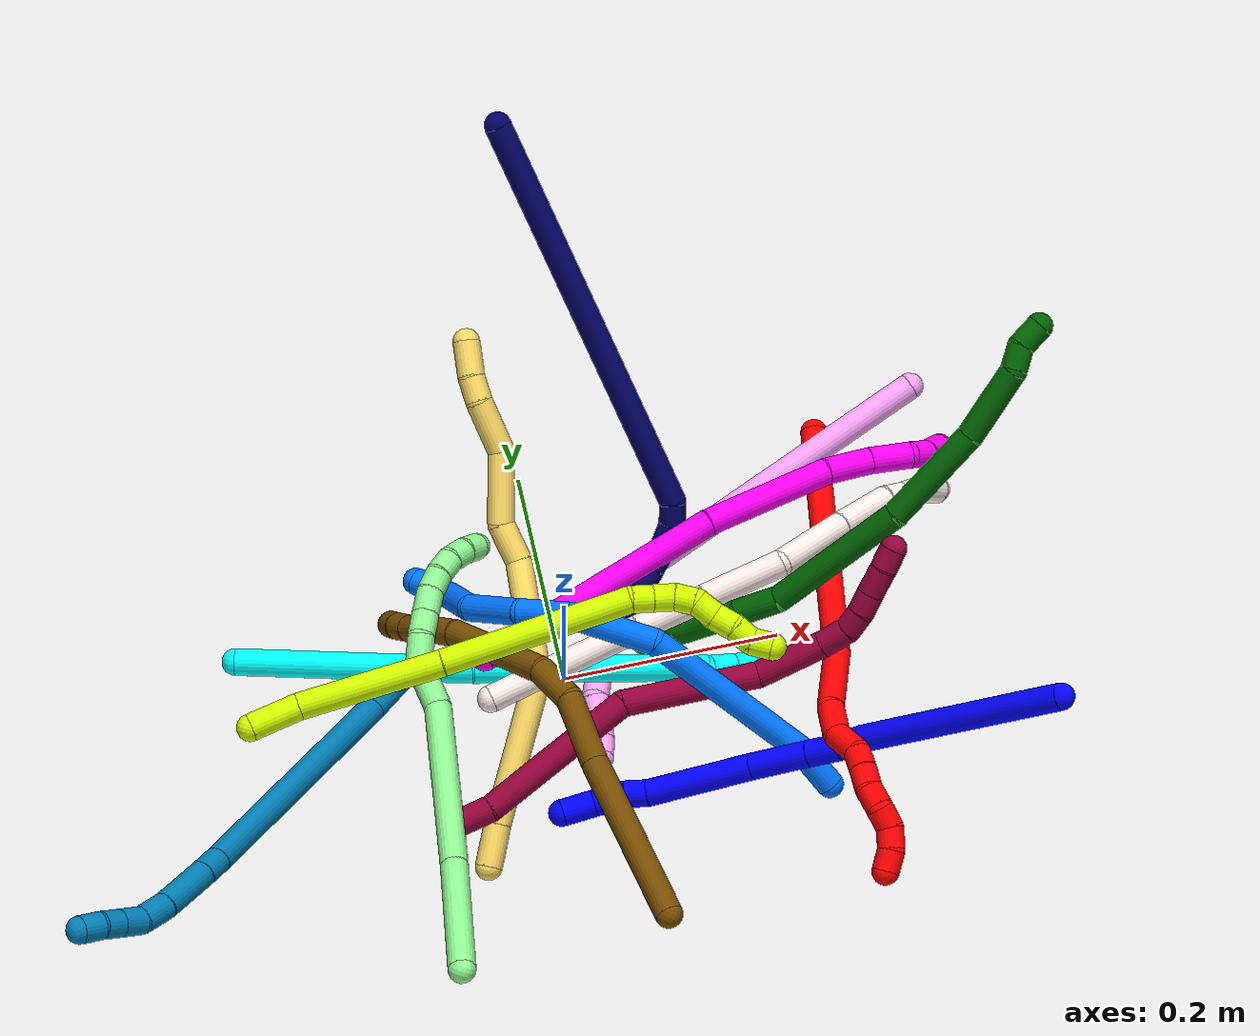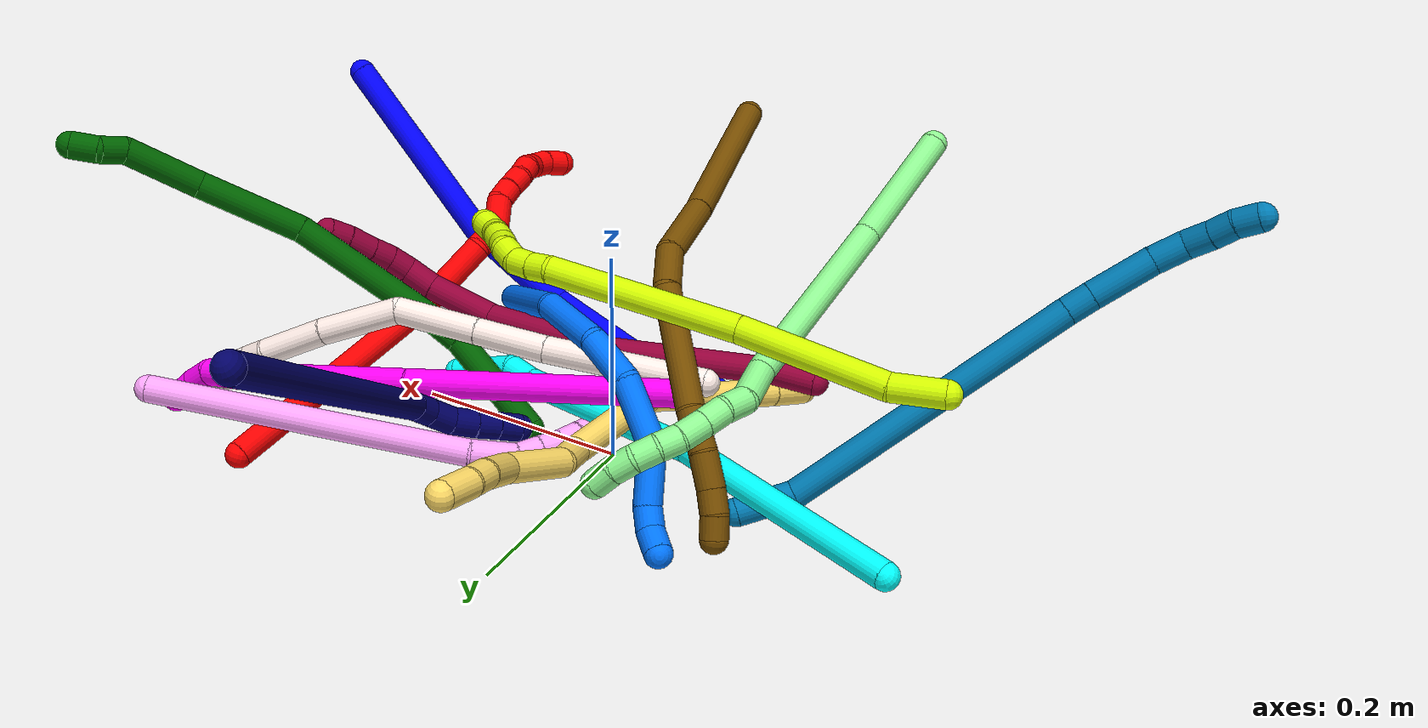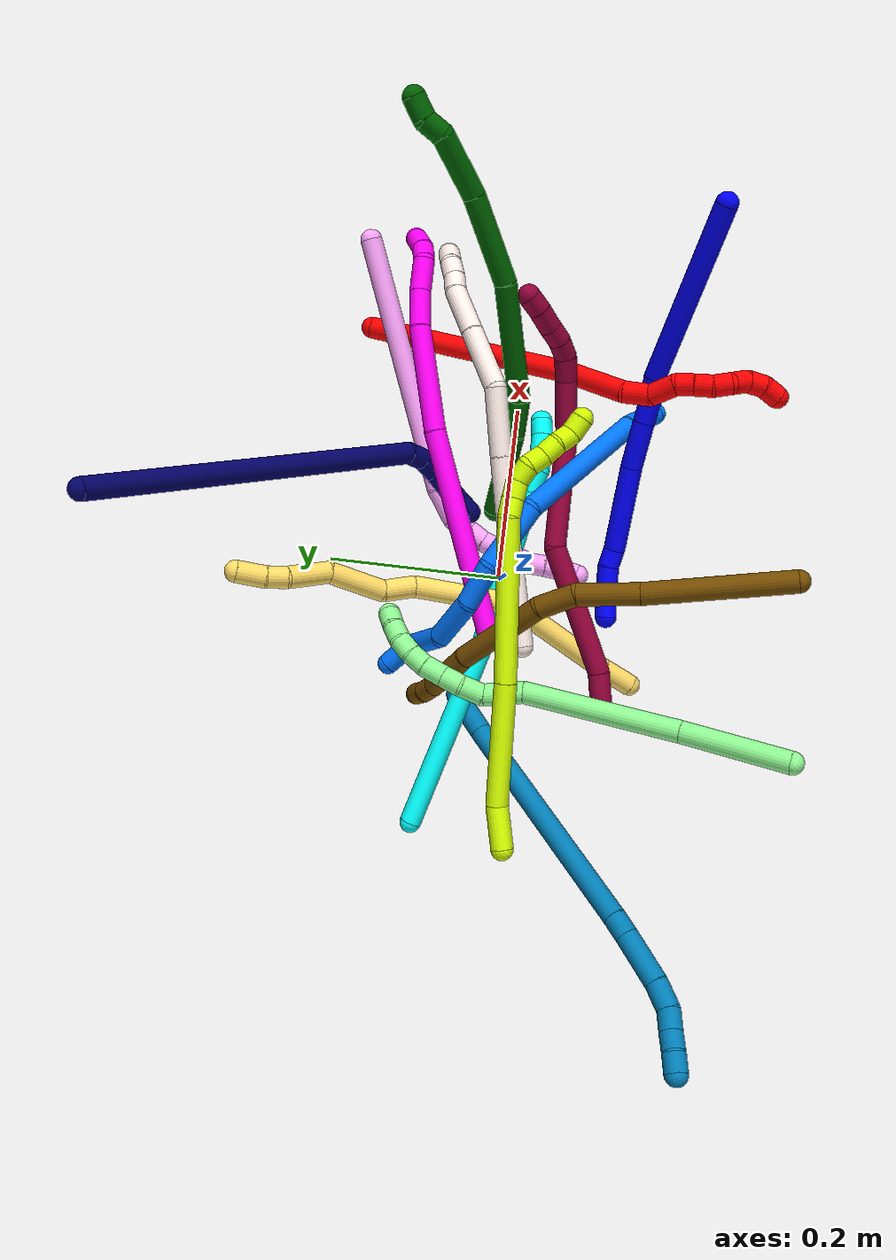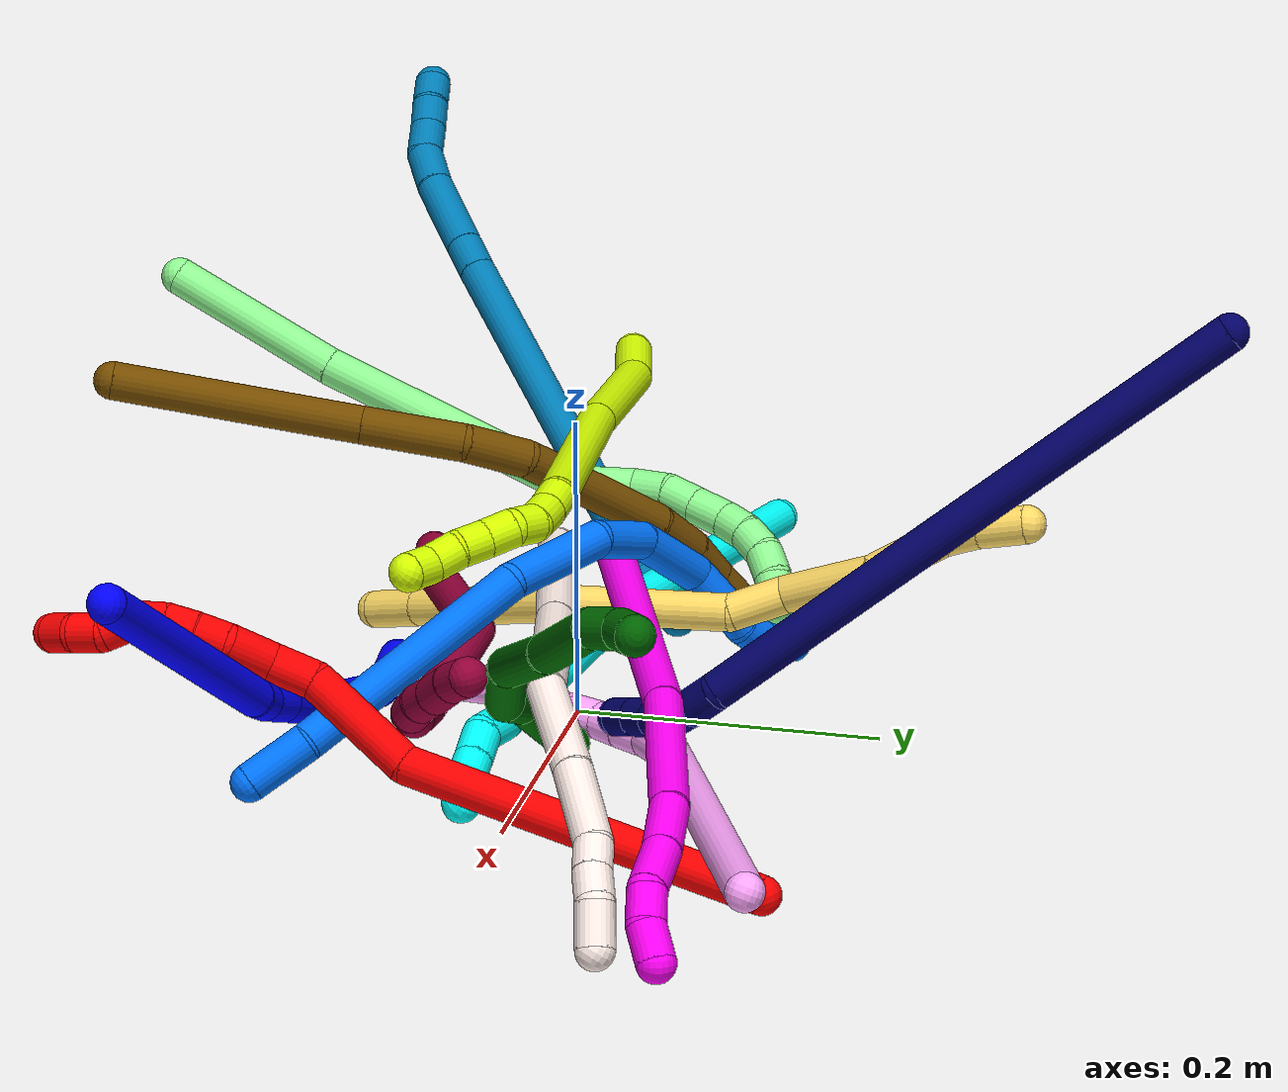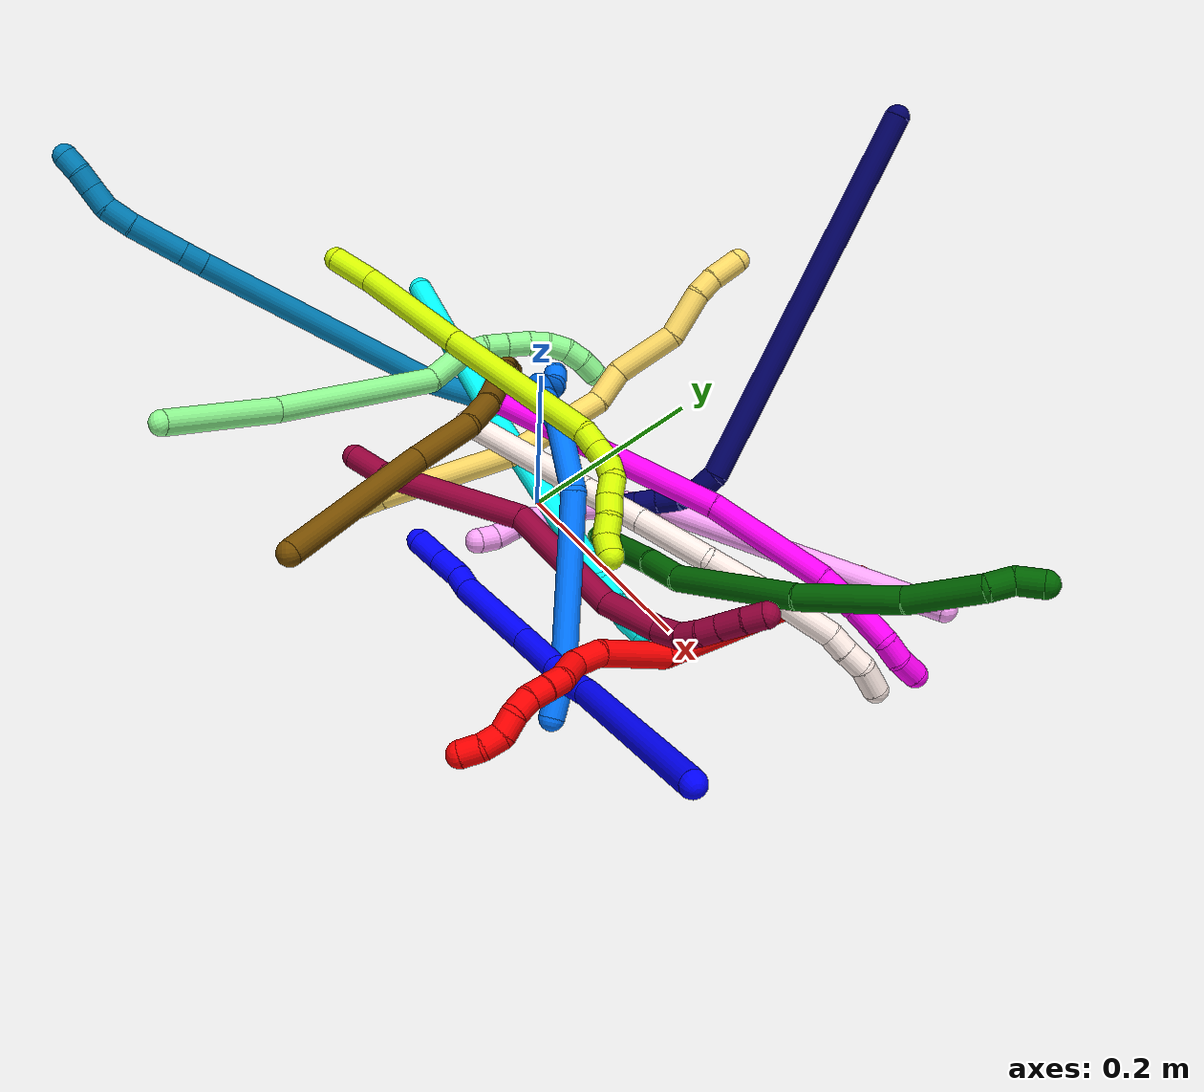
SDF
<sdf version="1.7">
 <world name="default">
  <plugin name="TubeGeneratorPlugin" filename="libtube_generator_plugin.so"/>
  <model name="photoneo_s_sensor">
   <static>1</static>
   <pose>0 0 2 1.57079 1.57079 3.14159</pose>
   <link name="link">
    <inertial><mass>0.1</mass></inertial>
    <sensor name="sensor" type="depth">
     <update_rate>30</update_rate>
     <camera>
      <horizontal_fov>1.22</horizontal_fov>
      <image><width>1920</width><height>1200</height><format>B8G8R8</format></image>
      <clip><near>0.1</near><far>4</far></clip>
      <depth_camera><output>points</output></depth_camera>
     </camera>
     <plugin name="camera_plugin" filename="libgazebo_ros_depth_camera.so">
      <baseline>0.2</baseline>
      <alwaysOn>1</alwaysOn>
      <updateRate>0.0</updateRate>
      <cameraName>camera_ir</cameraName>
      <imageTopicName>/camera/color/image_raw</imageTopicName>
      <cameraInfoTopicName>/camera/color/camera_info</cameraInfoTopicName>
      <depthImageTopicName>/camera/depth/image_raw</depthImageTopicName>
      <depthImageCameraInfoTopicName>/camera/depth/camera_info</depthImageCameraInfoTopicName>
      <pointCloudTopicName>/camera/depth/points</pointCloudTopicName>
      <frameName>fr_optical</frameName>
      <pointCloudCutoff>0.1</pointCloudCutoff>
      <pointCloudCutoffMax>2.0</pointCloudCutoffMax>
      <distortionK1>0</distortionK1>
      <distortionK2>0</distortionK2>
      <distortionK3>0</distortionK3>
      <distortionT1>0</distortionT1>
      <distortionT2>0</distortionT2>
      <CxPrime>0</CxPrime>
      <Cx>0</Cx>
      <Cy>0</Cy>
      <focalLength>0</focalLength>
      <hackBaseline>0</hackBaseline>
     </plugin>
    </sensor>
   </link>
  </model>
  <gravity>0 0 -9.8</gravity>
  <magnetic_field>6e-06 2.3e-05 -4.2e-05</magnetic_field>
  <atmosphere type="adiabatic"/>
  <physics name="default_physics" default="0" type="ode">
   <max_step_size>0.003</max_step_size>
   <real_time_factor>1</real_time_factor>
   <real_time_update_rate>1000</real_time_update_rate>
   <max_contacts>10000</max_contacts>
   <ode>
    <solver>
     <type>quick</type>
     <iters>100</iters>
     <sor>1.3</sor>
     <use_dynamic_moi_rescaling>0</use_dynamic_moi_rescaling>
    </solver>
    <constraints>
     <contact_max_correcting_vel>0</contact_max_correcting_vel>
     <contact_surface_layer>0.001</contact_surface_layer>
     <cfm>0</cfm>
     <erp>0.2</erp>
    </constraints>
   </ode>
  </physics>
  <scene><ambient>0.4 0.4 0.4 1</ambient><background>0.7 0.7 0.7 1</background><shadows>0</shadows></scene>
  <audio><device>default</device></audio>
  <spherical_coordinates>
   <surface_model>EARTH_WGS84</surface_model>
   <latitude_deg>0</latitude_deg>
   <longitude_deg>0</longitude_deg>
   <elevation>0</elevation>
   <heading_deg>0</heading_deg>
  </spherical_coordinates>
  <model name="bin">
   <static>1</static>
   <link name="bottom">
    <collision name="collision-bottom">
     <pose>0 0 -0.01 0 -0 0</pose>
     <geometry><box><size>0.8 0.6 0.02</size></box></geometry>
     <surface>
      <friction><ode><mu>100</mu><mu2>100</mu2></ode></friction>
      <contact><collide_bitmask>65535</collide_bitmask></contact>
     </surface>
    </collision>
   </link>
   <link name="west_wall">
    <collision name="collision-west_wall">
     <pose>-0.41 0 0.1 0 -0 0</pose>
     <geometry><box><size>0.02 0.6 0.2</size></box></geometry>
     <surface>
      <friction><ode><mu>100</mu><mu2>100</mu2></ode></friction>
      <contact><collide_bitmask>65535</collide_bitmask></contact>
     </surface>
    </collision>
   </link>
   <link name="east_wall">
    <collision name="collision-east_wall">
     <pose>0.41 0 0.1 0 -0 0</pose>
     <geometry><box><size>0.02 0.6 0.2</size></box></geometry>
     <surface>
      <friction><ode><mu>100</mu><mu2>100</mu2></ode></friction>
      <contact><collide_bitmask>65535</collide_bitmask></contact>
     </surface>
    </collision>
   </link>
   <link name="south_wall">
    <collision name="collision-south_wall">
     <pose>0 -0.31 0.1 0 -0 0</pose>
     <geometry><box><size>0.8 0.02 0.2</size></box></geometry>
     <surface>
      <friction><ode><mu>100</mu><mu2>100</mu2></ode></friction>
      <contact><collide_bitmask>65535</collide_bitmask></contact>
     </surface>
    </collision>
   </link>
   <link name="north_wall">
    <collision name="collision-north_wall">
     <pose>0 0.31 0.1 0 -0 0</pose>
     <geometry><box><size>0.8 0.02 0.2</size></box></geometry>
     <surface>
      <friction><ode><mu>100</mu><mu2>100</mu2></ode></friction>
      <contact><collide_bitmask>65535</collide_bitmask></contact>
     </surface>
    </collision>
   </link>
  </model>
  <model name="1">
   <static>0</static>
   <link name="1">
    <collision name="collision-cylinder-e_1_1_4">
     <pose>-0.004917 -0.024879 -0.101706 2.90169 -0.046922 -0.384557</pose>
     <geometry><cylinder><radius>0.0125</radius><length>0.20964</length></cylinder></geometry>
     <surface>
      <friction><ode><mu>1.16</mu><mu2>1.16</mu2><slip1>0</slip1><slip2>0</slip2></ode></friction>
      <contact><ode><kp>1e+06</kp><kd>1</kd><max_vel>0</max_vel><min_depth>0.001</min_depth></ode></contact>
     </surface>
    </collision>
    <visual name="visual-cylinder-e_1_1_4">
     <pose>-0.004917 -0.024879 -0.101706 2.90169 -0.046922 -0.384557</pose>
     <geometry><cylinder><radius>0.0125</radius><length>0.20964</length></cylinder></geometry>
     <material><ambient>0 0 1 1</ambient></material>
    </visual>
    <collision name="collision-cylinder-e_2_4_5">
     <pose>-0.013176 -0.051934 -0.214553 2.94869 -0.286384 -1.95954</pose>
     <geometry><cylinder><radius>0.0125</radius><length>0.023668</length></cylinder></geometry>
     <surface>
      <friction><ode><mu>1.16</mu><mu2>1.16</mu2><slip1>0</slip1><slip2>0</slip2></ode></friction>
      <contact><ode><kp>1e+06</kp><kd>1</kd><max_vel>0</max_vel><min_depth>0.001</min_depth></ode></contact>
     </surface>
    </collision>
    <visual name="visual-cylinder-e_2_4_5">
     <pose>-0.013176 -0.051934 -0.214553 2.94869 -0.286384 -1.95954</pose>
     <geometry><cylinder><radius>0.0125</radius><length>0.023668</length></cylinder></geometry>
     <material><ambient>0 0 1 1</ambient></material>
    </visual>
    <collision name="collision-cylinder-e_3_5_6">
     <pose>-0.019427 -0.054931 -0.240234 3.08516 -0.197114 -2.58547</pose>
     <geometry><cylinder><radius>0.0125</radius><length>0.029701</length></cylinder></geometry>
     <surface>
      <friction><ode><mu>1.16</mu><mu2>1.16</mu2><slip1>0</slip1><slip2>0</slip2></ode></friction>
      <contact><ode><kp>1e+06</kp><kd>1</kd><max_vel>0</max_vel><min_depth>0.001</min_depth></ode></contact>
     </surface>
    </collision>
    <visual name="visual-cylinder-e_3_5_6">
     <pose>-0.019427 -0.054931 -0.240234 3.08516 -0.197114 -2.58547</pose>
     <geometry><cylinder><radius>0.0125</radius><length>0.029701</length></cylinder></geometry>
     <material><ambient>0 0 1 1</ambient></material>
    </visual>
    <collision name="collision-cylinder-e_4_6_7">
     <pose>-0.028386 -0.057579 -0.281815 3.07416 -0.219644 -2.54793</pose>
     <geometry><cylinder><radius>0.0125</radius><length>0.05554</length></cylinder></geometry>
     <surface>
      <friction><ode><mu>1.16</mu><mu2>1.16</mu2><slip1>0</slip1><slip2>0</slip2></ode></friction>
      <contact><ode><kp>1e+06</kp><kd>1</kd><max_vel>0</max_vel><min_depth>0.001</min_depth></ode></contact>
     </surface>
    </collision>
    <visual name="visual-cylinder-e_4_6_7">
     <pose>-0.028386 -0.057579 -0.281815 3.07416 -0.219644 -2.54793</pose>
     <geometry><cylinder><radius>0.0125</radius><length>0.05554</length></cylinder></geometry>
     <material><ambient>0 0 1 1</ambient></material>
    </visual>
    <collision name="collision-cylinder-e_5_7_8">
     <pose>-0.049445 -0.059577 -0.356586 3.13799 -0.304652 -3.11815</pose>
     <geometry><cylinder><radius>0.0125</radius><length>0.10007</length></cylinder></geometry>
     <surface>
      <friction><ode><mu>1.16</mu><mu2>1.16</mu2><slip1>0</slip1><slip2>0</slip2></ode></friction>
      <contact><ode><kp>1e+06</kp><kd>1</kd><max_vel>0</max_vel><min_depth>0.001</min_depth></ode></contact>
     </surface>
    </collision>
    <visual name="visual-cylinder-e_5_7_8">
     <pose>-0.049445 -0.059577 -0.356586 3.13799 -0.304652 -3.11815</pose>
     <geometry><cylinder><radius>0.0125</radius><length>0.10007</length></cylinder></geometry>
     <material><ambient>0 0 1 1</ambient></material>
    </visual>
    <collision name="collision-cylinder-e_6_8_9">
     <pose>-0.066711 -0.057701 -0.41437 -2.94069 -0.216544 1.64625</pose>
     <geometry><cylinder><radius>0.0125</radius><length>0.021009</length></cylinder></geometry>
     <surface>
      <friction><ode><mu>1.16</mu><mu2>1.16</mu2><slip1>0</slip1><slip2>0</slip2></ode></friction>
      <contact><ode><kp>1e+06</kp><kd>1</kd><max_vel>0</max_vel><min_depth>0.001</min_depth></ode></contact>
     </surface>
    </collision>
    <visual name="visual-cylinder-e_6_8_9">
     <pose>-0.066711 -0.057701 -0.41437 -2.94069 -0.216544 1.64625</pose>
     <geometry><cylinder><radius>0.0125</radius><length>0.021009</length></cylinder></geometry>
     <material><ambient>0 0 1 1</ambient></material>
    </visual>
    <collision name="collision-cylinder-e_7_9_10">
     <pose>-0.075587 -0.053757 -0.43758 -2.99843 -0.462013 2.54977</pose>
     <geometry><cylinder><radius>0.0125</radius><length>0.029701</length></cylinder></geometry>
     <surface>
      <friction><ode><mu>1.16</mu><mu2>1.16</mu2><slip1>0</slip1><slip2>0</slip2></ode></friction>
      <contact><ode><kp>1e+06</kp><kd>1</kd><max_vel>0</max_vel><min_depth>0.001</min_depth></ode></contact>
     </surface>
    </collision>
    <visual name="visual-cylinder-e_7_9_10">
     <pose>-0.075587 -0.053757 -0.43758 -2.99843 -0.462013 2.54977</pose>
     <geometry><cylinder><radius>0.0125</radius><length>0.029701</length></cylinder></geometry>
     <material><ambient>0 0 1 1</ambient></material>
    </visual>
    <collision name="collision-cylinder-e_8_10_2">
     <pose>-0.090366 -0.048076 -0.46316 -2.84588 -0.560987 2.18727</pose>
     <geometry><cylinder><radius>0.0125</radius><length>0.030672</length></cylinder></geometry>
     <surface>
      <friction><ode><mu>1.16</mu><mu2>1.16</mu2><slip1>0</slip1><slip2>0</slip2></ode></friction>
      <contact><ode><kp>1e+06</kp><kd>1</kd><max_vel>0</max_vel><min_depth>0.001</min_depth></ode></contact>
     </surface>
    </collision>
    <visual name="visual-cylinder-e_8_10_2">
     <pose>-0.090366 -0.048076 -0.46316 -2.84588 -0.560987 2.18727</pose>
     <geometry><cylinder><radius>0.0125</radius><length>0.030672</length></cylinder></geometry>
     <material><ambient>0 0 1 1</ambient></material>
    </visual>
    <collision name="collision-sphere-2">
     <pose>-0.098525 -0.044292 -0.475582 0 -0 0</pose>
     <geometry><sphere><radius>0.0125</radius></sphere></geometry>
     <surface>
      <friction><ode><mu>1.16</mu><mu2>1.16</mu2><slip1>0</slip1><slip2>0</slip2></ode></friction>
      <contact><ode><kp>1e+06</kp><kd>1</kd><max_vel>0</max_vel><min_depth>0.001</min_depth></ode></contact>
     </surface>
    </collision>
    <visual name="visual-sphere-2">
     <pose>-0.098525 -0.044292 -0.475582 0 -0 0</pose>
     <geometry><sphere><radius>0.0125</radius></sphere></geometry>
     <material><ambient>0 0 1 1</ambient></material>
    </visual>
    <collision name="collision-sphere-10">
     <pose>-0.082207 -0.051861 -0.450738 0 -0 0</pose>
     <geometry><sphere><radius>0.0125</radius></sphere></geometry>
     <surface>
      <friction><ode><mu>1.16</mu><mu2>1.16</mu2><slip1>0</slip1><slip2>0</slip2></ode></friction>
      <contact><ode><kp>1e+06</kp><kd>1</kd><max_vel>0</max_vel><min_depth>0.001</min_depth></ode></contact>
     </surface>
    </collision>
    <visual name="visual-sphere-10">
     <pose>-0.082207 -0.051861 -0.450738 0 -0 0</pose>
     <geometry><sphere><radius>0.0125</radius></sphere></geometry>
     <material><ambient>0 0 1 1</ambient></material>
    </visual>
    <collision name="collision-sphere-9">
     <pose>-0.068968 -0.055654 -0.424423 0 -0 0</pose>
     <geometry><sphere><radius>0.0125</radius></sphere></geometry>
     <surface>
      <friction><ode><mu>1.16</mu><mu2>1.16</mu2><slip1>0</slip1><slip2>0</slip2></ode></friction>
      <contact><ode><kp>1e+06</kp><kd>1</kd><max_vel>0</max_vel><min_depth>0.001</min_depth></ode></contact>
     </surface>
    </collision>
    <visual name="visual-sphere-9">
     <pose>-0.068968 -0.055654 -0.424423 0 -0 0</pose>
     <geometry><sphere><radius>0.0125</radius></sphere></geometry>
     <material><ambient>0 0 1 1</ambient></material>
    </visual>
    <collision name="collision-sphere-4">
     <pose>-0.009833 -0.049758 -0.203412 0 -0 0</pose>
     <geometry><sphere><radius>0.0125</radius></sphere></geometry>
     <surface>
      <friction><ode><mu>1.16</mu><mu2>1.16</mu2><slip1>0</slip1><slip2>0</slip2></ode></friction>
      <contact><ode><kp>1e+06</kp><kd>1</kd><max_vel>0</max_vel><min_depth>0.001</min_depth></ode></contact>
     </surface>
    </collision>
    <visual name="visual-sphere-4">
     <pose>-0.009833 -0.049758 -0.203412 0 -0 0</pose>
     <geometry><sphere><radius>0.0125</radius></sphere></geometry>
     <material><ambient>0 0 1 1</ambient></material>
    </visual>
    <collision name="collision-sphere-1">
     <geometry><sphere><radius>0.0125</radius></sphere></geometry>
     <surface>
      <friction><ode><mu>1.16</mu><mu2>1.16</mu2><slip1>0</slip1><slip2>0</slip2></ode></friction>
      <contact><ode><kp>1e+06</kp><kd>1</kd><max_vel>0</max_vel><min_depth>0.001</min_depth></ode></contact>
     </surface>
    </collision>
    <visual name="visual-sphere-1">
     <geometry><sphere><radius>0.0125</radius></sphere></geometry>
     <material><ambient>0 0 1 1</ambient></material>
    </visual>
    <collision name="collision-sphere-8">
     <pose>-0.064454 -0.059749 -0.404317 0 -0 0</pose>
     <geometry><sphere><radius>0.0125</radius></sphere></geometry>
     <surface>
      <friction><ode><mu>1.16</mu><mu2>1.16</mu2><slip1>0</slip1><slip2>0</slip2></ode></friction>
      <contact><ode><kp>1e+06</kp><kd>1</kd><max_vel>0</max_vel><min_depth>0.001</min_depth></ode></contact>
     </surface>
    </collision>
    <visual name="visual-sphere-8">
     <pose>-0.064454 -0.059749 -0.404317 0 -0 0</pose>
     <geometry><sphere><radius>0.0125</radius></sphere></geometry>
     <material><ambient>0 0 1 1</ambient></material>
    </visual>
    <collision name="collision-sphere-5">
     <pose>-0.016519 -0.05411 -0.225694 0 -0 0</pose>
     <geometry><sphere><radius>0.0125</radius></sphere></geometry>
     <surface>
      <friction><ode><mu>1.16</mu><mu2>1.16</mu2><slip1>0</slip1><slip2>0</slip2></ode></friction>
      <contact><ode><kp>1e+06</kp><kd>1</kd><max_vel>0</max_vel><min_depth>0.001</min_depth></ode></contact>
     </surface>
    </collision>
    <visual name="visual-sphere-5">
     <pose>-0.016519 -0.05411 -0.225694 0 -0 0</pose>
     <geometry><sphere><radius>0.0125</radius></sphere></geometry>
     <material><ambient>0 0 1 1</ambient></material>
    </visual>
    <collision name="collision-sphere-6">
     <pose>-0.022336 -0.055753 -0.254774 0 -0 0</pose>
     <geometry><sphere><radius>0.0125</radius></sphere></geometry>
     <surface>
      <friction><ode><mu>1.16</mu><mu2>1.16</mu2><slip1>0</slip1><slip2>0</slip2></ode></friction>
      <contact><ode><kp>1e+06</kp><kd>1</kd><max_vel>0</max_vel><min_depth>0.001</min_depth></ode></contact>
     </surface>
    </collision>
    <visual name="visual-sphere-6">
     <pose>-0.022336 -0.055753 -0.254774 0 -0 0</pose>
     <geometry><sphere><radius>0.0125</radius></sphere></geometry>
     <material><ambient>0 0 1 1</ambient></material>
    </visual>
    <collision name="collision-sphere-7">
     <pose>-0.034437 -0.059405 -0.308856 0 -0 0</pose>
     <geometry><sphere><radius>0.0125</radius></sphere></geometry>
     <surface>
      <friction><ode><mu>1.16</mu><mu2>1.16</mu2><slip1>0</slip1><slip2>0</slip2></ode></friction>
      <contact><ode><kp>1e+06</kp><kd>1</kd><max_vel>0</max_vel><min_depth>0.001</min_depth></ode></contact>
     </surface>
    </collision>
    <visual name="visual-sphere-7">
     <pose>-0.034437 -0.059405 -0.308856 0 -0 0</pose>
     <geometry><sphere><radius>0.0125</radius></sphere></geometry>
     <material><ambient>0 0 1 1</ambient></material>
    </visual>
    <inertial>
     <pose>-0.029725 -0.043039 -0.241557 0 -0 0</pose>
     <mass>0.5</mass>
     <inertia>
      <ixx>0.000307</ixx>
      <ixy>0</ixy>
      <ixz>0</ixz>
      <iyy>-0.000888</iyy>
      <iyz>0</iyz>
      <izz>0.000219</izz>
     </inertia>
    </inertial>
   </link>
   <pose>0.406671 -0.183846 0.219406 1.13694 0.256713 1.08536</pose>
  </model>
  <model name="2">
   <static>0</static>
   <link name="2">
    <collision name="collision-cylinder-e_1_1_4">
     <pose>0.037295 -0.091287 -0.067918 2.21045 0.316739 0.615567</pose>
     <geometry><cylinder><radius>0.0125</radius><length>0.239475</length></cylinder></geometry>
     <surface>
      <friction><ode><mu>1.16</mu><mu2>1.16</mu2><slip1>0</slip1><slip2>0</slip2></ode></friction>
      <contact><ode><kp>1e+06</kp><kd>1</kd><max_vel>0</max_vel><min_depth>0.001</min_depth></ode></contact>
     </surface>
    </collision>
    <visual name="visual-cylinder-e_1_1_4">
     <pose>0.037295 -0.091287 -0.067918 2.21045 0.316739 0.615567</pose>
     <geometry><cylinder><radius>0.0125</radius><length>0.239475</length></cylinder></geometry>
     <material><ambient>1 0 0 1</ambient></material>
    </visual>
    <collision name="collision-cylinder-e_2_4_5">
     <pose>0.087387 -0.200744 -0.167629 2.62237 0.336209 1.13713</pose>
     <geometry><cylinder><radius>0.0125</radius><length>0.077581</length></cylinder></geometry>
     <surface>
      <friction><ode><mu>1.16</mu><mu2>1.16</mu2><slip1>0</slip1><slip2>0</slip2></ode></friction>
      <contact><ode><kp>1e+06</kp><kd>1</kd><max_vel>0</max_vel><min_depth>0.001</min_depth></ode></contact>
     </surface>
    </collision>
    <visual name="visual-cylinder-e_2_4_5">
     <pose>0.087387 -0.200744 -0.167629 2.62237 0.336209 1.13713</pose>
     <geometry><cylinder><radius>0.0125</radius><length>0.077581</length></cylinder></geometry>
     <material><ambient>1 0 0 1</ambient></material>
    </visual>
    <collision name="collision-cylinder-e_3_5_6">
     <pose>0.103304 -0.230261 -0.209207 2.28241 0.205283 0.442317</pose>
     <geometry><cylinder><radius>0.0125</radius><length>0.030608</length></cylinder></geometry>
     <surface>
      <friction><ode><mu>1.16</mu><mu2>1.16</mu2><slip1>0</slip1><slip2>0</slip2></ode></friction>
      <contact><ode><kp>1e+06</kp><kd>1</kd><max_vel>0</max_vel><min_depth>0.001</min_depth></ode></contact>
     </surface>
    </collision>
    <visual name="visual-cylinder-e_3_5_6">
     <pose>0.103304 -0.230261 -0.209207 2.28241 0.205283 0.442317</pose>
     <geometry><cylinder><radius>0.0125</radius><length>0.030608</length></cylinder></geometry>
     <material><ambient>1 0 0 1</ambient></material>
    </visual>
    <collision name="collision-cylinder-e_4_6_7">
     <pose>0.101648 -0.251955 -0.229848 2.38018 -0.308231 -0.740491</pose>
     <geometry><cylinder><radius>0.0125</radius><length>0.031479</length></cylinder></geometry>
     <surface>
      <friction><ode><mu>1.16</mu><mu2>1.16</mu2><slip1>0</slip1><slip2>0</slip2></ode></friction>
      <contact><ode><kp>1e+06</kp><kd>1</kd><max_vel>0</max_vel><min_depth>0.001</min_depth></ode></contact>
     </surface>
    </collision>
    <visual name="visual-cylinder-e_4_6_7">
     <pose>0.101648 -0.251955 -0.229848 2.38018 -0.308231 -0.740491</pose>
     <geometry><cylinder><radius>0.0125</radius><length>0.031479</length></cylinder></geometry>
     <material><ambient>1 0 0 1</ambient></material>
    </visual>
    <collision name="collision-cylinder-e_5_7_8">
     <pose>0.097932 -0.270136 -0.246971 2.24555 0.105153 0.218121</pose>
     <geometry><cylinder><radius>0.0125</radius><length>0.020176</length></cylinder></geometry>
     <surface>
      <friction><ode><mu>1.16</mu><mu2>1.16</mu2><slip1>0</slip1><slip2>0</slip2></ode></friction>
      <contact><ode><kp>1e+06</kp><kd>1</kd><max_vel>0</max_vel><min_depth>0.001</min_depth></ode></contact>
     </surface>
    </collision>
    <visual name="visual-cylinder-e_5_7_8">
     <pose>0.097932 -0.270136 -0.246971 2.24555 0.105153 0.218121</pose>
     <geometry><cylinder><radius>0.0125</radius><length>0.020176</length></cylinder></geometry>
     <material><ambient>1 0 0 1</ambient></material>
    </visual>
    <collision name="collision-cylinder-e_6_8_9">
     <pose>0.100683 -0.286177 -0.258938 2.17784 0.16772 0.318717</pose>
     <geometry><cylinder><radius>0.0125</radius><length>0.020269</length></cylinder></geometry>
     <surface>
      <friction><ode><mu>1.16</mu><mu2>1.16</mu2><slip1>0</slip1><slip2>0</slip2></ode></friction>
      <contact><ode><kp>1e+06</kp><kd>1</kd><max_vel>0</max_vel><min_depth>0.001</min_depth></ode></contact>
     </surface>
    </collision>
    <visual name="visual-cylinder-e_6_8_9">
     <pose>0.100683 -0.286177 -0.258938 2.17784 0.16772 0.318717</pose>
     <geometry><cylinder><radius>0.0125</radius><length>0.020269</length></cylinder></geometry>
     <material><ambient>1 0 0 1</ambient></material>
    </visual>
    <collision name="collision-cylinder-e_7_9_10">
     <pose>0.102095 -0.303619 -0.268661 1.98166 -0.027733 -0.042329</pose>
     <geometry><cylinder><radius>0.0125</radius><length>0.020155</length></cylinder></geometry>
     <surface>
      <friction><ode><mu>1.16</mu><mu2>1.16</mu2><slip1>0</slip1><slip2>0</slip2></ode></friction>
      <contact><ode><kp>1e+06</kp><kd>1</kd><max_vel>0</max_vel><min_depth>0.001</min_depth></ode></contact>
     </surface>
    </collision>
    <visual name="visual-cylinder-e_7_9_10">
     <pose>0.102095 -0.303619 -0.268661 1.98166 -0.027733 -0.042329</pose>
     <geometry><cylinder><radius>0.0125</radius><length>0.020155</length></cylinder></geometry>
     <material><ambient>1 0 0 1</ambient></material>
    </visual>
    <collision name="collision-cylinder-e_8_10_11">
     <pose>0.102023 -0.322948 -0.272143 1.51713 0.020455 0.019386</pose>
     <geometry><cylinder><radius>0.0125</radius><length>0.020221</length></cylinder></geometry>
     <surface>
      <friction><ode><mu>1.16</mu><mu2>1.16</mu2><slip1>0</slip1><slip2>0</slip2></ode></friction>
      <contact><ode><kp>1e+06</kp><kd>1</kd><max_vel>0</max_vel><min_depth>0.001</min_depth></ode></contact>
     </surface>
    </collision>
    <visual name="visual-cylinder-e_8_10_11">
     <pose>0.102023 -0.322948 -0.272143 1.51713 0.020455 0.019386</pose>
     <geometry><cylinder><radius>0.0125</radius><length>0.020221</length></cylinder></geometry>
     <material><ambient>1 0 0 1</ambient></material>
    </visual>
    <collision name="collision-cylinder-e_9_11_12">
     <pose>0.106302 -0.34187 -0.273997 1.83585 0.418807 0.542114</pose>
     <geometry><cylinder><radius>0.0125</radius><length>0.020026</length></cylinder></geometry>
     <surface>
      <friction><ode><mu>1.16</mu><mu2>1.16</mu2><slip1>0</slip1><slip2>0</slip2></ode></friction>
      <contact><ode><kp>1e+06</kp><kd>1</kd><max_vel>0</max_vel><min_depth>0.001</min_depth></ode></contact>
     </surface>
    </collision>
    <visual name="visual-cylinder-e_9_11_12">
     <pose>0.106302 -0.34187 -0.273997 1.83585 0.418807 0.542114</pose>
     <geometry><cylinder><radius>0.0125</radius><length>0.020026</length></cylinder></geometry>
     <material><ambient>1 0 0 1</ambient></material>
    </visual>
    <collision name="collision-cylinder-e_10_12_2">
     <pose>0.117249 -0.357853 -0.277673 1.74775 0.757574 0.8877</pose>
     <geometry><cylinder><radius>0.0125</radius><length>0.020011</length></cylinder></geometry>
     <surface>
      <friction><ode><mu>1.16</mu><mu2>1.16</mu2><slip1>0</slip1><slip2>0</slip2></ode></friction>
      <contact><ode><kp>1e+06</kp><kd>1</kd><max_vel>0</max_vel><min_depth>0.001</min_depth></ode></contact>
     </surface>
    </collision>
    <visual name="visual-cylinder-e_10_12_2">
     <pose>0.117249 -0.357853 -0.277673 1.74775 0.757574 0.8877</pose>
     <geometry><cylinder><radius>0.0125</radius><length>0.020011</length></cylinder></geometry>
     <material><ambient>1 0 0 1</ambient></material>
    </visual>
    <collision name="collision-sphere-2">
     <pose>0.124124 -0.365009 -0.278952 0 -0 0</pose>
     <geometry><sphere><radius>0.0125</radius></sphere></geometry>
     <surface>
      <friction><ode><mu>1.16</mu><mu2>1.16</mu2><slip1>0</slip1><slip2>0</slip2></ode></friction>
      <contact><ode><kp>1e+06</kp><kd>1</kd><max_vel>0</max_vel><min_depth>0.001</min_depth></ode></contact>
     </surface>
    </collision>
    <visual name="visual-sphere-2">
     <pose>0.124124 -0.365009 -0.278952 0 -0 0</pose>
     <geometry><sphere><radius>0.0125</radius></sphere></geometry>
     <material><ambient>1 0 0 1</ambient></material>
    </visual>
    <collision name="collision-sphere-12">
     <pose>0.110374 -0.350698 -0.276393 0 -0 0</pose>
     <geometry><sphere><radius>0.0125</radius></sphere></geometry>
     <surface>
      <friction><ode><mu>1.16</mu><mu2>1.16</mu2><slip1>0</slip1><slip2>0</slip2></ode></friction>
      <contact><ode><kp>1e+06</kp><kd>1</kd><max_vel>0</max_vel><min_depth>0.001</min_depth></ode></contact>
     </surface>
    </collision>
    <visual name="visual-sphere-12">
     <pose>0.110374 -0.350698 -0.276393 0 -0 0</pose>
     <geometry><sphere><radius>0.0125</radius></sphere></geometry>
     <material><ambient>1 0 0 1</ambient></material>
    </visual>
    <collision name="collision-sphere-11">
     <pose>0.102229 -0.333041 -0.2716 0 -0 0</pose>
     <geometry><sphere><radius>0.0125</radius></sphere></geometry>
     <surface>
      <friction><ode><mu>1.16</mu><mu2>1.16</mu2><slip1>0</slip1><slip2>0</slip2></ode></friction>
      <contact><ode><kp>1e+06</kp><kd>1</kd><max_vel>0</max_vel><min_depth>0.001</min_depth></ode></contact>
     </surface>
    </collision>
    <visual name="visual-sphere-11">
     <pose>0.102229 -0.333041 -0.2716 0 -0 0</pose>
     <geometry><sphere><radius>0.0125</radius></sphere></geometry>
     <material><ambient>1 0 0 1</ambient></material>
    </visual>
    <collision name="collision-sphere-10">
     <pose>0.101816 -0.312854 -0.272685 0 -0 0</pose>
     <geometry><sphere><radius>0.0125</radius></sphere></geometry>
     <surface>
      <friction><ode><mu>1.16</mu><mu2>1.16</mu2><slip1>0</slip1><slip2>0</slip2></ode></friction>
      <contact><ode><kp>1e+06</kp><kd>1</kd><max_vel>0</max_vel><min_depth>0.001</min_depth></ode></contact>
     </surface>
    </collision>
    <visual name="visual-sphere-10">
     <pose>0.101816 -0.312854 -0.272685 0 -0 0</pose>
     <geometry><sphere><radius>0.0125</radius></sphere></geometry>
     <material><ambient>1 0 0 1</ambient></material>
    </visual>
    <collision name="collision-sphere-9">
     <pose>0.102375 -0.294384 -0.264638 0 -0 0</pose>
     <geometry><sphere><radius>0.0125</radius></sphere></geometry>
     <surface>
      <friction><ode><mu>1.16</mu><mu2>1.16</mu2><slip1>0</slip1><slip2>0</slip2></ode></friction>
      <contact><ode><kp>1e+06</kp><kd>1</kd><max_vel>0</max_vel><min_depth>0.001</min_depth></ode></contact>
     </surface>
    </collision>
    <visual name="visual-sphere-9">
     <pose>0.102375 -0.294384 -0.264638 0 -0 0</pose>
     <geometry><sphere><radius>0.0125</radius></sphere></geometry>
     <material><ambient>1 0 0 1</ambient></material>
    </visual>
    <collision name="collision-sphere-4">
     <pose>0.074589 -0.182574 -0.135837 0 -0 0</pose>
     <geometry><sphere><radius>0.0125</radius></sphere></geometry>
     <surface>
      <friction><ode><mu>1.16</mu><mu2>1.16</mu2><slip1>0</slip1><slip2>0</slip2></ode></friction>
      <contact><ode><kp>1e+06</kp><kd>1</kd><max_vel>0</max_vel><min_depth>0.001</min_depth></ode></contact>
     </surface>
    </collision>
    <visual name="visual-sphere-4">
     <pose>0.074589 -0.182574 -0.135837 0 -0 0</pose>
     <geometry><sphere><radius>0.0125</radius></sphere></geometry>
     <material><ambient>1 0 0 1</ambient></material>
    </visual>
    <collision name="collision-sphere-1">
     <geometry><sphere><radius>0.0125</radius></sphere></geometry>
     <surface>
      <friction><ode><mu>1.16</mu><mu2>1.16</mu2><slip1>0</slip1><slip2>0</slip2></ode></friction>
      <contact><ode><kp>1e+06</kp><kd>1</kd><max_vel>0</max_vel><min_depth>0.001</min_depth></ode></contact>
     </surface>
    </collision>
    <visual name="visual-sphere-1">
     <geometry><sphere><radius>0.0125</radius></sphere></geometry>
     <material><ambient>1 0 0 1</ambient></material>
    </visual>
    <collision name="collision-sphere-8">
     <pose>0.098991 -0.27797 -0.253238 0 -0 0</pose>
     <geometry><sphere><radius>0.0125</radius></sphere></geometry>
     <surface>
      <friction><ode><mu>1.16</mu><mu2>1.16</mu2><slip1>0</slip1><slip2>0</slip2></ode></friction>
      <contact><ode><kp>1e+06</kp><kd>1</kd><max_vel>0</max_vel><min_depth>0.001</min_depth></ode></contact>
     </surface>
    </collision>
    <visual name="visual-sphere-8">
     <pose>0.098991 -0.27797 -0.253238 0 -0 0</pose>
     <geometry><sphere><radius>0.0125</radius></sphere></geometry>
     <material><ambient>1 0 0 1</ambient></material>
    </visual>
    <collision name="collision-sphere-5">
     <pose>0.100184 -0.218914 -0.199422 0 -0 0</pose>
     <geometry><sphere><radius>0.0125</radius></sphere></geometry>
     <surface>
      <friction><ode><mu>1.16</mu><mu2>1.16</mu2><slip1>0</slip1><slip2>0</slip2></ode></friction>
      <contact><ode><kp>1e+06</kp><kd>1</kd><max_vel>0</max_vel><min_depth>0.001</min_depth></ode></contact>
     </surface>
    </collision>
    <visual name="visual-sphere-5">
     <pose>0.100184 -0.218914 -0.199422 0 -0 0</pose>
     <geometry><sphere><radius>0.0125</radius></sphere></geometry>
     <material><ambient>1 0 0 1</ambient></material>
    </visual>
    <collision name="collision-sphere-6">
     <pose>0.106423 -0.241608 -0.218991 0 -0 0</pose>
     <geometry><sphere><radius>0.0125</radius></sphere></geometry>
     <surface>
      <friction><ode><mu>1.16</mu><mu2>1.16</mu2><slip1>0</slip1><slip2>0</slip2></ode></friction>
      <contact><ode><kp>1e+06</kp><kd>1</kd><max_vel>0</max_vel><min_depth>0.001</min_depth></ode></contact>
     </surface>
    </collision>
    <visual name="visual-sphere-6">
     <pose>0.106423 -0.241608 -0.218991 0 -0 0</pose>
     <geometry><sphere><radius>0.0125</radius></sphere></geometry>
     <material><ambient>1 0 0 1</ambient></material>
    </visual>
    <collision name="collision-sphere-7">
     <pose>0.096874 -0.262303 -0.240704 0 -0 0</pose>
     <geometry><sphere><radius>0.0125</radius></sphere></geometry>
     <surface>
      <friction><ode><mu>1.16</mu><mu2>1.16</mu2><slip1>0</slip1><slip2>0</slip2></ode></friction>
      <contact><ode><kp>1e+06</kp><kd>1</kd><max_vel>0</max_vel><min_depth>0.001</min_depth></ode></contact>
     </surface>
    </collision>
    <visual name="visual-sphere-7">
     <pose>0.096874 -0.262303 -0.240704 0 -0 0</pose>
     <geometry><sphere><radius>0.0125</radius></sphere></geometry>
     <material><ambient>1 0 0 1</ambient></material>
    </visual>
    <inertial>
     <pose>0.069369 -0.180643 -0.150202 0 -0 0</pose>
     <mass>0.5</mass>
     <inertia>
      <ixx>0.001605</ixx>
      <ixy>0</ixy>
      <ixz>0</ixz>
      <iyy>0.000232</iyy>
      <iyz>0</iyz>
      <izz>0.000515</izz>
     </inertia>
    </inertial>
   </link>
   <pose>0.277744 0.182442 0.012229 2.80392 0.239903 -2.9048</pose>
  </model>
  <model name="3">
   <static>0</static>
   <link name="3">
    <collision name="collision-cylinder-e_1_1_4">
     <pose>0.091592 -0.060018 -0.003148 1.62319 0.990094 1.03455</pose>
     <geometry><cylinder><radius>0.0125</radius><length>0.2191</length></cylinder></geometry>
     <surface>
      <friction><ode><mu>1.16</mu><mu2>1.16</mu2><slip1>0</slip1><slip2>0</slip2></ode></friction>
      <contact><ode><kp>1e+06</kp><kd>1</kd><max_vel>0</max_vel><min_depth>0.001</min_depth></ode></contact>
     </surface>
    </collision>
    <visual name="visual-cylinder-e_1_1_4">
     <pose>0.091592 -0.060018 -0.003148 1.62319 0.990094 1.03455</pose>
     <geometry><cylinder><radius>0.0125</radius><length>0.2191</length></cylinder></geometry>
     <material><ambient>0.003922 1 0.996078 1</ambient></material>
    </visual>
    <collision name="collision-cylinder-e_2_4_5">
     <pose>0.267713 -0.160877 -0.01191 1.70742 1.11703 1.24365</pose>
     <geometry><cylinder><radius>0.0125</radius><length>0.188093</length></cylinder></geometry>
     <surface>
      <friction><ode><mu>1.16</mu><mu2>1.16</mu2><slip1>0</slip1><slip2>0</slip2></ode></friction>
      <contact><ode><kp>1e+06</kp><kd>1</kd><max_vel>0</max_vel><min_depth>0.001</min_depth></ode></contact>
     </surface>
    </collision>
    <visual name="visual-cylinder-e_2_4_5">
     <pose>0.267713 -0.160877 -0.01191 1.70742 1.11703 1.24365</pose>
     <geometry><cylinder><radius>0.0125</radius><length>0.188093</length></cylinder></geometry>
     <material><ambient>0.003922 1 0.996078 1</ambient></material>
    </visual>
    <collision name="collision-cylinder-e_3_5_6">
     <pose>0.363901 -0.20943 -0.017891 1.61817 0.985947 1.02597</pose>
     <geometry><cylinder><radius>0.0125</radius><length>0.027965</length></cylinder></geometry>
     <surface>
      <friction><ode><mu>1.16</mu><mu2>1.16</mu2><slip1>0</slip1><slip2>0</slip2></ode></friction>
      <contact><ode><kp>1e+06</kp><kd>1</kd><max_vel>0</max_vel><min_depth>0.001</min_depth></ode></contact>
     </surface>
    </collision>
    <visual name="visual-cylinder-e_3_5_6">
     <pose>0.363901 -0.20943 -0.017891 1.61817 0.985947 1.02597</pose>
     <geometry><cylinder><radius>0.0125</radius><length>0.027965</length></cylinder></geometry>
     <material><ambient>0.003922 1 0.996078 1</ambient></material>
    </visual>
    <collision name="collision-cylinder-e_4_6_7">
     <pose>0.387197 -0.218376 -0.020675 2.66909 1.34152 2.55244</pose>
     <geometry><cylinder><radius>0.0125</radius><length>0.0239</length></cylinder></geometry>
     <surface>
      <friction><ode><mu>1.16</mu><mu2>1.16</mu2><slip1>0</slip1><slip2>0</slip2></ode></friction>
      <contact><ode><kp>1e+06</kp><kd>1</kd><max_vel>0</max_vel><min_depth>0.001</min_depth></ode></contact>
     </surface>
    </collision>
    <visual name="visual-cylinder-e_4_6_7">
     <pose>0.387197 -0.218376 -0.020675 2.66909 1.34152 2.55244</pose>
     <geometry><cylinder><radius>0.0125</radius><length>0.0239</length></cylinder></geometry>
     <material><ambient>0.003922 1 0.996078 1</ambient></material>
    </visual>
    <collision name="collision-cylinder-e_5_7_8">
     <pose>0.408754 -0.220826 -0.025103 2.59847 1.33844 2.46466</pose>
     <geometry><cylinder><radius>0.0125</radius><length>0.020387</length></cylinder></geometry>
     <surface>
      <friction><ode><mu>1.16</mu><mu2>1.16</mu2><slip1>0</slip1><slip2>0</slip2></ode></friction>
      <contact><ode><kp>1e+06</kp><kd>1</kd><max_vel>0</max_vel><min_depth>0.001</min_depth></ode></contact>
     </surface>
    </collision>
    <visual name="visual-cylinder-e_5_7_8">
     <pose>0.408754 -0.220826 -0.025103 2.59847 1.33844 2.46466</pose>
     <geometry><cylinder><radius>0.0125</radius><length>0.020387</length></cylinder></geometry>
     <material><ambient>0.003922 1 0.996078 1</ambient></material>
    </visual>
    <collision name="collision-cylinder-e_6_8_2">
     <pose>0.428928 -0.222554 -0.027564 2.29065 1.50408 2.23935</pose>
     <geometry><cylinder><radius>0.0125</radius><length>0.020556</length></cylinder></geometry>
     <surface>
      <friction><ode><mu>1.16</mu><mu2>1.16</mu2><slip1>0</slip1><slip2>0</slip2></ode></friction>
      <contact><ode><kp>1e+06</kp><kd>1</kd><max_vel>0</max_vel><min_depth>0.001</min_depth></ode></contact>
     </surface>
    </collision>
    <visual name="visual-cylinder-e_6_8_2">
     <pose>0.428928 -0.222554 -0.027564 2.29065 1.50408 2.23935</pose>
     <geometry><cylinder><radius>0.0125</radius><length>0.020556</length></cylinder></geometry>
     <material><ambient>0.003922 1 0.996078 1</ambient></material>
    </visual>
    <collision name="collision-sphere-2">
     <pose>0.439183 -0.223069 -0.028015 0 -0 0</pose>
     <geometry><sphere><radius>0.0125</radius></sphere></geometry>
     <surface>
      <friction><ode><mu>1.16</mu><mu2>1.16</mu2><slip1>0</slip1><slip2>0</slip2></ode></friction>
      <contact><ode><kp>1e+06</kp><kd>1</kd><max_vel>0</max_vel><min_depth>0.001</min_depth></ode></contact>
     </surface>
    </collision>
    <visual name="visual-sphere-2">
     <pose>0.439183 -0.223069 -0.028015 0 -0 0</pose>
     <geometry><sphere><radius>0.0125</radius></sphere></geometry>
     <material><ambient>0.003922 1 0.996078 1</ambient></material>
    </visual>
    <collision name="collision-sphere-4">
     <pose>0.183184 -0.120036 -0.006295 0 -0 0</pose>
     <geometry><sphere><radius>0.0125</radius></sphere></geometry>
     <surface>
      <friction><ode><mu>1.16</mu><mu2>1.16</mu2><slip1>0</slip1><slip2>0</slip2></ode></friction>
      <contact><ode><kp>1e+06</kp><kd>1</kd><max_vel>0</max_vel><min_depth>0.001</min_depth></ode></contact>
     </surface>
    </collision>
    <visual name="visual-sphere-4">
     <pose>0.183184 -0.120036 -0.006295 0 -0 0</pose>
     <geometry><sphere><radius>0.0125</radius></sphere></geometry>
     <material><ambient>0.003922 1 0.996078 1</ambient></material>
    </visual>
    <collision name="collision-sphere-1">
     <geometry><sphere><radius>0.0125</radius></sphere></geometry>
     <surface>
      <friction><ode><mu>1.16</mu><mu2>1.16</mu2><slip1>0</slip1><slip2>0</slip2></ode></friction>
      <contact><ode><kp>1e+06</kp><kd>1</kd><max_vel>0</max_vel><min_depth>0.001</min_depth></ode></contact>
     </surface>
    </collision>
    <visual name="visual-sphere-1">
     <geometry><sphere><radius>0.0125</radius></sphere></geometry>
     <material><ambient>0.003922 1 0.996078 1</ambient></material>
    </visual>
    <collision name="collision-sphere-8">
     <pose>0.418673 -0.222039 -0.027112 0 -0 0</pose>
     <geometry><sphere><radius>0.0125</radius></sphere></geometry>
     <surface>
      <friction><ode><mu>1.16</mu><mu2>1.16</mu2><slip1>0</slip1><slip2>0</slip2></ode></friction>
      <contact><ode><kp>1e+06</kp><kd>1</kd><max_vel>0</max_vel><min_depth>0.001</min_depth></ode></contact>
     </surface>
    </collision>
    <visual name="visual-sphere-8">
     <pose>0.418673 -0.222039 -0.027112 0 -0 0</pose>
     <geometry><sphere><radius>0.0125</radius></sphere></geometry>
     <material><ambient>0.003922 1 0.996078 1</ambient></material>
    </visual>
    <collision name="collision-sphere-5">
     <pose>0.352242 -0.201719 -0.017525 0 -0 0</pose>
     <geometry><sphere><radius>0.0125</radius></sphere></geometry>
     <surface>
      <friction><ode><mu>1.16</mu><mu2>1.16</mu2><slip1>0</slip1><slip2>0</slip2></ode></friction>
      <contact><ode><kp>1e+06</kp><kd>1</kd><max_vel>0</max_vel><min_depth>0.001</min_depth></ode></contact>
     </surface>
    </collision>
    <visual name="visual-sphere-5">
     <pose>0.352242 -0.201719 -0.017525 0 -0 0</pose>
     <geometry><sphere><radius>0.0125</radius></sphere></geometry>
     <material><ambient>0.003922 1 0.996078 1</ambient></material>
    </visual>
    <collision name="collision-sphere-6">
     <pose>0.375559 -0.21714 -0.018256 0 -0 0</pose>
     <geometry><sphere><radius>0.0125</radius></sphere></geometry>
     <surface>
      <friction><ode><mu>1.16</mu><mu2>1.16</mu2><slip1>0</slip1><slip2>0</slip2></ode></friction>
      <contact><ode><kp>1e+06</kp><kd>1</kd><max_vel>0</max_vel><min_depth>0.001</min_depth></ode></contact>
     </surface>
    </collision>
    <visual name="visual-sphere-6">
     <pose>0.375559 -0.21714 -0.018256 0 -0 0</pose>
     <geometry><sphere><radius>0.0125</radius></sphere></geometry>
     <material><ambient>0.003922 1 0.996078 1</ambient></material>
    </visual>
    <collision name="collision-sphere-7">
     <pose>0.398834 -0.219613 -0.023093 0 -0 0</pose>
     <geometry><sphere><radius>0.0125</radius></sphere></geometry>
     <surface>
      <friction><ode><mu>1.16</mu><mu2>1.16</mu2><slip1>0</slip1><slip2>0</slip2></ode></friction>
      <contact><ode><kp>1e+06</kp><kd>1</kd><max_vel>0</max_vel><min_depth>0.001</min_depth></ode></contact>
     </surface>
    </collision>
    <visual name="visual-sphere-7">
     <pose>0.398834 -0.219613 -0.023093 0 -0 0</pose>
     <geometry><sphere><radius>0.0125</radius></sphere></geometry>
     <material><ambient>0.003922 1 0.996078 1</ambient></material>
    </visual>
    <inertial>
     <pose>0.214007 -0.127125 -0.010005 0 -0 0</pose>
     <mass>0.5</mass>
     <inertia>
      <ixx>0.001014</ixx>
      <ixy>0</ixy>
      <ixz>0</ixz>
      <iyy>0.001703</iyy>
      <iyz>0</iyz>
      <izz>-0.000524</izz>
     </inertia>
    </inertial>
   </link>
   <pose>-0.293127 0.071516 0.02944 -0.616869 0.272685 0.209619</pose>
  </model>
  <model name="4">
   <static>0</static>
   <link name="4">
    <collision name="collision-cylinder-e_1_1_4">
     <pose>-0.129075 0.06884 -0.020297 -1.85751 -1.06333 1.33304</pose>
     <geometry><cylinder><radius>0.0125</radius><length>0.295374</length></cylinder></geometry>
     <surface>
      <friction><ode><mu>1.16</mu><mu2>1.16</mu2><slip1>0</slip1><slip2>0</slip2></ode></friction>
      <contact><ode><kp>1e+06</kp><kd>1</kd><max_vel>0</max_vel><min_depth>0.001</min_depth></ode></contact>
     </surface>
    </collision>
    <visual name="visual-cylinder-e_1_1_4">
     <pose>-0.129075 0.06884 -0.020297 -1.85751 -1.06333 1.33304</pose>
     <geometry><cylinder><radius>0.0125</radius><length>0.295374</length></cylinder></geometry>
     <material><ambient>1 0.65098 0.996078 1</ambient></material>
    </visual>
    <collision name="collision-cylinder-e_2_4_5">
     <pose>-0.274368 0.150797 -0.041113 -1.61037 -0.890331 0.921483</pose>
     <geometry><cylinder><radius>0.0125</radius><length>0.041729</length></cylinder></geometry>
     <surface>
      <friction><ode><mu>1.16</mu><mu2>1.16</mu2><slip1>0</slip1><slip2>0</slip2></ode></friction>
      <contact><ode><kp>1e+06</kp><kd>1</kd><max_vel>0</max_vel><min_depth>0.001</min_depth></ode></contact>
     </surface>
    </collision>
    <visual name="visual-cylinder-e_2_4_5">
     <pose>-0.274368 0.150797 -0.041113 -1.61037 -0.890331 0.921483</pose>
     <geometry><cylinder><radius>0.0125</radius><length>0.041729</length></cylinder></geometry>
     <material><ambient>1 0.65098 0.996078 1</ambient></material>
    </visual>
    <collision name="collision-cylinder-e_3_5_6">
     <pose>-0.294985 0.174392 -0.040984 -1.50897 -0.39686 0.373619</pose>
     <geometry><cylinder><radius>0.0125</radius><length>0.022765</length></cylinder></geometry>
     <surface>
      <friction><ode><mu>1.16</mu><mu2>1.16</mu2><slip1>0</slip1><slip2>0</slip2></ode></friction>
      <contact><ode><kp>1e+06</kp><kd>1</kd><max_vel>0</max_vel><min_depth>0.001</min_depth></ode></contact>
     </surface>
    </collision>
    <visual name="visual-cylinder-e_3_5_6">
     <pose>-0.294985 0.174392 -0.040984 -1.50897 -0.39686 0.373619</pose>
     <geometry><cylinder><radius>0.0125</radius><length>0.022765</length></cylinder></geometry>
     <material><ambient>1 0.65098 0.996078 1</ambient></material>
    </visual>
    <collision name="collision-cylinder-e_4_6_7">
     <pose>-0.30368 0.193911 -0.039992 -1.53287 -0.443264 0.427269</pose>
     <geometry><cylinder><radius>0.0125</radius><length>0.020031</length></cylinder></geometry>
     <surface>
      <friction><ode><mu>1.16</mu><mu2>1.16</mu2><slip1>0</slip1><slip2>0</slip2></ode></friction>
      <contact><ode><kp>1e+06</kp><kd>1</kd><max_vel>0</max_vel><min_depth>0.001</min_depth></ode></contact>
     </surface>
    </collision>
    <visual name="visual-cylinder-e_4_6_7">
     <pose>-0.30368 0.193911 -0.039992 -1.53287 -0.443264 0.427269</pose>
     <geometry><cylinder><radius>0.0125</radius><length>0.020031</length></cylinder></geometry>
     <material><ambient>1 0.65098 0.996078 1</ambient></material>
    </visual>
    <collision name="collision-cylinder-e_5_7_8">
     <pose>-0.310631 0.212553 -0.038498 -1.45151 -0.267983 0.238085</pose>
     <geometry><cylinder><radius>0.0125</radius><length>0.020056</length></cylinder></geometry>
     <surface>
      <friction><ode><mu>1.16</mu><mu2>1.16</mu2><slip1>0</slip1><slip2>0</slip2></ode></friction>
      <contact><ode><kp>1e+06</kp><kd>1</kd><max_vel>0</max_vel><min_depth>0.001</min_depth></ode></contact>
     </surface>
    </collision>
    <visual name="visual-cylinder-e_5_7_8">
     <pose>-0.310631 0.212553 -0.038498 -1.45151 -0.267983 0.238085</pose>
     <geometry><cylinder><radius>0.0125</radius><length>0.020056</length></cylinder></geometry>
     <material><ambient>1 0.65098 0.996078 1</ambient></material>
    </visual>
    <collision name="collision-cylinder-e_6_8_9">
     <pose>-0.315752 0.231683 -0.035499 -1.3792 -0.248712 0.205441</pose>
     <geometry><cylinder><radius>0.0125</radius><length>0.020028</length></cylinder></geometry>
     <surface>
      <friction><ode><mu>1.16</mu><mu2>1.16</mu2><slip1>0</slip1><slip2>0</slip2></ode></friction>
      <contact><ode><kp>1e+06</kp><kd>1</kd><max_vel>0</max_vel><min_depth>0.001</min_depth></ode></contact>
     </surface>
    </collision>
    <visual name="visual-cylinder-e_6_8_9">
     <pose>-0.315752 0.231683 -0.035499 -1.3792 -0.248712 0.205441</pose>
     <geometry><cylinder><radius>0.0125</radius><length>0.020028</length></cylinder></geometry>
     <material><ambient>1 0.65098 0.996078 1</ambient></material>
    </visual>
    <collision name="collision-cylinder-e_7_9_10">
     <pose>-0.319207 0.250979 -0.035576 -1.76543 -0.099132 0.120534</pose>
     <geometry><cylinder><radius>0.0125</radius><length>0.020009</length></cylinder></geometry>
     <surface>
      <friction><ode><mu>1.16</mu><mu2>1.16</mu2><slip1>0</slip1><slip2>0</slip2></ode></friction>
      <contact><ode><kp>1e+06</kp><kd>1</kd><max_vel>0</max_vel><min_depth>0.001</min_depth></ode></contact>
     </surface>
    </collision>
    <visual name="visual-cylinder-e_7_9_10">
     <pose>-0.319207 0.250979 -0.035576 -1.76543 -0.099132 0.120534</pose>
     <geometry><cylinder><radius>0.0125</radius><length>0.020009</length></cylinder></geometry>
     <material><ambient>1 0.65098 0.996078 1</ambient></material>
    </visual>
    <collision name="collision-cylinder-e_8_10_11">
     <pose>-0.320035 0.270534 -0.035446 -1.36376 0.016202 -0.013152</pose>
     <geometry><cylinder><radius>0.0125</radius><length>0.020005</length></cylinder></geometry>
     <surface>
      <friction><ode><mu>1.16</mu><mu2>1.16</mu2><slip1>0</slip1><slip2>0</slip2></ode></friction>
      <contact><ode><kp>1e+06</kp><kd>1</kd><max_vel>0</max_vel><min_depth>0.001</min_depth></ode></contact>
     </surface>
    </collision>
    <visual name="visual-cylinder-e_8_10_11">
     <pose>-0.320035 0.270534 -0.035446 -1.36376 0.016202 -0.013152</pose>
     <geometry><cylinder><radius>0.0125</radius><length>0.020005</length></cylinder></geometry>
     <material><ambient>1 0.65098 0.996078 1</ambient></material>
    </visual>
    <collision name="collision-cylinder-e_9_11_12">
     <pose>-0.320479 0.289984 -0.030884 -1.31704 -0.060605 0.046898</pose>
     <geometry><cylinder><radius>0.0125</radius><length>0.020001</length></cylinder></geometry>
     <surface>
      <friction><ode><mu>1.16</mu><mu2>1.16</mu2><slip1>0</slip1><slip2>0</slip2></ode></friction>
      <contact><ode><kp>1e+06</kp><kd>1</kd><max_vel>0</max_vel><min_depth>0.001</min_depth></ode></contact>
     </surface>
    </collision>
    <visual name="visual-cylinder-e_9_11_12">
     <pose>-0.320479 0.289984 -0.030884 -1.31704 -0.060605 0.046898</pose>
     <geometry><cylinder><radius>0.0125</radius><length>0.020001</length></cylinder></geometry>
     <material><ambient>1 0.65098 0.996078 1</ambient></material>
    </visual>
    <collision name="collision-cylinder-e_10_12_2">
     <pose>-0.321601 0.30962 -0.028914 -1.62447 -0.051654 0.054502</pose>
     <geometry><cylinder><radius>0.0125</radius><length>0.020002</length></cylinder></geometry>
     <surface>
      <friction><ode><mu>1.16</mu><mu2>1.16</mu2><slip1>0</slip1><slip2>0</slip2></ode></friction>
      <contact><ode><kp>1e+06</kp><kd>1</kd><max_vel>0</max_vel><min_depth>0.001</min_depth></ode></contact>
     </surface>
    </collision>
    <visual name="visual-cylinder-e_10_12_2">
     <pose>-0.321601 0.30962 -0.028914 -1.62447 -0.051654 0.054502</pose>
     <geometry><cylinder><radius>0.0125</radius><length>0.020002</length></cylinder></geometry>
     <material><ambient>1 0.65098 0.996078 1</ambient></material>
    </visual>
    <collision name="collision-sphere-2">
     <pose>-0.322117 0.319593 -0.02945 0 -0 0</pose>
     <geometry><sphere><radius>0.0125</radius></sphere></geometry>
     <surface>
      <friction><ode><mu>1.16</mu><mu2>1.16</mu2><slip1>0</slip1><slip2>0</slip2></ode></friction>
      <contact><ode><kp>1e+06</kp><kd>1</kd><max_vel>0</max_vel><min_depth>0.001</min_depth></ode></contact>
     </surface>
    </collision>
    <visual name="visual-sphere-2">
     <pose>-0.322117 0.319593 -0.02945 0 -0 0</pose>
     <geometry><sphere><radius>0.0125</radius></sphere></geometry>
     <material><ambient>1 0.65098 0.996078 1</ambient></material>
    </visual>
    <collision name="collision-sphere-12">
     <pose>-0.321084 0.299646 -0.028379 0 -0 0</pose>
     <geometry><sphere><radius>0.0125</radius></sphere></geometry>
     <surface>
      <friction><ode><mu>1.16</mu><mu2>1.16</mu2><slip1>0</slip1><slip2>0</slip2></ode></friction>
      <contact><ode><kp>1e+06</kp><kd>1</kd><max_vel>0</max_vel><min_depth>0.001</min_depth></ode></contact>
     </surface>
    </collision>
    <visual name="visual-sphere-12">
     <pose>-0.321084 0.299646 -0.028379 0 -0 0</pose>
     <geometry><sphere><radius>0.0125</radius></sphere></geometry>
     <material><ambient>1 0.65098 0.996078 1</ambient></material>
    </visual>
    <collision name="collision-sphere-11">
     <pose>-0.319873 0.280322 -0.03339 0 -0 0</pose>
     <geometry><sphere><radius>0.0125</radius></sphere></geometry>
     <surface>
      <friction><ode><mu>1.16</mu><mu2>1.16</mu2><slip1>0</slip1><slip2>0</slip2></ode></friction>
      <contact><ode><kp>1e+06</kp><kd>1</kd><max_vel>0</max_vel><min_depth>0.001</min_depth></ode></contact>
     </surface>
    </collision>
    <visual name="visual-sphere-11">
     <pose>-0.319873 0.280322 -0.03339 0 -0 0</pose>
     <geometry><sphere><radius>0.0125</radius></sphere></geometry>
     <material><ambient>1 0.65098 0.996078 1</ambient></material>
    </visual>
    <collision name="collision-sphere-10">
     <pose>-0.320197 0.260747 -0.037502 0 -0 0</pose>
     <geometry><sphere><radius>0.0125</radius></sphere></geometry>
     <surface>
      <friction><ode><mu>1.16</mu><mu2>1.16</mu2><slip1>0</slip1><slip2>0</slip2></ode></friction>
      <contact><ode><kp>1e+06</kp><kd>1</kd><max_vel>0</max_vel><min_depth>0.001</min_depth></ode></contact>
     </surface>
    </collision>
    <visual name="visual-sphere-10">
     <pose>-0.320197 0.260747 -0.037502 0 -0 0</pose>
     <geometry><sphere><radius>0.0125</radius></sphere></geometry>
     <material><ambient>1 0.65098 0.996078 1</ambient></material>
    </visual>
    <collision name="collision-sphere-9">
     <pose>-0.318217 0.241211 -0.033651 0 -0 0</pose>
     <geometry><sphere><radius>0.0125</radius></sphere></geometry>
     <surface>
      <friction><ode><mu>1.16</mu><mu2>1.16</mu2><slip1>0</slip1><slip2>0</slip2></ode></friction>
      <contact><ode><kp>1e+06</kp><kd>1</kd><max_vel>0</max_vel><min_depth>0.001</min_depth></ode></contact>
     </surface>
    </collision>
    <visual name="visual-sphere-9">
     <pose>-0.318217 0.241211 -0.033651 0 -0 0</pose>
     <geometry><sphere><radius>0.0125</radius></sphere></geometry>
     <material><ambient>1 0.65098 0.996078 1</ambient></material>
    </visual>
    <collision name="collision-sphere-4">
     <pose>-0.258151 0.137681 -0.040594 0 -0 0</pose>
     <geometry><sphere><radius>0.0125</radius></sphere></geometry>
     <surface>
      <friction><ode><mu>1.16</mu><mu2>1.16</mu2><slip1>0</slip1><slip2>0</slip2></ode></friction>
      <contact><ode><kp>1e+06</kp><kd>1</kd><max_vel>0</max_vel><min_depth>0.001</min_depth></ode></contact>
     </surface>
    </collision>
    <visual name="visual-sphere-4">
     <pose>-0.258151 0.137681 -0.040594 0 -0 0</pose>
     <geometry><sphere><radius>0.0125</radius></sphere></geometry>
     <material><ambient>1 0.65098 0.996078 1</ambient></material>
    </visual>
    <collision name="collision-sphere-1">
     <geometry><sphere><radius>0.0125</radius></sphere></geometry>
     <surface>
      <friction><ode><mu>1.16</mu><mu2>1.16</mu2><slip1>0</slip1><slip2>0</slip2></ode></friction>
      <contact><ode><kp>1e+06</kp><kd>1</kd><max_vel>0</max_vel><min_depth>0.001</min_depth></ode></contact>
     </surface>
    </collision>
    <visual name="visual-sphere-1">
     <geometry><sphere><radius>0.0125</radius></sphere></geometry>
     <material><ambient>1 0.65098 0.996078 1</ambient></material>
    </visual>
    <collision name="collision-sphere-8">
     <pose>-0.313287 0.222155 -0.037348 0 -0 0</pose>
     <geometry><sphere><radius>0.0125</radius></sphere></geometry>
     <surface>
      <friction><ode><mu>1.16</mu><mu2>1.16</mu2><slip1>0</slip1><slip2>0</slip2></ode></friction>
      <contact><ode><kp>1e+06</kp><kd>1</kd><max_vel>0</max_vel><min_depth>0.001</min_depth></ode></contact>
     </surface>
    </collision>
    <visual name="visual-sphere-8">
     <pose>-0.313287 0.222155 -0.037348 0 -0 0</pose>
     <geometry><sphere><radius>0.0125</radius></sphere></geometry>
     <material><ambient>1 0.65098 0.996078 1</ambient></material>
    </visual>
    <collision name="collision-sphere-5">
     <pose>-0.290585 0.163914 -0.041633 0 -0 0</pose>
     <geometry><sphere><radius>0.0125</radius></sphere></geometry>
     <surface>
      <friction><ode><mu>1.16</mu><mu2>1.16</mu2><slip1>0</slip1><slip2>0</slip2></ode></friction>
      <contact><ode><kp>1e+06</kp><kd>1</kd><max_vel>0</max_vel><min_depth>0.001</min_depth></ode></contact>
     </surface>
    </collision>
    <visual name="visual-sphere-5">
     <pose>-0.290585 0.163914 -0.041633 0 -0 0</pose>
     <geometry><sphere><radius>0.0125</radius></sphere></geometry>
     <material><ambient>1 0.65098 0.996078 1</ambient></material>
    </visual>
    <collision name="collision-sphere-6">
     <pose>-0.299385 0.18487 -0.040335 0 -0 0</pose>
     <geometry><sphere><radius>0.0125</radius></sphere></geometry>
     <surface>
      <friction><ode><mu>1.16</mu><mu2>1.16</mu2><slip1>0</slip1><slip2>0</slip2></ode></friction>
      <contact><ode><kp>1e+06</kp><kd>1</kd><max_vel>0</max_vel><min_depth>0.001</min_depth></ode></contact>
     </surface>
    </collision>
    <visual name="visual-sphere-6">
     <pose>-0.299385 0.18487 -0.040335 0 -0 0</pose>
     <geometry><sphere><radius>0.0125</radius></sphere></geometry>
     <material><ambient>1 0.65098 0.996078 1</ambient></material>
    </visual>
    <collision name="collision-sphere-7">
     <pose>-0.307976 0.202952 -0.039649 0 -0 0</pose>
     <geometry><sphere><radius>0.0125</radius></sphere></geometry>
     <surface>
      <friction><ode><mu>1.16</mu><mu2>1.16</mu2><slip1>0</slip1><slip2>0</slip2></ode></friction>
      <contact><ode><kp>1e+06</kp><kd>1</kd><max_vel>0</max_vel><min_depth>0.001</min_depth></ode></contact>
     </surface>
    </collision>
    <visual name="visual-sphere-7">
     <pose>-0.307976 0.202952 -0.039649 0 -0 0</pose>
     <geometry><sphere><radius>0.0125</radius></sphere></geometry>
     <material><ambient>1 0.65098 0.996078 1</ambient></material>
    </visual>
    <inertial>
     <pose>-0.201118 0.131621 -0.02709 0 -0 0</pose>
     <mass>0.5</mass>
     <inertia>
      <ixx>0.001262</ixx>
      <ixy>0</ixy>
      <ixz>0</ixz>
      <iyy>0.002672</iyy>
      <iyz>0</iyz>
      <izz>0.00087</izz>
     </inertia>
    </inertial>
   </link>
   <pose>0.369347 0.191584 0.056865 2.87686 -0.425776 -0.05677</pose>
  </model>
  <model name="5">
   <static>0</static>
   <link name="5">
    <collision name="collision-cylinder-e_1_1_4">
     <pose>0.008206 0.017123 0.00592 -1.2379 0.425278 -0.305196</pose>
     <geometry><cylinder><radius>0.0125</radius><length>0.039779</length></cylinder></geometry>
     <surface>
      <friction><ode><mu>1.16</mu><mu2>1.16</mu2><slip1>0</slip1><slip2>0</slip2></ode></friction>
      <contact><ode><kp>1e+06</kp><kd>1</kd><max_vel>0</max_vel><min_depth>0.001</min_depth></ode></contact>
     </surface>
    </collision>
    <visual name="visual-cylinder-e_1_1_4">
     <pose>0.008206 0.017123 0.00592 -1.2379 0.425278 -0.305196</pose>
     <geometry><cylinder><radius>0.0125</radius><length>0.039779</length></cylinder></geometry>
     <material><ambient>1 0.858824 0.4 1</ambient></material>
    </visual>
    <collision name="collision-cylinder-e_2_4_5">
     <pose>0.048808 0.091566 0.031817 -1.23545 0.490249 -0.351789</pose>
     <geometry><cylinder><radius>0.0125</radius><length>0.137611</length></cylinder></geometry>
     <surface>
      <friction><ode><mu>1.16</mu><mu2>1.16</mu2><slip1>0</slip1><slip2>0</slip2></ode></friction>
      <contact><ode><kp>1e+06</kp><kd>1</kd><max_vel>0</max_vel><min_depth>0.001</min_depth></ode></contact>
     </surface>
    </collision>
    <visual name="visual-cylinder-e_2_4_5">
     <pose>0.048808 0.091566 0.031817 -1.23545 0.490249 -0.351789</pose>
     <geometry><cylinder><radius>0.0125</radius><length>0.137611</length></cylinder></geometry>
     <material><ambient>1 0.858824 0.4 1</ambient></material>
    </visual>
    <collision name="collision-cylinder-e_3_5_6">
     <pose>0.08397 0.203935 0.059121 -1.43846 0.049747 -0.043566</pose>
     <geometry><cylinder><radius>0.0125</radius><length>0.111206</length></cylinder></geometry>
     <surface>
      <friction><ode><mu>1.16</mu><mu2>1.16</mu2><slip1>0</slip1><slip2>0</slip2></ode></friction>
      <contact><ode><kp>1e+06</kp><kd>1</kd><max_vel>0</max_vel><min_depth>0.001</min_depth></ode></contact>
     </surface>
    </collision>
    <visual name="visual-cylinder-e_3_5_6">
     <pose>0.08397 0.203935 0.059121 -1.43846 0.049747 -0.043566</pose>
     <geometry><cylinder><radius>0.0125</radius><length>0.111206</length></cylinder></geometry>
     <material><ambient>1 0.858824 0.4 1</ambient></material>
    </visual>
    <collision name="collision-cylinder-e_4_6_7">
     <pose>0.082564 0.275597 0.07439 -1.12493 -0.222772 0.140783</pose>
     <geometry><cylinder><radius>0.0125</radius><length>0.03776</length></cylinder></geometry>
     <surface>
      <friction><ode><mu>1.16</mu><mu2>1.16</mu2><slip1>0</slip1><slip2>0</slip2></ode></friction>
      <contact><ode><kp>1e+06</kp><kd>1</kd><max_vel>0</max_vel><min_depth>0.001</min_depth></ode></contact>
     </surface>
    </collision>
    <visual name="visual-cylinder-e_4_6_7">
     <pose>0.082564 0.275597 0.07439 -1.12493 -0.222772 0.140783</pose>
     <geometry><cylinder><radius>0.0125</radius><length>0.03776</length></cylinder></geometry>
     <material><ambient>1 0.858824 0.4 1</ambient></material>
    </visual>
    <collision name="collision-cylinder-e_5_7_8">
     <pose>0.086116 0.321503 0.096524 -1.11959 0.23296 -0.146389</pose>
     <geometry><cylinder><radius>0.0125</radius><length>0.066908</length></cylinder></geometry>
     <surface>
      <friction><ode><mu>1.16</mu><mu2>1.16</mu2><slip1>0</slip1><slip2>0</slip2></ode></friction>
      <contact><ode><kp>1e+06</kp><kd>1</kd><max_vel>0</max_vel><min_depth>0.001</min_depth></ode></contact>
     </surface>
    </collision>
    <visual name="visual-cylinder-e_5_7_8">
     <pose>0.086116 0.321503 0.096524 -1.11959 0.23296 -0.146389</pose>
     <geometry><cylinder><radius>0.0125</radius><length>0.066908</length></cylinder></geometry>
     <material><ambient>1 0.858824 0.4 1</ambient></material>
    </visual>
    <collision name="collision-cylinder-e_6_8_9">
     <pose>0.089291 0.370951 0.124979 -0.955018 -0.182175 0.094458</pose>
     <geometry><cylinder><radius>0.0125</radius><length>0.050211</length></cylinder></geometry>
     <surface>
      <friction><ode><mu>1.16</mu><mu2>1.16</mu2><slip1>0</slip1><slip2>0</slip2></ode></friction>
      <contact><ode><kp>1e+06</kp><kd>1</kd><max_vel>0</max_vel><min_depth>0.001</min_depth></ode></contact>
     </surface>
    </collision>
    <visual name="visual-cylinder-e_6_8_9">
     <pose>0.089291 0.370951 0.124979 -0.955018 -0.182175 0.094458</pose>
     <geometry><cylinder><radius>0.0125</radius><length>0.050211</length></cylinder></geometry>
     <material><ambient>1 0.858824 0.4 1</ambient></material>
    </visual>
    <collision name="collision-cylinder-e_7_9_10">
     <pose>0.083806 0.401878 0.143663 -1.18114 -0.080214 0.05379</pose>
     <geometry><cylinder><radius>0.0125</radius><length>0.023364</length></cylinder></geometry>
     <surface>
      <friction><ode><mu>1.16</mu><mu2>1.16</mu2><slip1>0</slip1><slip2>0</slip2></ode></friction>
      <contact><ode><kp>1e+06</kp><kd>1</kd><max_vel>0</max_vel><min_depth>0.001</min_depth></ode></contact>
     </surface>
    </collision>
    <visual name="visual-cylinder-e_7_9_10">
     <pose>0.083806 0.401878 0.143663 -1.18114 -0.080214 0.05379</pose>
     <geometry><cylinder><radius>0.0125</radius><length>0.023364</length></cylinder></geometry>
     <material><ambient>1 0.858824 0.4 1</ambient></material>
    </visual>
    <collision name="collision-cylinder-e_8_10_2">
     <pose>0.084178 0.42849 0.152806 -1.28123 0.078972 -0.058887</pose>
     <geometry><cylinder><radius>0.0125</radius><length>0.03316</length></cylinder></geometry>
     <surface>
      <friction><ode><mu>1.16</mu><mu2>1.16</mu2><slip1>0</slip1><slip2>0</slip2></ode></friction>
      <contact><ode><kp>1e+06</kp><kd>1</kd><max_vel>0</max_vel><min_depth>0.001</min_depth></ode></contact>
     </surface>
    </collision>
    <visual name="visual-cylinder-e_8_10_2">
     <pose>0.084178 0.42849 0.152806 -1.28123 0.078972 -0.058887</pose>
     <geometry><cylinder><radius>0.0125</radius><length>0.03316</length></cylinder></geometry>
     <material><ambient>1 0.858824 0.4 1</ambient></material>
    </visual>
    <collision name="collision-sphere-2">
     <pose>0.085486 0.44433 0.157526 0 -0 0</pose>
     <geometry><sphere><radius>0.0125</radius></sphere></geometry>
     <surface>
      <friction><ode><mu>1.16</mu><mu2>1.16</mu2><slip1>0</slip1><slip2>0</slip2></ode></friction>
      <contact><ode><kp>1e+06</kp><kd>1</kd><max_vel>0</max_vel><min_depth>0.001</min_depth></ode></contact>
     </surface>
    </collision>
    <visual name="visual-sphere-2">
     <pose>0.085486 0.44433 0.157526 0 -0 0</pose>
     <geometry><sphere><radius>0.0125</radius></sphere></geometry>
     <material><ambient>1 0.858824 0.4 1</ambient></material>
    </visual>
    <collision name="collision-sphere-10">
     <pose>0.08287 0.41265 0.148087 0 -0 0</pose>
     <geometry><sphere><radius>0.0125</radius></sphere></geometry>
     <surface>
      <friction><ode><mu>1.16</mu><mu2>1.16</mu2><slip1>0</slip1><slip2>0</slip2></ode></friction>
      <contact><ode><kp>1e+06</kp><kd>1</kd><max_vel>0</max_vel><min_depth>0.001</min_depth></ode></contact>
     </surface>
    </collision>
    <visual name="visual-sphere-10">
     <pose>0.08287 0.41265 0.148087 0 -0 0</pose>
     <geometry><sphere><radius>0.0125</radius></sphere></geometry>
     <material><ambient>1 0.858824 0.4 1</ambient></material>
    </visual>
    <collision name="collision-sphere-9">
     <pose>0.084742 0.391106 0.13924 0 -0 0</pose>
     <geometry><sphere><radius>0.0125</radius></sphere></geometry>
     <surface>
      <friction><ode><mu>1.16</mu><mu2>1.16</mu2><slip1>0</slip1><slip2>0</slip2></ode></friction>
      <contact><ode><kp>1e+06</kp><kd>1</kd><max_vel>0</max_vel><min_depth>0.001</min_depth></ode></contact>
     </surface>
    </collision>
    <visual name="visual-sphere-9">
     <pose>0.084742 0.391106 0.13924 0 -0 0</pose>
     <geometry><sphere><radius>0.0125</radius></sphere></geometry>
     <material><ambient>1 0.858824 0.4 1</ambient></material>
    </visual>
    <collision name="collision-sphere-4">
     <pose>0.016412 0.034246 0.011841 0 -0 0</pose>
     <geometry><sphere><radius>0.0125</radius></sphere></geometry>
     <surface>
      <friction><ode><mu>1.16</mu><mu2>1.16</mu2><slip1>0</slip1><slip2>0</slip2></ode></friction>
      <contact><ode><kp>1e+06</kp><kd>1</kd><max_vel>0</max_vel><min_depth>0.001</min_depth></ode></contact>
     </surface>
    </collision>
    <visual name="visual-sphere-4">
     <pose>0.016412 0.034246 0.011841 0 -0 0</pose>
     <geometry><sphere><radius>0.0125</radius></sphere></geometry>
     <material><ambient>1 0.858824 0.4 1</ambient></material>
    </visual>
    <collision name="collision-sphere-1">
     <geometry><sphere><radius>0.0125</radius></sphere></geometry>
     <surface>
      <friction><ode><mu>1.16</mu><mu2>1.16</mu2><slip1>0</slip1><slip2>0</slip2></ode></friction>
      <contact><ode><kp>1e+06</kp><kd>1</kd><max_vel>0</max_vel><min_depth>0.001</min_depth></ode></contact>
     </surface>
    </collision>
    <visual name="visual-sphere-1">
     <geometry><sphere><radius>0.0125</radius></sphere></geometry>
     <material><ambient>1 0.858824 0.4 1</ambient></material>
    </visual>
    <collision name="collision-sphere-8">
     <pose>0.093839 0.350796 0.110718 0 -0 0</pose>
     <geometry><sphere><radius>0.0125</radius></sphere></geometry>
     <surface>
      <friction><ode><mu>1.16</mu><mu2>1.16</mu2><slip1>0</slip1><slip2>0</slip2></ode></friction>
      <contact><ode><kp>1e+06</kp><kd>1</kd><max_vel>0</max_vel><min_depth>0.001</min_depth></ode></contact>
     </surface>
    </collision>
    <visual name="visual-sphere-8">
     <pose>0.093839 0.350796 0.110718 0 -0 0</pose>
     <geometry><sphere><radius>0.0125</radius></sphere></geometry>
     <material><ambient>1 0.858824 0.4 1</ambient></material>
    </visual>
    <collision name="collision-sphere-5">
     <pose>0.081205 0.148886 0.051793 0 -0 0</pose>
     <geometry><sphere><radius>0.0125</radius></sphere></geometry>
     <surface>
      <friction><ode><mu>1.16</mu><mu2>1.16</mu2><slip1>0</slip1><slip2>0</slip2></ode></friction>
      <contact><ode><kp>1e+06</kp><kd>1</kd><max_vel>0</max_vel><min_depth>0.001</min_depth></ode></contact>
     </surface>
    </collision>
    <visual name="visual-sphere-5">
     <pose>0.081205 0.148886 0.051793 0 -0 0</pose>
     <geometry><sphere><radius>0.0125</radius></sphere></geometry>
     <material><ambient>1 0.858824 0.4 1</ambient></material>
    </visual>
    <collision name="collision-sphere-6">
     <pose>0.086735 0.258984 0.066449 0 -0 0</pose>
     <geometry><sphere><radius>0.0125</radius></sphere></geometry>
     <surface>
      <friction><ode><mu>1.16</mu><mu2>1.16</mu2><slip1>0</slip1><slip2>0</slip2></ode></friction>
      <contact><ode><kp>1e+06</kp><kd>1</kd><max_vel>0</max_vel><min_depth>0.001</min_depth></ode></contact>
     </surface>
    </collision>
    <visual name="visual-sphere-6">
     <pose>0.086735 0.258984 0.066449 0 -0 0</pose>
     <geometry><sphere><radius>0.0125</radius></sphere></geometry>
     <material><ambient>1 0.858824 0.4 1</ambient></material>
    </visual>
    <collision name="collision-sphere-7">
     <pose>0.078393 0.292211 0.08233 0 -0 0</pose>
     <geometry><sphere><radius>0.0125</radius></sphere></geometry>
     <surface>
      <friction><ode><mu>1.16</mu><mu2>1.16</mu2><slip1>0</slip1><slip2>0</slip2></ode></friction>
      <contact><ode><kp>1e+06</kp><kd>1</kd><max_vel>0</max_vel><min_depth>0.001</min_depth></ode></contact>
     </surface>
    </collision>
    <visual name="visual-sphere-7">
     <pose>0.078393 0.292211 0.08233 0 -0 0</pose>
     <geometry><sphere><radius>0.0125</radius></sphere></geometry>
     <material><ambient>1 0.858824 0.4 1</ambient></material>
    </visual>
    <inertial>
     <pose>0.068987 0.220205 0.07031 0 -0 0</pose>
     <mass>0.5</mass>
     <inertia>
      <ixx>0.00029</ixx>
      <ixy>0</ixy>
      <ixz>0</ixz>
      <iyy>0.000104</iyy>
      <iyz>0</iyz>
      <izz>-0.000459</izz>
     </inertia>
    </inertial>
   </link>
   <pose>-0.107225 -0.165229 0.013046 -0.07638 -0.115356 -0.018087</pose>
  </model>
  <model name="6">
   <static>0</static>
   <link name="6">
    <collision name="collision-cylinder-e_1_1_4">
     <pose>0.023574 0.003421 0.045878 -0.074425 0.473541 -0.017966</pose>
     <geometry><cylinder><radius>0.0125</radius><length>0.103387</length></cylinder></geometry>
     <surface>
      <friction><ode><mu>1.16</mu><mu2>1.16</mu2><slip1>0</slip1><slip2>0</slip2></ode></friction>
      <contact><ode><kp>1e+06</kp><kd>1</kd><max_vel>0</max_vel><min_depth>0.001</min_depth></ode></contact>
     </surface>
    </collision>
    <visual name="visual-cylinder-e_1_1_4">
     <pose>0.023574 0.003421 0.045878 -0.074425 0.473541 -0.017966</pose>
     <geometry><cylinder><radius>0.0125</radius><length>0.103387</length></cylinder></geometry>
     <material><ambient>0 0.392157 0.003922 1</ambient></material>
    </visual>
    <collision name="collision-cylinder-e_2_4_5">
     <pose>0.053446 0.011344 0.110902 -0.230939 0.309854 -0.036225</pose>
     <geometry><cylinder><radius>0.0125</radius><length>0.041304</length></cylinder></geometry>
     <surface>
      <friction><ode><mu>1.16</mu><mu2>1.16</mu2><slip1>0</slip1><slip2>0</slip2></ode></friction>
      <contact><ode><kp>1e+06</kp><kd>1</kd><max_vel>0</max_vel><min_depth>0.001</min_depth></ode></contact>
     </surface>
    </collision>
    <visual name="visual-cylinder-e_2_4_5">
     <pose>0.053446 0.011344 0.110902 -0.230939 0.309854 -0.036225</pose>
     <geometry><cylinder><radius>0.0125</radius><length>0.041304</length></cylinder></geometry>
     <material><ambient>0 0.392157 0.003922 1</ambient></material>
    </visual>
    <collision name="collision-cylinder-e_3_5_6">
     <pose>0.069747 0.014707 0.197898 0.016776 0.146371 0.00123</pose>
     <geometry><cylinder><radius>0.0125</radius><length>0.137184</length></cylinder></geometry>
     <surface>
      <friction><ode><mu>1.16</mu><mu2>1.16</mu2><slip1>0</slip1><slip2>0</slip2></ode></friction>
      <contact><ode><kp>1e+06</kp><kd>1</kd><max_vel>0</max_vel><min_depth>0.001</min_depth></ode></contact>
     </surface>
    </collision>
    <visual name="visual-cylinder-e_3_5_6">
     <pose>0.069747 0.014707 0.197898 0.016776 0.146371 0.00123</pose>
     <geometry><cylinder><radius>0.0125</radius><length>0.137184</length></cylinder></geometry>
     <material><ambient>0 0.392157 0.003922 1</ambient></material>
    </visual>
    <collision name="collision-cylinder-e_4_6_7">
     <pose>0.075922 0.009827 0.31485 0.076064 -0.077598 -0.002954</pose>
     <geometry><cylinder><radius>0.0125</radius><length>0.098788</length></cylinder></geometry>
     <surface>
      <friction><ode><mu>1.16</mu><mu2>1.16</mu2><slip1>0</slip1><slip2>0</slip2></ode></friction>
      <contact><ode><kp>1e+06</kp><kd>1</kd><max_vel>0</max_vel><min_depth>0.001</min_depth></ode></contact>
     </surface>
    </collision>
    <visual name="visual-cylinder-e_4_6_7">
     <pose>0.075922 0.009827 0.31485 0.076064 -0.077598 -0.002954</pose>
     <geometry><cylinder><radius>0.0125</radius><length>0.098788</length></cylinder></geometry>
     <material><ambient>0 0.392157 0.003922 1</ambient></material>
    </visual>
    <collision name="collision-cylinder-e_5_7_8">
     <pose>0.067926 -0.002552 0.398329 0.24614 -0.117041 -0.014494</pose>
     <geometry><cylinder><radius>0.0125</radius><length>0.071378</length></cylinder></geometry>
     <surface>
      <friction><ode><mu>1.16</mu><mu2>1.16</mu2><slip1>0</slip1><slip2>0</slip2></ode></friction>
      <contact><ode><kp>1e+06</kp><kd>1</kd><max_vel>0</max_vel><min_depth>0.001</min_depth></ode></contact>
     </surface>
    </collision>
    <visual name="visual-cylinder-e_5_7_8">
     <pose>0.067926 -0.002552 0.398329 0.24614 -0.117041 -0.014494</pose>
     <geometry><cylinder><radius>0.0125</radius><length>0.071378</length></cylinder></geometry>
     <material><ambient>0 0.392157 0.003922 1</ambient></material>
    </visual>
    <collision name="collision-cylinder-e_6_8_9">
     <pose>0.057393 -0.014231 0.442026 0.315513 -0.575851 -0.094154</pose>
     <geometry><cylinder><radius>0.0125</radius><length>0.023378</length></cylinder></geometry>
     <surface>
      <friction><ode><mu>1.16</mu><mu2>1.16</mu2><slip1>0</slip1><slip2>0</slip2></ode></friction>
      <contact><ode><kp>1e+06</kp><kd>1</kd><max_vel>0</max_vel><min_depth>0.001</min_depth></ode></contact>
     </surface>
    </collision>
    <visual name="visual-cylinder-e_6_8_9">
     <pose>0.057393 -0.014231 0.442026 0.315513 -0.575851 -0.094154</pose>
     <geometry><cylinder><radius>0.0125</radius><length>0.023378</length></cylinder></geometry>
     <material><ambient>0 0.392157 0.003922 1</ambient></material>
    </visual>
    <collision name="collision-cylinder-e_7_9_2">
     <pose>0.047542 -0.016382 0.463098 -0.075652 -0.287537 0.010957</pose>
     <geometry><cylinder><radius>0.0125</radius><length>0.02458</length></cylinder></geometry>
     <surface>
      <friction><ode><mu>1.16</mu><mu2>1.16</mu2><slip1>0</slip1><slip2>0</slip2></ode></friction>
      <contact><ode><kp>1e+06</kp><kd>1</kd><max_vel>0</max_vel><min_depth>0.001</min_depth></ode></contact>
     </surface>
    </collision>
    <visual name="visual-cylinder-e_7_9_2">
     <pose>0.047542 -0.016382 0.463098 -0.075652 -0.287537 0.010957</pose>
     <geometry><cylinder><radius>0.0125</radius><length>0.02458</length></cylinder></geometry>
     <material><ambient>0 0.392157 0.003922 1</ambient></material>
    </visual>
    <collision name="collision-sphere-2">
     <pose>0.044057 -0.015491 0.474849 0 -0 0</pose>
     <geometry><sphere><radius>0.0125</radius></sphere></geometry>
     <surface>
      <friction><ode><mu>1.16</mu><mu2>1.16</mu2><slip1>0</slip1><slip2>0</slip2></ode></friction>
      <contact><ode><kp>1e+06</kp><kd>1</kd><max_vel>0</max_vel><min_depth>0.001</min_depth></ode></contact>
     </surface>
    </collision>
    <visual name="visual-sphere-2">
     <pose>0.044057 -0.015491 0.474849 0 -0 0</pose>
     <geometry><sphere><radius>0.0125</radius></sphere></geometry>
     <material><ambient>0 0.392157 0.003922 1</ambient></material>
    </visual>
    <collision name="collision-sphere-9">
     <pose>0.051028 -0.017273 0.451346 0 -0 0</pose>
     <geometry><sphere><radius>0.0125</radius></sphere></geometry>
     <surface>
      <friction><ode><mu>1.16</mu><mu2>1.16</mu2><slip1>0</slip1><slip2>0</slip2></ode></friction>
      <contact><ode><kp>1e+06</kp><kd>1</kd><max_vel>0</max_vel><min_depth>0.001</min_depth></ode></contact>
     </surface>
    </collision>
    <visual name="visual-sphere-9">
     <pose>0.051028 -0.017273 0.451346 0 -0 0</pose>
     <geometry><sphere><radius>0.0125</radius></sphere></geometry>
     <material><ambient>0 0.392157 0.003922 1</ambient></material>
    </visual>
    <collision name="collision-sphere-4">
     <pose>0.047149 0.006842 0.091756 0 -0 0</pose>
     <geometry><sphere><radius>0.0125</radius></sphere></geometry>
     <surface>
      <friction><ode><mu>1.16</mu><mu2>1.16</mu2><slip1>0</slip1><slip2>0</slip2></ode></friction>
      <contact><ode><kp>1e+06</kp><kd>1</kd><max_vel>0</max_vel><min_depth>0.001</min_depth></ode></contact>
     </surface>
    </collision>
    <visual name="visual-sphere-4">
     <pose>0.047149 0.006842 0.091756 0 -0 0</pose>
     <geometry><sphere><radius>0.0125</radius></sphere></geometry>
     <material><ambient>0 0.392157 0.003922 1</ambient></material>
    </visual>
    <collision name="collision-sphere-1">
     <geometry><sphere><radius>0.0125</radius></sphere></geometry>
     <surface>
      <friction><ode><mu>1.16</mu><mu2>1.16</mu2><slip1>0</slip1><slip2>0</slip2></ode></friction>
      <contact><ode><kp>1e+06</kp><kd>1</kd><max_vel>0</max_vel><min_depth>0.001</min_depth></ode></contact>
     </surface>
    </collision>
    <visual name="visual-sphere-1">
     <geometry><sphere><radius>0.0125</radius></sphere></geometry>
     <material><ambient>0 0.392157 0.003922 1</ambient></material>
    </visual>
    <collision name="collision-sphere-8">
     <pose>0.063758 -0.011189 0.432706 0 -0 0</pose>
     <geometry><sphere><radius>0.0125</radius></sphere></geometry>
     <surface>
      <friction><ode><mu>1.16</mu><mu2>1.16</mu2><slip1>0</slip1><slip2>0</slip2></ode></friction>
      <contact><ode><kp>1e+06</kp><kd>1</kd><max_vel>0</max_vel><min_depth>0.001</min_depth></ode></contact>
     </surface>
    </collision>
    <visual name="visual-sphere-8">
     <pose>0.063758 -0.011189 0.432706 0 -0 0</pose>
     <geometry><sphere><radius>0.0125</radius></sphere></geometry>
     <material><ambient>0 0.392157 0.003922 1</ambient></material>
    </visual>
    <collision name="collision-sphere-5">
     <pose>0.059743 0.015846 0.130049 0 -0 0</pose>
     <geometry><sphere><radius>0.0125</radius></sphere></geometry>
     <surface>
      <friction><ode><mu>1.16</mu><mu2>1.16</mu2><slip1>0</slip1><slip2>0</slip2></ode></friction>
      <contact><ode><kp>1e+06</kp><kd>1</kd><max_vel>0</max_vel><min_depth>0.001</min_depth></ode></contact>
     </surface>
    </collision>
    <visual name="visual-sphere-5">
     <pose>0.059743 0.015846 0.130049 0 -0 0</pose>
     <geometry><sphere><radius>0.0125</radius></sphere></geometry>
     <material><ambient>0 0.392157 0.003922 1</ambient></material>
    </visual>
    <collision name="collision-sphere-6">
     <pose>0.079751 0.013569 0.265747 0 -0 0</pose>
     <geometry><sphere><radius>0.0125</radius></sphere></geometry>
     <surface>
      <friction><ode><mu>1.16</mu><mu2>1.16</mu2><slip1>0</slip1><slip2>0</slip2></ode></friction>
      <contact><ode><kp>1e+06</kp><kd>1</kd><max_vel>0</max_vel><min_depth>0.001</min_depth></ode></contact>
     </surface>
    </collision>
    <visual name="visual-sphere-6">
     <pose>0.079751 0.013569 0.265747 0 -0 0</pose>
     <geometry><sphere><radius>0.0125</radius></sphere></geometry>
     <material><ambient>0 0.392157 0.003922 1</ambient></material>
    </visual>
    <collision name="collision-sphere-7">
     <pose>0.072093 0.006085 0.363953 0 -0 0</pose>
     <geometry><sphere><radius>0.0125</radius></sphere></geometry>
     <surface>
      <friction><ode><mu>1.16</mu><mu2>1.16</mu2><slip1>0</slip1><slip2>0</slip2></ode></friction>
      <contact><ode><kp>1e+06</kp><kd>1</kd><max_vel>0</max_vel><min_depth>0.001</min_depth></ode></contact>
     </surface>
    </collision>
    <visual name="visual-sphere-7">
     <pose>0.072093 0.006085 0.363953 0 -0 0</pose>
     <geometry><sphere><radius>0.0125</radius></sphere></geometry>
     <material><ambient>0 0.392157 0.003922 1</ambient></material>
    </visual>
    <inertial>
     <pose>0.058144 0.005786 0.235449 0 -0 0</pose>
     <mass>0.5</mass>
     <inertia>
      <ixx>0.000432</ixx>
      <ixy>0</ixy>
      <ixz>0</ixz>
      <iyy>0.00044</iyy>
      <iyz>0</iyz>
      <izz>-1.9e-05</izz>
     </inertia>
    </inertial>
   </link>
   <pose>0.079244 0.01488 0.011497 -1.02229 -0.566449 -1.49335</pose>
  </model>
  <model name="7">
   <static>0</static>
   <link name="7">
    <collision name="collision-cylinder-e_1_1_4">
     <pose>0.105166 -0.015351 -0.163858 3.04818 0.568614 2.82439</pose>
     <geometry><cylinder><radius>0.0125</radius><length>0.390616</length></cylinder></geometry>
     <surface>
      <friction><ode><mu>1.16</mu><mu2>1.16</mu2><slip1>0</slip1><slip2>0</slip2></ode></friction>
      <contact><ode><kp>1e+06</kp><kd>1</kd><max_vel>0</max_vel><min_depth>0.001</min_depth></ode></contact>
     </surface>
    </collision>
    <visual name="visual-cylinder-e_1_1_4">
     <pose>0.105166 -0.015351 -0.163858 3.04818 0.568614 2.82439</pose>
     <geometry><cylinder><radius>0.0125</radius><length>0.390616</length></cylinder></geometry>
     <material><ambient>0.003922 0 0.403922 1</ambient></material>
    </visual>
    <collision name="collision-cylinder-e_2_4_5">
     <pose>0.212666 -0.034466 -0.337796 2.78416 0.213514 1.07087</pose>
     <geometry><cylinder><radius>0.0125</radius><length>0.022019</length></cylinder></geometry>
     <surface>
      <friction><ode><mu>1.16</mu><mu2>1.16</mu2><slip1>0</slip1><slip2>0</slip2></ode></friction>
      <contact><ode><kp>1e+06</kp><kd>1</kd><max_vel>0</max_vel><min_depth>0.001</min_depth></ode></contact>
     </surface>
    </collision>
    <visual name="visual-cylinder-e_2_4_5">
     <pose>0.212666 -0.034466 -0.337796 2.78416 0.213514 1.07087</pose>
     <geometry><cylinder><radius>0.0125</radius><length>0.022019</length></cylinder></geometry>
     <material><ambient>0.003922 0 0.403922 1</ambient></material>
    </visual>
    <collision name="collision-cylinder-e_3_5_6">
     <pose>0.214283 -0.044591 -0.357811 2.57208 -0.060549 -0.206185</pose>
     <geometry><cylinder><radius>0.0125</radius><length>0.023637</length></cylinder></geometry>
     <surface>
      <friction><ode><mu>1.16</mu><mu2>1.16</mu2><slip1>0</slip1><slip2>0</slip2></ode></friction>
      <contact><ode><kp>1e+06</kp><kd>1</kd><max_vel>0</max_vel><min_depth>0.001</min_depth></ode></contact>
     </surface>
    </collision>
    <visual name="visual-cylinder-e_3_5_6">
     <pose>0.214283 -0.044591 -0.357811 2.57208 -0.060549 -0.206185</pose>
     <geometry><cylinder><radius>0.0125</radius><length>0.023637</length></cylinder></geometry>
     <material><ambient>0.003922 0 0.403922 1</ambient></material>
    </visual>
    <collision name="collision-cylinder-e_4_6_7">
     <pose>0.212706 -0.059506 -0.375014 2.27516 -0.076659 -0.165445</pose>
     <geometry><cylinder><radius>0.0125</radius><length>0.022514</length></cylinder></geometry>
     <surface>
      <friction><ode><mu>1.16</mu><mu2>1.16</mu2><slip1>0</slip1><slip2>0</slip2></ode></friction>
      <contact><ode><kp>1e+06</kp><kd>1</kd><max_vel>0</max_vel><min_depth>0.001</min_depth></ode></contact>
     </surface>
    </collision>
    <visual name="visual-cylinder-e_4_6_7">
     <pose>0.212706 -0.059506 -0.375014 2.27516 -0.076659 -0.165445</pose>
     <geometry><cylinder><radius>0.0125</radius><length>0.022514</length></cylinder></geometry>
     <material><ambient>0.003922 0 0.403922 1</ambient></material>
    </visual>
    <collision name="collision-cylinder-e_5_7_8">
     <pose>0.211652 -0.076244 -0.388741 2.23888 -0.018418 -0.037992</pose>
     <geometry><cylinder><radius>0.0125</radius><length>0.020857</length></cylinder></geometry>
     <surface>
      <friction><ode><mu>1.16</mu><mu2>1.16</mu2><slip1>0</slip1><slip2>0</slip2></ode></friction>
      <contact><ode><kp>1e+06</kp><kd>1</kd><max_vel>0</max_vel><min_depth>0.001</min_depth></ode></contact>
     </surface>
    </collision>
    <visual name="visual-cylinder-e_5_7_8">
     <pose>0.211652 -0.076244 -0.388741 2.23888 -0.018418 -0.037992</pose>
     <geometry><cylinder><radius>0.0125</radius><length>0.020857</length></cylinder></geometry>
     <material><ambient>0.003922 0 0.403922 1</ambient></material>
    </visual>
    <collision name="collision-cylinder-e_6_8_2">
     <pose>0.211335 -0.092105 -0.401883 2.28715 -0.012282 -0.026976</pose>
     <geometry><cylinder><radius>0.0125</radius><length>0.020356</length></cylinder></geometry>
     <surface>
      <friction><ode><mu>1.16</mu><mu2>1.16</mu2><slip1>0</slip1><slip2>0</slip2></ode></friction>
      <contact><ode><kp>1e+06</kp><kd>1</kd><max_vel>0</max_vel><min_depth>0.001</min_depth></ode></contact>
     </surface>
    </collision>
    <visual name="visual-cylinder-e_6_8_2">
     <pose>0.211335 -0.092105 -0.401883 2.28715 -0.012282 -0.026976</pose>
     <geometry><cylinder><radius>0.0125</radius><length>0.020356</length></cylinder></geometry>
     <material><ambient>0.003922 0 0.403922 1</ambient></material>
    </visual>
    <collision name="collision-sphere-2">
     <pose>0.21121 -0.099781 -0.408566 0 -0 0</pose>
     <geometry><sphere><radius>0.0125</radius></sphere></geometry>
     <surface>
      <friction><ode><mu>1.16</mu><mu2>1.16</mu2><slip1>0</slip1><slip2>0</slip2></ode></friction>
      <contact><ode><kp>1e+06</kp><kd>1</kd><max_vel>0</max_vel><min_depth>0.001</min_depth></ode></contact>
     </surface>
    </collision>
    <visual name="visual-sphere-2">
     <pose>0.21121 -0.099781 -0.408566 0 -0 0</pose>
     <geometry><sphere><radius>0.0125</radius></sphere></geometry>
     <material><ambient>0.003922 0 0.403922 1</ambient></material>
    </visual>
    <collision name="collision-sphere-4">
     <pose>0.210333 -0.030701 -0.327717 0 -0 0</pose>
     <geometry><sphere><radius>0.0125</radius></sphere></geometry>
     <surface>
      <friction><ode><mu>1.16</mu><mu2>1.16</mu2><slip1>0</slip1><slip2>0</slip2></ode></friction>
      <contact><ode><kp>1e+06</kp><kd>1</kd><max_vel>0</max_vel><min_depth>0.001</min_depth></ode></contact>
     </surface>
    </collision>
    <visual name="visual-sphere-4">
     <pose>0.210333 -0.030701 -0.327717 0 -0 0</pose>
     <geometry><sphere><radius>0.0125</radius></sphere></geometry>
     <material><ambient>0.003922 0 0.403922 1</ambient></material>
    </visual>
    <collision name="collision-sphere-1">
     <geometry><sphere><radius>0.0125</radius></sphere></geometry>
     <surface>
      <friction><ode><mu>1.16</mu><mu2>1.16</mu2><slip1>0</slip1><slip2>0</slip2></ode></friction>
      <contact><ode><kp>1e+06</kp><kd>1</kd><max_vel>0</max_vel><min_depth>0.001</min_depth></ode></contact>
     </surface>
    </collision>
    <visual name="visual-sphere-1">
     <geometry><sphere><radius>0.0125</radius></sphere></geometry>
     <material><ambient>0.003922 0 0.403922 1</ambient></material>
    </visual>
    <collision name="collision-sphere-8">
     <pose>0.21146 -0.084429 -0.3952 0 -0 0</pose>
     <geometry><sphere><radius>0.0125</radius></sphere></geometry>
     <surface>
      <friction><ode><mu>1.16</mu><mu2>1.16</mu2><slip1>0</slip1><slip2>0</slip2></ode></friction>
      <contact><ode><kp>1e+06</kp><kd>1</kd><max_vel>0</max_vel><min_depth>0.001</min_depth></ode></contact>
     </surface>
    </collision>
    <visual name="visual-sphere-8">
     <pose>0.21146 -0.084429 -0.3952 0 -0 0</pose>
     <geometry><sphere><radius>0.0125</radius></sphere></geometry>
     <material><ambient>0.003922 0 0.403922 1</ambient></material>
    </visual>
    <collision name="collision-sphere-5">
     <pose>0.214999 -0.03823 -0.347876 0 -0 0</pose>
     <geometry><sphere><radius>0.0125</radius></sphere></geometry>
     <surface>
      <friction><ode><mu>1.16</mu><mu2>1.16</mu2><slip1>0</slip1><slip2>0</slip2></ode></friction>
      <contact><ode><kp>1e+06</kp><kd>1</kd><max_vel>0</max_vel><min_depth>0.001</min_depth></ode></contact>
     </surface>
    </collision>
    <visual name="visual-sphere-5">
     <pose>0.214999 -0.03823 -0.347876 0 -0 0</pose>
     <geometry><sphere><radius>0.0125</radius></sphere></geometry>
     <material><ambient>0.003922 0 0.403922 1</ambient></material>
    </visual>
    <collision name="collision-sphere-6">
     <pose>0.213568 -0.050953 -0.367746 0 -0 0</pose>
     <geometry><sphere><radius>0.0125</radius></sphere></geometry>
     <surface>
      <friction><ode><mu>1.16</mu><mu2>1.16</mu2><slip1>0</slip1><slip2>0</slip2></ode></friction>
      <contact><ode><kp>1e+06</kp><kd>1</kd><max_vel>0</max_vel><min_depth>0.001</min_depth></ode></contact>
     </surface>
    </collision>
    <visual name="visual-sphere-6">
     <pose>0.213568 -0.050953 -0.367746 0 -0 0</pose>
     <geometry><sphere><radius>0.0125</radius></sphere></geometry>
     <material><ambient>0.003922 0 0.403922 1</ambient></material>
    </visual>
    <collision name="collision-sphere-7">
     <pose>0.211844 -0.068059 -0.382282 0 -0 0</pose>
     <geometry><sphere><radius>0.0125</radius></sphere></geometry>
     <surface>
      <friction><ode><mu>1.16</mu><mu2>1.16</mu2><slip1>0</slip1><slip2>0</slip2></ode></friction>
      <contact><ode><kp>1e+06</kp><kd>1</kd><max_vel>0</max_vel><min_depth>0.001</min_depth></ode></contact>
     </surface>
    </collision>
    <visual name="visual-sphere-7">
     <pose>0.211844 -0.068059 -0.382282 0 -0 0</pose>
     <geometry><sphere><radius>0.0125</radius></sphere></geometry>
     <material><ambient>0.003922 0 0.403922 1</ambient></material>
    </visual>
    <inertial>
     <pose>0.128666 -0.025228 -0.209267 0 -0 0</pose>
     <mass>0.5</mass>
     <inertia>
      <ixx>-0.002654</ixx>
      <ixy>0</ixy>
      <ixz>0</ixz>
      <iyy>0.006088</iyy>
      <iyz>0</iyz>
      <izz>-0.002318</izz>
     </inertia>
    </inertial>
   </link>
   <pose>0.032069 0.421762 0.306849 -0.373798 -0.263455 -0.776216</pose>
  </model>
  <model name="8">
   <static>0</static>
   <link name="8">
    <collision name="collision-cylinder-e_1_1_4">
     <pose>0.017876 0.003053 -0.00778 -2.76762 1.13346 -2.56363</pose>
     <geometry><cylinder><radius>0.0125</radius><length>0.039466</length></cylinder></geometry>
     <surface>
      <friction><ode><mu>1.16</mu><mu2>1.16</mu2><slip1>0</slip1><slip2>0</slip2></ode></friction>
      <contact><ode><kp>1e+06</kp><kd>1</kd><max_vel>0</max_vel><min_depth>0.001</min_depth></ode></contact>
     </surface>
    </collision>
    <visual name="visual-cylinder-e_1_1_4">
     <pose>0.017876 0.003053 -0.00778 -2.76762 1.13346 -2.56363</pose>
     <geometry><cylinder><radius>0.0125</radius><length>0.039466</length></cylinder></geometry>
     <material><ambient>0.584314 0 0.227451 1</ambient></material>
    </visual>
    <collision name="collision-cylinder-e_2_4_5">
     <pose>0.109641 0.022377 -0.026862 -2.17791 1.30884 -1.94501</pose>
     <geometry><cylinder><radius>0.0125</radius><length>0.152998</length></cylinder></geometry>
     <surface>
      <friction><ode><mu>1.16</mu><mu2>1.16</mu2><slip1>0</slip1><slip2>0</slip2></ode></friction>
      <contact><ode><kp>1e+06</kp><kd>1</kd><max_vel>0</max_vel><min_depth>0.001</min_depth></ode></contact>
     </surface>
    </collision>
    <visual name="visual-cylinder-e_2_4_5">
     <pose>0.109641 0.022377 -0.026862 -2.17791 1.30884 -1.94501</pose>
     <geometry><cylinder><radius>0.0125</radius><length>0.152998</length></cylinder></geometry>
     <material><ambient>0.584314 0 0.227451 1</ambient></material>
    </visual>
    <collision name="collision-cylinder-e_3_5_6">
     <pose>0.233898 0.051314 -0.074525 -2.80639 0.918102 -2.48198</pose>
     <geometry><cylinder><radius>0.0125</radius><length>0.126799</length></cylinder></geometry>
     <surface>
      <friction><ode><mu>1.16</mu><mu2>1.16</mu2><slip1>0</slip1><slip2>0</slip2></ode></friction>
      <contact><ode><kp>1e+06</kp><kd>1</kd><max_vel>0</max_vel><min_depth>0.001</min_depth></ode></contact>
     </surface>
    </collision>
    <visual name="visual-cylinder-e_3_5_6">
     <pose>0.233898 0.051314 -0.074525 -2.80639 0.918102 -2.48198</pose>
     <geometry><cylinder><radius>0.0125</radius><length>0.126799</length></cylinder></geometry>
     <material><ambient>0.584314 0 0.227451 1</ambient></material>
    </visual>
    <collision name="collision-cylinder-e_4_6_7">
     <pose>0.314103 0.062049 -0.123232 2.98637 1.17419 2.90888</pose>
     <geometry><cylinder><radius>0.0125</radius><length>0.064697</length></cylinder></geometry>
     <surface>
      <friction><ode><mu>1.16</mu><mu2>1.16</mu2><slip1>0</slip1><slip2>0</slip2></ode></friction>
      <contact><ode><kp>1e+06</kp><kd>1</kd><max_vel>0</max_vel><min_depth>0.001</min_depth></ode></contact>
     </surface>
    </collision>
    <visual name="visual-cylinder-e_4_6_7">
     <pose>0.314103 0.062049 -0.123232 2.98637 1.17419 2.90888</pose>
     <geometry><cylinder><radius>0.0125</radius><length>0.064697</length></cylinder></geometry>
     <material><ambient>0.584314 0 0.227451 1</ambient></material>
    </visual>
    <collision name="collision-cylinder-e_5_7_8">
     <pose>0.356975 0.056668 -0.139755 2.45148 1.1769 2.15344</pose>
     <geometry><cylinder><radius>0.0125</radius><length>0.028231</length></cylinder></geometry>
     <surface>
      <friction><ode><mu>1.16</mu><mu2>1.16</mu2><slip1>0</slip1><slip2>0</slip2></ode></friction>
      <contact><ode><kp>1e+06</kp><kd>1</kd><max_vel>0</max_vel><min_depth>0.001</min_depth></ode></contact>
     </surface>
    </collision>
    <visual name="visual-cylinder-e_5_7_8">
     <pose>0.356975 0.056668 -0.139755 2.45148 1.1769 2.15344</pose>
     <geometry><cylinder><radius>0.0125</radius><length>0.028231</length></cylinder></geometry>
     <material><ambient>0.584314 0 0.227451 1</ambient></material>
    </visual>
    <collision name="collision-cylinder-e_6_8_9">
     <pose>0.380073 0.049859 -0.143056 1.31543 1.23852 1.0066</pose>
     <geometry><cylinder><radius>0.0125</radius><length>0.021293</length></cylinder></geometry>
     <surface>
      <friction><ode><mu>1.16</mu><mu2>1.16</mu2><slip1>0</slip1><slip2>0</slip2></ode></friction>
      <contact><ode><kp>1e+06</kp><kd>1</kd><max_vel>0</max_vel><min_depth>0.001</min_depth></ode></contact>
     </surface>
    </collision>
    <visual name="visual-cylinder-e_6_8_9">
     <pose>0.380073 0.049859 -0.143056 1.31543 1.23852 1.0066</pose>
     <geometry><cylinder><radius>0.0125</radius><length>0.021293</length></cylinder></geometry>
     <material><ambient>0.584314 0 0.227451 1</ambient></material>
    </visual>
    <collision name="collision-cylinder-e_7_9_10">
     <pose>0.399724 0.044259 -0.139604 0.715929 1.22883 0.516068</pose>
     <geometry><cylinder><radius>0.0125</radius><length>0.020352</length></cylinder></geometry>
     <surface>
      <friction><ode><mu>1.16</mu><mu2>1.16</mu2><slip1>0</slip1><slip2>0</slip2></ode></friction>
      <contact><ode><kp>1e+06</kp><kd>1</kd><max_vel>0</max_vel><min_depth>0.001</min_depth></ode></contact>
     </surface>
    </collision>
    <visual name="visual-cylinder-e_7_9_10">
     <pose>0.399724 0.044259 -0.139604 0.715929 1.22883 0.516068</pose>
     <geometry><cylinder><radius>0.0125</radius><length>0.020352</length></cylinder></geometry>
     <material><ambient>0.584314 0 0.227451 1</ambient></material>
    </visual>
    <collision name="collision-cylinder-e_8_10_11">
     <pose>0.421405 0.038566 -0.134201 0.884656 1.21726 0.637609</pose>
     <geometry><cylinder><radius>0.0125</radius><length>0.025783</length></cylinder></geometry>
     <surface>
      <friction><ode><mu>1.16</mu><mu2>1.16</mu2><slip1>0</slip1><slip2>0</slip2></ode></friction>
      <contact><ode><kp>1e+06</kp><kd>1</kd><max_vel>0</max_vel><min_depth>0.001</min_depth></ode></contact>
     </surface>
    </collision>
    <visual name="visual-cylinder-e_8_10_11">
     <pose>0.421405 0.038566 -0.134201 0.884656 1.21726 0.637609</pose>
     <geometry><cylinder><radius>0.0125</radius><length>0.025783</length></cylinder></geometry>
     <material><ambient>0.584314 0 0.227451 1</ambient></material>
    </visual>
    <collision name="collision-cylinder-e_9_11_2">
     <pose>0.443211 0.033685 -0.128635 0.480606 1.26286 0.354633</pose>
     <geometry><cylinder><radius>0.0125</radius><length>0.020382</length></cylinder></geometry>
     <surface>
      <friction><ode><mu>1.16</mu><mu2>1.16</mu2><slip1>0</slip1><slip2>0</slip2></ode></friction>
      <contact><ode><kp>1e+06</kp><kd>1</kd><max_vel>0</max_vel><min_depth>0.001</min_depth></ode></contact>
     </surface>
    </collision>
    <visual name="visual-cylinder-e_9_11_2">
     <pose>0.443211 0.033685 -0.128635 0.480606 1.26286 0.354633</pose>
     <geometry><cylinder><radius>0.0125</radius><length>0.020382</length></cylinder></geometry>
     <material><ambient>0.584314 0 0.227451 1</ambient></material>
    </visual>
    <collision name="collision-sphere-2">
     <pose>0.452923 0.032257 -0.125896 0 -0 0</pose>
     <geometry><sphere><radius>0.0125</radius></sphere></geometry>
     <surface>
      <friction><ode><mu>1.16</mu><mu2>1.16</mu2><slip1>0</slip1><slip2>0</slip2></ode></friction>
      <contact><ode><kp>1e+06</kp><kd>1</kd><max_vel>0</max_vel><min_depth>0.001</min_depth></ode></contact>
     </surface>
    </collision>
    <visual name="visual-sphere-2">
     <pose>0.452923 0.032257 -0.125896 0 -0 0</pose>
     <geometry><sphere><radius>0.0125</radius></sphere></geometry>
     <material><ambient>0.584314 0 0.227451 1</ambient></material>
    </visual>
    <collision name="collision-sphere-11">
     <pose>0.433499 0.035113 -0.131374 0 -0 0</pose>
     <geometry><sphere><radius>0.0125</radius></sphere></geometry>
     <surface>
      <friction><ode><mu>1.16</mu><mu2>1.16</mu2><slip1>0</slip1><slip2>0</slip2></ode></friction>
      <contact><ode><kp>1e+06</kp><kd>1</kd><max_vel>0</max_vel><min_depth>0.001</min_depth></ode></contact>
     </surface>
    </collision>
    <visual name="visual-sphere-11">
     <pose>0.433499 0.035113 -0.131374 0 -0 0</pose>
     <geometry><sphere><radius>0.0125</radius></sphere></geometry>
     <material><ambient>0.584314 0 0.227451 1</ambient></material>
    </visual>
    <collision name="collision-sphere-10">
     <pose>0.409311 0.04202 -0.137029 0 -0 0</pose>
     <geometry><sphere><radius>0.0125</radius></sphere></geometry>
     <surface>
      <friction><ode><mu>1.16</mu><mu2>1.16</mu2><slip1>0</slip1><slip2>0</slip2></ode></friction>
      <contact><ode><kp>1e+06</kp><kd>1</kd><max_vel>0</max_vel><min_depth>0.001</min_depth></ode></contact>
     </surface>
    </collision>
    <visual name="visual-sphere-10">
     <pose>0.409311 0.04202 -0.137029 0 -0 0</pose>
     <geometry><sphere><radius>0.0125</radius></sphere></geometry>
     <material><ambient>0.584314 0 0.227451 1</ambient></material>
    </visual>
    <collision name="collision-sphere-9">
     <pose>0.390137 0.046499 -0.142178 0 -0 0</pose>
     <geometry><sphere><radius>0.0125</radius></sphere></geometry>
     <surface>
      <friction><ode><mu>1.16</mu><mu2>1.16</mu2><slip1>0</slip1><slip2>0</slip2></ode></friction>
      <contact><ode><kp>1e+06</kp><kd>1</kd><max_vel>0</max_vel><min_depth>0.001</min_depth></ode></contact>
     </surface>
    </collision>
    <visual name="visual-sphere-9">
     <pose>0.390137 0.046499 -0.142178 0 -0 0</pose>
     <geometry><sphere><radius>0.0125</radius></sphere></geometry>
     <material><ambient>0.584314 0 0.227451 1</ambient></material>
    </visual>
    <collision name="collision-sphere-4">
     <pose>0.035751 0.006106 -0.01556 0 -0 0</pose>
     <geometry><sphere><radius>0.0125</radius></sphere></geometry>
     <surface>
      <friction><ode><mu>1.16</mu><mu2>1.16</mu2><slip1>0</slip1><slip2>0</slip2></ode></friction>
      <contact><ode><kp>1e+06</kp><kd>1</kd><max_vel>0</max_vel><min_depth>0.001</min_depth></ode></contact>
     </surface>
    </collision>
    <visual name="visual-sphere-4">
     <pose>0.035751 0.006106 -0.01556 0 -0 0</pose>
     <geometry><sphere><radius>0.0125</radius></sphere></geometry>
     <material><ambient>0.584314 0 0.227451 1</ambient></material>
    </visual>
    <collision name="collision-sphere-1">
     <geometry><sphere><radius>0.0125</radius></sphere></geometry>
     <surface>
      <friction><ode><mu>1.16</mu><mu2>1.16</mu2><slip1>0</slip1><slip2>0</slip2></ode></friction>
      <contact><ode><kp>1e+06</kp><kd>1</kd><max_vel>0</max_vel><min_depth>0.001</min_depth></ode></contact>
     </surface>
    </collision>
    <visual name="visual-sphere-1">
     <geometry><sphere><radius>0.0125</radius></sphere></geometry>
     <material><ambient>0.584314 0 0.227451 1</ambient></material>
    </visual>
    <collision name="collision-sphere-8">
     <pose>0.370009 0.053219 -0.143933 0 -0 0</pose>
     <geometry><sphere><radius>0.0125</radius></sphere></geometry>
     <surface>
      <friction><ode><mu>1.16</mu><mu2>1.16</mu2><slip1>0</slip1><slip2>0</slip2></ode></friction>
      <contact><ode><kp>1e+06</kp><kd>1</kd><max_vel>0</max_vel><min_depth>0.001</min_depth></ode></contact>
     </surface>
    </collision>
    <visual name="visual-sphere-8">
     <pose>0.370009 0.053219 -0.143933 0 -0 0</pose>
     <geometry><sphere><radius>0.0125</radius></sphere></geometry>
     <material><ambient>0.584314 0 0.227451 1</ambient></material>
    </visual>
    <collision name="collision-sphere-5">
     <pose>0.18353 0.038647 -0.038164 0 -0 0</pose>
     <geometry><sphere><radius>0.0125</radius></sphere></geometry>
     <surface>
      <friction><ode><mu>1.16</mu><mu2>1.16</mu2><slip1>0</slip1><slip2>0</slip2></ode></friction>
      <contact><ode><kp>1e+06</kp><kd>1</kd><max_vel>0</max_vel><min_depth>0.001</min_depth></ode></contact>
     </surface>
    </collision>
    <visual name="visual-sphere-5">
     <pose>0.18353 0.038647 -0.038164 0 -0 0</pose>
     <geometry><sphere><radius>0.0125</radius></sphere></geometry>
     <material><ambient>0.584314 0 0.227451 1</ambient></material>
    </visual>
    <collision name="collision-sphere-6">
     <pose>0.284266 0.063981 -0.110886 0 -0 0</pose>
     <geometry><sphere><radius>0.0125</radius></sphere></geometry>
     <surface>
      <friction><ode><mu>1.16</mu><mu2>1.16</mu2><slip1>0</slip1><slip2>0</slip2></ode></friction>
      <contact><ode><kp>1e+06</kp><kd>1</kd><max_vel>0</max_vel><min_depth>0.001</min_depth></ode></contact>
     </surface>
    </collision>
    <visual name="visual-sphere-6">
     <pose>0.284266 0.063981 -0.110886 0 -0 0</pose>
     <geometry><sphere><radius>0.0125</radius></sphere></geometry>
     <material><ambient>0.584314 0 0.227451 1</ambient></material>
    </visual>
    <collision name="collision-sphere-7">
     <pose>0.34394 0.060117 -0.135577 0 -0 0</pose>
     <geometry><sphere><radius>0.0125</radius></sphere></geometry>
     <surface>
      <friction><ode><mu>1.16</mu><mu2>1.16</mu2><slip1>0</slip1><slip2>0</slip2></ode></friction>
      <contact><ode><kp>1e+06</kp><kd>1</kd><max_vel>0</max_vel><min_depth>0.001</min_depth></ode></contact>
     </surface>
    </collision>
    <visual name="visual-sphere-7">
     <pose>0.34394 0.060117 -0.135577 0 -0 0</pose>
     <geometry><sphere><radius>0.0125</radius></sphere></geometry>
     <material><ambient>0.584314 0 0.227451 1</ambient></material>
    </visual>
    <inertial>
     <pose>0.227328 0.038616 -0.075508 0 -0 0</pose>
     <mass>0.5</mass>
     <inertia>
      <ixx>-0.000223</ixx>
      <ixy>0</ixy>
      <ixz>0</ixz>
      <iyy>0.000355</iyy>
      <iyz>0</iyz>
      <izz>-0.000578</izz>
     </inertia>
    </inertial>
   </link>
   <pose>-0.134352 -0.131565 0.048572 -1.40136 -0.33956 0.566408</pose>
  </model>
  <model name="9">
   <static>0</static>
   <link name="9">
    <collision name="collision-cylinder-e_1_1_4">
     <pose>-0.00504 -0.00131 0.025 0.052364 -0.198688 -0.00522</pose>
     <geometry><cylinder><radius>0.0125</radius><length>0.051073</length></cylinder></geometry>
     <surface>
      <friction><ode><mu>1.16</mu><mu2>1.16</mu2><slip1>0</slip1><slip2>0</slip2></ode></friction>
      <contact><ode><kp>1e+06</kp><kd>1</kd><max_vel>0</max_vel><min_depth>0.001</min_depth></ode></contact>
     </surface>
    </collision>
    <visual name="visual-cylinder-e_1_1_4">
     <pose>-0.00504 -0.00131 0.025 0.052364 -0.198688 -0.00522</pose>
     <geometry><cylinder><radius>0.0125</radius><length>0.051073</length></cylinder></geometry>
     <material><ambient>0 0.490196 0.709804 1</ambient></material>
    </visual>
    <collision name="collision-cylinder-e_2_4_5">
     <pose>-0.056502 -0.049919 0.169912 0.375702 -0.345667 -0.066346</pose>
     <geometry><cylinder><radius>0.0125</radius><length>0.274015</length></cylinder></geometry>
     <surface>
      <friction><ode><mu>1.16</mu><mu2>1.16</mu2><slip1>0</slip1><slip2>0</slip2></ode></friction>
      <contact><ode><kp>1e+06</kp><kd>1</kd><max_vel>0</max_vel><min_depth>0.001</min_depth></ode></contact>
     </surface>
    </collision>
    <visual name="visual-cylinder-e_2_4_5">
     <pose>-0.056502 -0.049919 0.169912 0.375702 -0.345667 -0.066346</pose>
     <geometry><cylinder><radius>0.0125</radius><length>0.274015</length></cylinder></geometry>
     <material><ambient>0 0.490196 0.709804 1</ambient></material>
    </visual>
    <collision name="collision-cylinder-e_3_5_6">
     <pose>-0.106539 -0.101321 0.300531 0.366103 -0.305454 -0.056975</pose>
     <geometry><cylinder><radius>0.0125</radius><length>0.024044</length></cylinder></geometry>
     <surface>
      <friction><ode><mu>1.16</mu><mu2>1.16</mu2><slip1>0</slip1><slip2>0</slip2></ode></friction>
      <contact><ode><kp>1e+06</kp><kd>1</kd><max_vel>0</max_vel><min_depth>0.001</min_depth></ode></contact>
     </surface>
    </collision>
    <visual name="visual-cylinder-e_3_5_6">
     <pose>-0.106539 -0.101321 0.300531 0.366103 -0.305454 -0.056975</pose>
     <geometry><cylinder><radius>0.0125</radius><length>0.024044</length></cylinder></geometry>
     <material><ambient>0 0.490196 0.709804 1</ambient></material>
    </visual>
    <collision name="collision-cylinder-e_4_6_7">
     <pose>-0.117883 -0.114908 0.336752 0.355816 -0.276626 -0.050049</pose>
     <geometry><cylinder><radius>0.0125</radius><length>0.056593</length></cylinder></geometry>
     <surface>
      <friction><ode><mu>1.16</mu><mu2>1.16</mu2><slip1>0</slip1><slip2>0</slip2></ode></friction>
      <contact><ode><kp>1e+06</kp><kd>1</kd><max_vel>0</max_vel><min_depth>0.001</min_depth></ode></contact>
     </surface>
    </collision>
    <visual name="visual-cylinder-e_4_6_7">
     <pose>-0.117883 -0.114908 0.336752 0.355816 -0.276626 -0.050049</pose>
     <geometry><cylinder><radius>0.0125</radius><length>0.056593</length></cylinder></geometry>
     <material><ambient>0 0.490196 0.709804 1</ambient></material>
    </visual>
    <collision name="collision-cylinder-e_5_7_8">
     <pose>-0.127768 -0.129914 0.375964 0.383358 -0.145051 -0.028196</pose>
     <geometry><cylinder><radius>0.0125</radius><length>0.02985</length></cylinder></geometry>
     <surface>
      <friction><ode><mu>1.16</mu><mu2>1.16</mu2><slip1>0</slip1><slip2>0</slip2></ode></friction>
      <contact><ode><kp>1e+06</kp><kd>1</kd><max_vel>0</max_vel><min_depth>0.001</min_depth></ode></contact>
     </surface>
    </collision>
    <visual name="visual-cylinder-e_5_7_8">
     <pose>-0.127768 -0.129914 0.375964 0.383358 -0.145051 -0.028196</pose>
     <geometry><cylinder><radius>0.0125</radius><length>0.02985</length></cylinder></geometry>
     <material><ambient>0 0.490196 0.709804 1</ambient></material>
    </visual>
    <collision name="collision-cylinder-e_6_8_9">
     <pose>-0.128441 -0.14195 0.399174 0.600199 0.128031 0.039668</pose>
     <geometry><cylinder><radius>0.0125</radius><length>0.023249</length></cylinder></geometry>
     <surface>
      <friction><ode><mu>1.16</mu><mu2>1.16</mu2><slip1>0</slip1><slip2>0</slip2></ode></friction>
      <contact><ode><kp>1e+06</kp><kd>1</kd><max_vel>0</max_vel><min_depth>0.001</min_depth></ode></contact>
     </surface>
    </collision>
    <visual name="visual-cylinder-e_6_8_9">
     <pose>-0.128441 -0.14195 0.399174 0.600199 0.128031 0.039668</pose>
     <geometry><cylinder><radius>0.0125</radius><length>0.023249</length></cylinder></geometry>
     <material><ambient>0 0.490196 0.709804 1</ambient></material>
    </visual>
    <collision name="collision-cylinder-e_7_9_10">
     <pose>-0.126261 -0.154612 0.416706 0.654347 0.068796 0.023355</pose>
     <geometry><cylinder><radius>0.0125</radius><length>0.020256</length></cylinder></geometry>
     <surface>
      <friction><ode><mu>1.16</mu><mu2>1.16</mu2><slip1>0</slip1><slip2>0</slip2></ode></friction>
      <contact><ode><kp>1e+06</kp><kd>1</kd><max_vel>0</max_vel><min_depth>0.001</min_depth></ode></contact>
     </surface>
    </collision>
    <visual name="visual-cylinder-e_7_9_10">
     <pose>-0.126261 -0.154612 0.416706 0.654347 0.068796 0.023355</pose>
     <geometry><cylinder><radius>0.0125</radius><length>0.020256</length></cylinder></geometry>
     <material><ambient>0 0.490196 0.709804 1</ambient></material>
    </visual>
    <collision name="collision-cylinder-e_8_10_2">
     <pose>-0.123724 -0.165416 0.433907 0.46908 0.176843 0.042359</pose>
     <geometry><cylinder><radius>0.0125</radius><length>0.020919</length></cylinder></geometry>
     <surface>
      <friction><ode><mu>1.16</mu><mu2>1.16</mu2><slip1>0</slip1><slip2>0</slip2></ode></friction>
      <contact><ode><kp>1e+06</kp><kd>1</kd><max_vel>0</max_vel><min_depth>0.001</min_depth></ode></contact>
     </surface>
    </collision>
    <visual name="visual-cylinder-e_8_10_2">
     <pose>-0.123724 -0.165416 0.433907 0.46908 0.176843 0.042359</pose>
     <geometry><cylinder><radius>0.0125</radius><length>0.020919</length></cylinder></geometry>
     <material><ambient>0 0.490196 0.709804 1</ambient></material>
    </visual>
    <collision name="collision-sphere-2">
     <pose>-0.121884 -0.170071 0.443092 0 -0 0</pose>
     <geometry><sphere><radius>0.0125</radius></sphere></geometry>
     <surface>
      <friction><ode><mu>1.16</mu><mu2>1.16</mu2><slip1>0</slip1><slip2>0</slip2></ode></friction>
      <contact><ode><kp>1e+06</kp><kd>1</kd><max_vel>0</max_vel><min_depth>0.001</min_depth></ode></contact>
     </surface>
    </collision>
    <visual name="visual-sphere-2">
     <pose>-0.121884 -0.170071 0.443092 0 -0 0</pose>
     <geometry><sphere><radius>0.0125</radius></sphere></geometry>
     <material><ambient>0 0.490196 0.709804 1</ambient></material>
    </visual>
    <collision name="collision-sphere-10">
     <pose>-0.125564 -0.160762 0.424723 0 -0 0</pose>
     <geometry><sphere><radius>0.0125</radius></sphere></geometry>
     <surface>
      <friction><ode><mu>1.16</mu><mu2>1.16</mu2><slip1>0</slip1><slip2>0</slip2></ode></friction>
      <contact><ode><kp>1e+06</kp><kd>1</kd><max_vel>0</max_vel><min_depth>0.001</min_depth></ode></contact>
     </surface>
    </collision>
    <visual name="visual-sphere-10">
     <pose>-0.125564 -0.160762 0.424723 0 -0 0</pose>
     <geometry><sphere><radius>0.0125</radius></sphere></geometry>
     <material><ambient>0 0.490196 0.709804 1</ambient></material>
    </visual>
    <collision name="collision-sphere-9">
     <pose>-0.126957 -0.148462 0.408689 0 -0 0</pose>
     <geometry><sphere><radius>0.0125</radius></sphere></geometry>
     <surface>
      <friction><ode><mu>1.16</mu><mu2>1.16</mu2><slip1>0</slip1><slip2>0</slip2></ode></friction>
      <contact><ode><kp>1e+06</kp><kd>1</kd><max_vel>0</max_vel><min_depth>0.001</min_depth></ode></contact>
     </surface>
    </collision>
    <visual name="visual-sphere-9">
     <pose>-0.126957 -0.148462 0.408689 0 -0 0</pose>
     <geometry><sphere><radius>0.0125</radius></sphere></geometry>
     <material><ambient>0 0.490196 0.709804 1</ambient></material>
    </visual>
    <collision name="collision-sphere-4">
     <pose>-0.010081 -0.002621 0.05 0 -0 0</pose>
     <geometry><sphere><radius>0.0125</radius></sphere></geometry>
     <surface>
      <friction><ode><mu>1.16</mu><mu2>1.16</mu2><slip1>0</slip1><slip2>0</slip2></ode></friction>
      <contact><ode><kp>1e+06</kp><kd>1</kd><max_vel>0</max_vel><min_depth>0.001</min_depth></ode></contact>
     </surface>
    </collision>
    <visual name="visual-sphere-4">
     <pose>-0.010081 -0.002621 0.05 0 -0 0</pose>
     <geometry><sphere><radius>0.0125</radius></sphere></geometry>
     <material><ambient>0 0.490196 0.709804 1</ambient></material>
    </visual>
    <collision name="collision-sphere-1">
     <geometry><sphere><radius>0.0125</radius></sphere></geometry>
     <surface>
      <friction><ode><mu>1.16</mu><mu2>1.16</mu2><slip1>0</slip1><slip2>0</slip2></ode></friction>
      <contact><ode><kp>1e+06</kp><kd>1</kd><max_vel>0</max_vel><min_depth>0.001</min_depth></ode></contact>
     </surface>
    </collision>
    <visual name="visual-sphere-1">
     <geometry><sphere><radius>0.0125</radius></sphere></geometry>
     <material><ambient>0 0.490196 0.709804 1</ambient></material>
    </visual>
    <collision name="collision-sphere-8">
     <pose>-0.129925 -0.135438 0.38966 0 -0 0</pose>
     <geometry><sphere><radius>0.0125</radius></sphere></geometry>
     <surface>
      <friction><ode><mu>1.16</mu><mu2>1.16</mu2><slip1>0</slip1><slip2>0</slip2></ode></friction>
      <contact><ode><kp>1e+06</kp><kd>1</kd><max_vel>0</max_vel><min_depth>0.001</min_depth></ode></contact>
     </surface>
    </collision>
    <visual name="visual-sphere-8">
     <pose>-0.129925 -0.135438 0.38966 0 -0 0</pose>
     <geometry><sphere><radius>0.0125</radius></sphere></geometry>
     <material><ambient>0 0.490196 0.709804 1</ambient></material>
    </visual>
    <collision name="collision-sphere-5">
     <pose>-0.102924 -0.097217 0.289825 0 -0 0</pose>
     <geometry><sphere><radius>0.0125</radius></sphere></geometry>
     <surface>
      <friction><ode><mu>1.16</mu><mu2>1.16</mu2><slip1>0</slip1><slip2>0</slip2></ode></friction>
      <contact><ode><kp>1e+06</kp><kd>1</kd><max_vel>0</max_vel><min_depth>0.001</min_depth></ode></contact>
     </surface>
    </collision>
    <visual name="visual-sphere-5">
     <pose>-0.102924 -0.097217 0.289825 0 -0 0</pose>
     <geometry><sphere><radius>0.0125</radius></sphere></geometry>
     <material><ambient>0 0.490196 0.709804 1</ambient></material>
    </visual>
    <collision name="collision-sphere-6">
     <pose>-0.110155 -0.105426 0.311236 0 -0 0</pose>
     <geometry><sphere><radius>0.0125</radius></sphere></geometry>
     <surface>
      <friction><ode><mu>1.16</mu><mu2>1.16</mu2><slip1>0</slip1><slip2>0</slip2></ode></friction>
      <contact><ode><kp>1e+06</kp><kd>1</kd><max_vel>0</max_vel><min_depth>0.001</min_depth></ode></contact>
     </surface>
    </collision>
    <visual name="visual-sphere-6">
     <pose>-0.110155 -0.105426 0.311236 0 -0 0</pose>
     <geometry><sphere><radius>0.0125</radius></sphere></geometry>
     <material><ambient>0 0.490196 0.709804 1</ambient></material>
    </visual>
    <collision name="collision-sphere-7">
     <pose>-0.125611 -0.12439 0.362267 0 -0 0</pose>
     <geometry><sphere><radius>0.0125</radius></sphere></geometry>
     <surface>
      <friction><ode><mu>1.16</mu><mu2>1.16</mu2><slip1>0</slip1><slip2>0</slip2></ode></friction>
      <contact><ode><kp>1e+06</kp><kd>1</kd><max_vel>0</max_vel><min_depth>0.001</min_depth></ode></contact>
     </surface>
    </collision>
    <visual name="visual-sphere-7">
     <pose>-0.125611 -0.12439 0.362267 0 -0 0</pose>
     <geometry><sphere><radius>0.0125</radius></sphere></geometry>
     <material><ambient>0 0.490196 0.709804 1</ambient></material>
    </visual>
    <inertial>
     <pose>-0.073837 -0.07291 0.22428 0 -0 0</pose>
     <mass>0.5</mass>
     <inertia>
      <ixx>0.001541</ixx>
      <ixy>0</ixy>
      <ixz>0</ixz>
      <iyy>0.001532</iyy>
      <iyz>0</iyz>
      <izz>0.001234</izz>
     </inertia>
    </inertial>
   </link>
   <pose>-0.141977 0.034334 0.011491 -1.44514 0.371032 2.14738</pose>
  </model>
  <model name="10">
   <static>0</static>
   <link name="10">
    <collision name="collision-cylinder-e_1_1_4">
     <pose>0.094807 0.074013 0.02023 -1.30399 0.890406 -0.698604</pose>
     <geometry><cylinder><radius>0.0125</radius><length>0.243931</length></cylinder></geometry>
     <surface>
      <friction><ode><mu>1.16</mu><mu2>1.16</mu2><slip1>0</slip1><slip2>0</slip2></ode></friction>
      <contact><ode><kp>1e+06</kp><kd>1</kd><max_vel>0</max_vel><min_depth>0.001</min_depth></ode></contact>
     </surface>
    </collision>
    <visual name="visual-cylinder-e_1_1_4">
     <pose>0.094807 0.074013 0.02023 -1.30399 0.890406 -0.698604</pose>
     <geometry><cylinder><radius>0.0125</radius><length>0.243931</length></cylinder></geometry>
     <material><ambient>1 0 0.964706 1</ambient></material>
    </visual>
    <collision name="collision-cylinder-e_2_4_5">
     <pose>0.239637 0.180919 0.057289 -1.09787 0.934627 -0.598706</pose>
     <geometry><cylinder><radius>0.0125</radius><length>0.124378</length></cylinder></geometry>
     <surface>
      <friction><ode><mu>1.16</mu><mu2>1.16</mu2><slip1>0</slip1><slip2>0</slip2></ode></friction>
      <contact><ode><kp>1e+06</kp><kd>1</kd><max_vel>0</max_vel><min_depth>0.001</min_depth></ode></contact>
     </surface>
    </collision>
    <visual name="visual-cylinder-e_2_4_5">
     <pose>0.239637 0.180919 0.057289 -1.09787 0.934627 -0.598706</pose>
     <geometry><cylinder><radius>0.0125</radius><length>0.124378</length></cylinder></geometry>
     <material><ambient>1 0 0.964706 1</ambient></material>
    </visual>
    <collision name="collision-cylinder-e_3_5_6">
     <pose>0.307605 0.222823 0.082604 -0.815453 0.966915 -0.445996</pose>
     <geometry><cylinder><radius>0.0125</radius><length>0.043601</length></cylinder></geometry>
     <surface>
      <friction><ode><mu>1.16</mu><mu2>1.16</mu2><slip1>0</slip1><slip2>0</slip2></ode></friction>
      <contact><ode><kp>1e+06</kp><kd>1</kd><max_vel>0</max_vel><min_depth>0.001</min_depth></ode></contact>
     </surface>
    </collision>
    <visual name="visual-cylinder-e_3_5_6">
     <pose>0.307605 0.222823 0.082604 -0.815453 0.966915 -0.445996</pose>
     <geometry><cylinder><radius>0.0125</radius><length>0.043601</length></cylinder></geometry>
     <material><ambient>1 0 0.964706 1</ambient></material>
    </visual>
    <collision name="collision-cylinder-e_4_6_7">
     <pose>0.341033 0.239758 0.100804 -0.684199 0.890243 -0.336544</pose>
     <geometry><cylinder><radius>0.0125</radius><length>0.039841</length></cylinder></geometry>
     <surface>
      <friction><ode><mu>1.16</mu><mu2>1.16</mu2><slip1>0</slip1><slip2>0</slip2></ode></friction>
      <contact><ode><kp>1e+06</kp><kd>1</kd><max_vel>0</max_vel><min_depth>0.001</min_depth></ode></contact>
     </surface>
    </collision>
    <visual name="visual-cylinder-e_4_6_7">
     <pose>0.341033 0.239758 0.100804 -0.684199 0.890243 -0.336544</pose>
     <geometry><cylinder><radius>0.0125</radius><length>0.039841</length></cylinder></geometry>
     <material><ambient>1 0 0.964706 1</ambient></material>
    </visual>
    <collision name="collision-cylinder-e_5_7_8">
     <pose>0.367705 0.247838 0.113316 -0.056058 1.32534 -0.043752</pose>
     <geometry><cylinder><radius>0.0125</radius><length>0.02307</length></cylinder></geometry>
     <surface>
      <friction><ode><mu>1.16</mu><mu2>1.16</mu2><slip1>0</slip1><slip2>0</slip2></ode></friction>
      <contact><ode><kp>1e+06</kp><kd>1</kd><max_vel>0</max_vel><min_depth>0.001</min_depth></ode></contact>
     </surface>
    </collision>
    <visual name="visual-cylinder-e_5_7_8">
     <pose>0.367705 0.247838 0.113316 -0.056058 1.32534 -0.043752</pose>
     <geometry><cylinder><radius>0.0125</radius><length>0.02307</length></cylinder></geometry>
     <material><ambient>1 0 0.964706 1</ambient></material>
    </visual>
    <collision name="collision-cylinder-e_6_8_2">
     <pose>0.391461 0.247665 0.115428 2.69423 1.51024 2.66729</pose>
     <geometry><cylinder><radius>0.0125</radius><length>0.025179</length></cylinder></geometry>
     <surface>
      <friction><ode><mu>1.16</mu><mu2>1.16</mu2><slip1>0</slip1><slip2>0</slip2></ode></friction>
      <contact><ode><kp>1e+06</kp><kd>1</kd><max_vel>0</max_vel><min_depth>0.001</min_depth></ode></contact>
     </surface>
    </collision>
    <visual name="visual-cylinder-e_6_8_2">
     <pose>0.391461 0.247665 0.115428 2.69423 1.51024 2.66729</pose>
     <geometry><cylinder><radius>0.0125</radius><length>0.025179</length></cylinder></geometry>
     <material><ambient>1 0 0.964706 1</ambient></material>
    </visual>
    <collision name="collision-sphere-2">
     <pose>0.404028 0.247336 0.114741 0 -0 0</pose>
     <geometry><sphere><radius>0.0125</radius></sphere></geometry>
     <surface>
      <friction><ode><mu>1.16</mu><mu2>1.16</mu2><slip1>0</slip1><slip2>0</slip2></ode></friction>
      <contact><ode><kp>1e+06</kp><kd>1</kd><max_vel>0</max_vel><min_depth>0.001</min_depth></ode></contact>
     </surface>
    </collision>
    <visual name="visual-sphere-2">
     <pose>0.404028 0.247336 0.114741 0 -0 0</pose>
     <geometry><sphere><radius>0.0125</radius></sphere></geometry>
     <material><ambient>1 0 0.964706 1</ambient></material>
    </visual>
    <collision name="collision-sphere-4">
     <pose>0.189614 0.148026 0.040459 0 -0 0</pose>
     <geometry><sphere><radius>0.0125</radius></sphere></geometry>
     <surface>
      <friction><ode><mu>1.16</mu><mu2>1.16</mu2><slip1>0</slip1><slip2>0</slip2></ode></friction>
      <contact><ode><kp>1e+06</kp><kd>1</kd><max_vel>0</max_vel><min_depth>0.001</min_depth></ode></contact>
     </surface>
    </collision>
    <visual name="visual-sphere-4">
     <pose>0.189614 0.148026 0.040459 0 -0 0</pose>
     <geometry><sphere><radius>0.0125</radius></sphere></geometry>
     <material><ambient>1 0 0.964706 1</ambient></material>
    </visual>
    <collision name="collision-sphere-1">
     <geometry><sphere><radius>0.0125</radius></sphere></geometry>
     <surface>
      <friction><ode><mu>1.16</mu><mu2>1.16</mu2><slip1>0</slip1><slip2>0</slip2></ode></friction>
      <contact><ode><kp>1e+06</kp><kd>1</kd><max_vel>0</max_vel><min_depth>0.001</min_depth></ode></contact>
     </surface>
    </collision>
    <visual name="visual-sphere-1">
     <geometry><sphere><radius>0.0125</radius></sphere></geometry>
     <material><ambient>1 0 0.964706 1</ambient></material>
    </visual>
    <collision name="collision-sphere-8">
     <pose>0.378895 0.247995 0.116115 0 -0 0</pose>
     <geometry><sphere><radius>0.0125</radius></sphere></geometry>
     <surface>
      <friction><ode><mu>1.16</mu><mu2>1.16</mu2><slip1>0</slip1><slip2>0</slip2></ode></friction>
      <contact><ode><kp>1e+06</kp><kd>1</kd><max_vel>0</max_vel><min_depth>0.001</min_depth></ode></contact>
     </surface>
    </collision>
    <visual name="visual-sphere-8">
     <pose>0.378895 0.247995 0.116115 0 -0 0</pose>
     <geometry><sphere><radius>0.0125</radius></sphere></geometry>
     <material><ambient>1 0 0.964706 1</ambient></material>
    </visual>
    <collision name="collision-sphere-5">
     <pose>0.289661 0.213811 0.074118 0 -0 0</pose>
     <geometry><sphere><radius>0.0125</radius></sphere></geometry>
     <surface>
      <friction><ode><mu>1.16</mu><mu2>1.16</mu2><slip1>0</slip1><slip2>0</slip2></ode></friction>
      <contact><ode><kp>1e+06</kp><kd>1</kd><max_vel>0</max_vel><min_depth>0.001</min_depth></ode></contact>
     </surface>
    </collision>
    <visual name="visual-sphere-5">
     <pose>0.289661 0.213811 0.074118 0 -0 0</pose>
     <geometry><sphere><radius>0.0125</radius></sphere></geometry>
     <material><ambient>1 0 0.964706 1</ambient></material>
    </visual>
    <collision name="collision-sphere-6">
     <pose>0.32555 0.231836 0.091091 0 -0 0</pose>
     <geometry><sphere><radius>0.0125</radius></sphere></geometry>
     <surface>
      <friction><ode><mu>1.16</mu><mu2>1.16</mu2><slip1>0</slip1><slip2>0</slip2></ode></friction>
      <contact><ode><kp>1e+06</kp><kd>1</kd><max_vel>0</max_vel><min_depth>0.001</min_depth></ode></contact>
     </surface>
    </collision>
    <visual name="visual-sphere-6">
     <pose>0.32555 0.231836 0.091091 0 -0 0</pose>
     <geometry><sphere><radius>0.0125</radius></sphere></geometry>
     <material><ambient>1 0 0.964706 1</ambient></material>
    </visual>
    <collision name="collision-sphere-7">
     <pose>0.356516 0.247681 0.110517 0 -0 0</pose>
     <geometry><sphere><radius>0.0125</radius></sphere></geometry>
     <surface>
      <friction><ode><mu>1.16</mu><mu2>1.16</mu2><slip1>0</slip1><slip2>0</slip2></ode></friction>
      <contact><ode><kp>1e+06</kp><kd>1</kd><max_vel>0</max_vel><min_depth>0.001</min_depth></ode></contact>
     </surface>
    </collision>
    <visual name="visual-sphere-7">
     <pose>0.356516 0.247681 0.110517 0 -0 0</pose>
     <geometry><sphere><radius>0.0125</radius></sphere></geometry>
     <material><ambient>1 0 0.964706 1</ambient></material>
    </visual>
    <inertial>
     <pose>0.196541 0.143555 0.050397 0 -0 0</pose>
     <mass>0.5</mass>
     <inertia>
      <ixx>0.000157</ixx>
      <ixy>0</ixy>
      <ixz>0</ixz>
      <iyy>0.000448</iyy>
      <iyz>0</iyz>
      <izz>-0.001921</izz>
     </inertia>
    </inertial>
   </link>
   <pose>-0.072764 0.005087 0.091532 1.50906 0.725093 0.497509</pose>
  </model>
  <model name="11">
   <static>0</static>
   <link name="11">
    <collision name="collision-cylinder-e_1_1_4">
     <pose>0.060276 0.038331 0.018722 -1.11644 0.954903 -0.625002</pose>
     <geometry><cylinder><radius>0.0125</radius><length>0.147687</length></cylinder></geometry>
     <surface>
      <friction><ode><mu>1.16</mu><mu2>1.16</mu2><slip1>0</slip1><slip2>0</slip2></ode></friction>
      <contact><ode><kp>1e+06</kp><kd>1</kd><max_vel>0</max_vel><min_depth>0.001</min_depth></ode></contact>
     </surface>
    </collision>
    <visual name="visual-cylinder-e_1_1_4">
     <pose>0.060276 0.038331 0.018722 -1.11644 0.954903 -0.625002</pose>
     <geometry><cylinder><radius>0.0125</radius><length>0.147687</length></cylinder></geometry>
     <material><ambient>1 0.933333 0.909804 1</ambient></material>
    </visual>
    <collision name="collision-cylinder-e_2_4_5">
     <pose>0.14693 0.09514 0.045165 -1.175 0.92144 -0.638465</pose>
     <geometry><cylinder><radius>0.0125</radius><length>0.06624</length></cylinder></geometry>
     <surface>
      <friction><ode><mu>1.16</mu><mu2>1.16</mu2><slip1>0</slip1><slip2>0</slip2></ode></friction>
      <contact><ode><kp>1e+06</kp><kd>1</kd><max_vel>0</max_vel><min_depth>0.001</min_depth></ode></contact>
     </surface>
    </collision>
    <visual name="visual-cylinder-e_2_4_5">
     <pose>0.14693 0.09514 0.045165 -1.175 0.92144 -0.638465</pose>
     <geometry><cylinder><radius>0.0125</radius><length>0.06624</length></cylinder></geometry>
     <material><ambient>1 0.933333 0.909804 1</ambient></material>
    </visual>
    <collision name="collision-cylinder-e_3_5_6">
     <pose>0.204051 0.135462 0.062204 -1.16762 0.913061 -0.62748</pose>
     <geometry><cylinder><radius>0.0125</radius><length>0.077692</length></cylinder></geometry>
     <surface>
      <friction><ode><mu>1.16</mu><mu2>1.16</mu2><slip1>0</slip1><slip2>0</slip2></ode></friction>
      <contact><ode><kp>1e+06</kp><kd>1</kd><max_vel>0</max_vel><min_depth>0.001</min_depth></ode></contact>
     </surface>
    </collision>
    <visual name="visual-cylinder-e_3_5_6">
     <pose>0.204051 0.135462 0.062204 -1.16762 0.913061 -0.62748</pose>
     <geometry><cylinder><radius>0.0125</radius><length>0.077692</length></cylinder></geometry>
     <material><ambient>1 0.933333 0.909804 1</ambient></material>
    </visual>
    <collision name="collision-cylinder-e_4_6_7">
     <pose>0.268888 0.161404 0.086977 -0.259196 1.13226 -0.165275</pose>
     <geometry><cylinder><radius>0.0125</radius><length>0.075317</length></cylinder></geometry>
     <surface>
      <friction><ode><mu>1.16</mu><mu2>1.16</mu2><slip1>0</slip1><slip2>0</slip2></ode></friction>
      <contact><ode><kp>1e+06</kp><kd>1</kd><max_vel>0</max_vel><min_depth>0.001</min_depth></ode></contact>
     </surface>
    </collision>
    <visual name="visual-cylinder-e_4_6_7">
     <pose>0.268888 0.161404 0.086977 -0.259196 1.13226 -0.165275</pose>
     <geometry><cylinder><radius>0.0125</radius><length>0.075317</length></cylinder></geometry>
     <material><ambient>1 0.933333 0.909804 1</ambient></material>
    </visual>
    <collision name="collision-cylinder-e_5_7_8">
     <pose>0.329506 0.167272 0.116706 -0.123348 1.07395 -0.073492</pose>
     <geometry><cylinder><radius>0.0125</radius><length>0.060342</length></cylinder></geometry>
     <surface>
      <friction><ode><mu>1.16</mu><mu2>1.16</mu2><slip1>0</slip1><slip2>0</slip2></ode></friction>
      <contact><ode><kp>1e+06</kp><kd>1</kd><max_vel>0</max_vel><min_depth>0.001</min_depth></ode></contact>
     </surface>
    </collision>
    <visual name="visual-cylinder-e_5_7_8">
     <pose>0.329506 0.167272 0.116706 -0.123348 1.07395 -0.073492</pose>
     <geometry><cylinder><radius>0.0125</radius><length>0.060342</length></cylinder></geometry>
     <material><ambient>1 0.933333 0.909804 1</ambient></material>
    </visual>
    <collision name="collision-cylinder-e_6_8_9">
     <pose>0.363728 0.170626 0.138066 -0.219933 0.814494 -0.095183</pose>
     <geometry><cylinder><radius>0.0125</radius><length>0.021168</length></cylinder></geometry>
     <surface>
      <friction><ode><mu>1.16</mu><mu2>1.16</mu2><slip1>0</slip1><slip2>0</slip2></ode></friction>
      <contact><ode><kp>1e+06</kp><kd>1</kd><max_vel>0</max_vel><min_depth>0.001</min_depth></ode></contact>
     </surface>
    </collision>
    <visual name="visual-cylinder-e_6_8_9">
     <pose>0.363728 0.170626 0.138066 -0.219933 0.814494 -0.095183</pose>
     <geometry><cylinder><radius>0.0125</radius><length>0.021168</length></cylinder></geometry>
     <material><ambient>1 0.933333 0.909804 1</ambient></material>
    </visual>
    <collision name="collision-cylinder-e_7_9_10">
     <pose>0.380358 0.17318 0.151861 -0.143651 0.921728 -0.071419</pose>
     <geometry><cylinder><radius>0.0125</radius><length>0.022422</length></cylinder></geometry>
     <surface>
      <friction><ode><mu>1.16</mu><mu2>1.16</mu2><slip1>0</slip1><slip2>0</slip2></ode></friction>
      <contact><ode><kp>1e+06</kp><kd>1</kd><max_vel>0</max_vel><min_depth>0.001</min_depth></ode></contact>
     </surface>
    </collision>
    <visual name="visual-cylinder-e_7_9_10">
     <pose>0.380358 0.17318 0.151861 -0.143651 0.921728 -0.071419</pose>
     <geometry><cylinder><radius>0.0125</radius><length>0.022422</length></cylinder></geometry>
     <material><ambient>1 0.933333 0.909804 1</ambient></material>
    </visual>
    <collision name="collision-cylinder-e_8_10_2">
     <pose>0.397599 0.171662 0.170268 0.209576 0.607171 0.065871</pose>
     <geometry><cylinder><radius>0.0125</radius><length>0.029131</length></cylinder></geometry>
     <surface>
      <friction><ode><mu>1.16</mu><mu2>1.16</mu2><slip1>0</slip1><slip2>0</slip2></ode></friction>
      <contact><ode><kp>1e+06</kp><kd>1</kd><max_vel>0</max_vel><min_depth>0.001</min_depth></ode></contact>
     </surface>
    </collision>
    <visual name="visual-cylinder-e_8_10_2">
     <pose>0.397599 0.171662 0.170268 0.209576 0.607171 0.065871</pose>
     <geometry><cylinder><radius>0.0125</radius><length>0.029131</length></cylinder></geometry>
     <material><ambient>1 0.933333 0.909804 1</ambient></material>
    </visual>
    <collision name="collision-sphere-2">
     <pose>0.40591 0.169173 0.181968 0 -0 0</pose>
     <geometry><sphere><radius>0.0125</radius></sphere></geometry>
     <surface>
      <friction><ode><mu>1.16</mu><mu2>1.16</mu2><slip1>0</slip1><slip2>0</slip2></ode></friction>
      <contact><ode><kp>1e+06</kp><kd>1</kd><max_vel>0</max_vel><min_depth>0.001</min_depth></ode></contact>
     </surface>
    </collision>
    <visual name="visual-sphere-2">
     <pose>0.40591 0.169173 0.181968 0 -0 0</pose>
     <geometry><sphere><radius>0.0125</radius></sphere></geometry>
     <material><ambient>1 0.933333 0.909804 1</ambient></material>
    </visual>
    <collision name="collision-sphere-10">
     <pose>0.389289 0.17415 0.158568 0 -0 0</pose>
     <geometry><sphere><radius>0.0125</radius></sphere></geometry>
     <surface>
      <friction><ode><mu>1.16</mu><mu2>1.16</mu2><slip1>0</slip1><slip2>0</slip2></ode></friction>
      <contact><ode><kp>1e+06</kp><kd>1</kd><max_vel>0</max_vel><min_depth>0.001</min_depth></ode></contact>
     </surface>
    </collision>
    <visual name="visual-sphere-10">
     <pose>0.389289 0.17415 0.158568 0 -0 0</pose>
     <geometry><sphere><radius>0.0125</radius></sphere></geometry>
     <material><ambient>1 0.933333 0.909804 1</ambient></material>
    </visual>
    <collision name="collision-sphere-9">
     <pose>0.371427 0.17221 0.145155 0 -0 0</pose>
     <geometry><sphere><radius>0.0125</radius></sphere></geometry>
     <surface>
      <friction><ode><mu>1.16</mu><mu2>1.16</mu2><slip1>0</slip1><slip2>0</slip2></ode></friction>
      <contact><ode><kp>1e+06</kp><kd>1</kd><max_vel>0</max_vel><min_depth>0.001</min_depth></ode></contact>
     </surface>
    </collision>
    <visual name="visual-sphere-9">
     <pose>0.371427 0.17221 0.145155 0 -0 0</pose>
     <geometry><sphere><radius>0.0125</radius></sphere></geometry>
     <material><ambient>1 0.933333 0.909804 1</ambient></material>
    </visual>
    <collision name="collision-sphere-4">
     <pose>0.120551 0.076661 0.037444 0 -0 0</pose>
     <geometry><sphere><radius>0.0125</radius></sphere></geometry>
     <surface>
      <friction><ode><mu>1.16</mu><mu2>1.16</mu2><slip1>0</slip1><slip2>0</slip2></ode></friction>
      <contact><ode><kp>1e+06</kp><kd>1</kd><max_vel>0</max_vel><min_depth>0.001</min_depth></ode></contact>
     </surface>
    </collision>
    <visual name="visual-sphere-4">
     <pose>0.120551 0.076661 0.037444 0 -0 0</pose>
     <geometry><sphere><radius>0.0125</radius></sphere></geometry>
     <material><ambient>1 0.933333 0.909804 1</ambient></material>
    </visual>
    <collision name="collision-sphere-1">
     <geometry><sphere><radius>0.0125</radius></sphere></geometry>
     <surface>
      <friction><ode><mu>1.16</mu><mu2>1.16</mu2><slip1>0</slip1><slip2>0</slip2></ode></friction>
      <contact><ode><kp>1e+06</kp><kd>1</kd><max_vel>0</max_vel><min_depth>0.001</min_depth></ode></contact>
     </surface>
    </collision>
    <visual name="visual-sphere-1">
     <geometry><sphere><radius>0.0125</radius></sphere></geometry>
     <material><ambient>1 0.933333 0.909804 1</ambient></material>
    </visual>
    <collision name="collision-sphere-8">
     <pose>0.356029 0.169041 0.130978 0 -0 0</pose>
     <geometry><sphere><radius>0.0125</radius></sphere></geometry>
     <surface>
      <friction><ode><mu>1.16</mu><mu2>1.16</mu2><slip1>0</slip1><slip2>0</slip2></ode></friction>
      <contact><ode><kp>1e+06</kp><kd>1</kd><max_vel>0</max_vel><min_depth>0.001</min_depth></ode></contact>
     </surface>
    </collision>
    <visual name="visual-sphere-8">
     <pose>0.356029 0.169041 0.130978 0 -0 0</pose>
     <geometry><sphere><radius>0.0125</radius></sphere></geometry>
     <material><ambient>1 0.933333 0.909804 1</ambient></material>
    </visual>
    <collision name="collision-sphere-5">
     <pose>0.173309 0.113618 0.052886 0 -0 0</pose>
     <geometry><sphere><radius>0.0125</radius></sphere></geometry>
     <surface>
      <friction><ode><mu>1.16</mu><mu2>1.16</mu2><slip1>0</slip1><slip2>0</slip2></ode></friction>
      <contact><ode><kp>1e+06</kp><kd>1</kd><max_vel>0</max_vel><min_depth>0.001</min_depth></ode></contact>
     </surface>
    </collision>
    <visual name="visual-sphere-5">
     <pose>0.173309 0.113618 0.052886 0 -0 0</pose>
     <geometry><sphere><radius>0.0125</radius></sphere></geometry>
     <material><ambient>1 0.933333 0.909804 1</ambient></material>
    </visual>
    <collision name="collision-sphere-6">
     <pose>0.234793 0.157305 0.071521 0 -0 0</pose>
     <geometry><sphere><radius>0.0125</radius></sphere></geometry>
     <surface>
      <friction><ode><mu>1.16</mu><mu2>1.16</mu2><slip1>0</slip1><slip2>0</slip2></ode></friction>
      <contact><ode><kp>1e+06</kp><kd>1</kd><max_vel>0</max_vel><min_depth>0.001</min_depth></ode></contact>
     </surface>
    </collision>
    <visual name="visual-sphere-6">
     <pose>0.234793 0.157305 0.071521 0 -0 0</pose>
     <geometry><sphere><radius>0.0125</radius></sphere></geometry>
     <material><ambient>1 0.933333 0.909804 1</ambient></material>
    </visual>
    <collision name="collision-sphere-7">
     <pose>0.302983 0.165502 0.102434 0 -0 0</pose>
     <geometry><sphere><radius>0.0125</radius></sphere></geometry>
     <surface>
      <friction><ode><mu>1.16</mu><mu2>1.16</mu2><slip1>0</slip1><slip2>0</slip2></ode></friction>
      <contact><ode><kp>1e+06</kp><kd>1</kd><max_vel>0</max_vel><min_depth>0.001</min_depth></ode></contact>
     </surface>
    </collision>
    <visual name="visual-sphere-7">
     <pose>0.302983 0.165502 0.102434 0 -0 0</pose>
     <geometry><sphere><radius>0.0125</radius></sphere></geometry>
     <material><ambient>1 0.933333 0.909804 1</ambient></material>
    </visual>
    <inertial>
     <pose>0.204866 0.114466 0.070941 0 -0 0</pose>
     <mass>0.5</mass>
     <inertia>
      <ixx>0.000104</ixx>
      <ixy>0</ixy>
      <ixz>0</ixz>
      <iyy>0.000224</iyy>
      <iyz>0</iyz>
      <izz>-0.000508</izz>
     </inertia>
    </inertial>
   </link>
   <pose>-0.075288 -0.03185 0.083345 2.48982 0.073061 0.836734</pose>
  </model>
  <model name="12">
   <static>0</static>
   <link name="12">
    <collision name="collision-cylinder-e_1_1_4">
     <pose>-0.024055 0.061344 -0.048035 -2.23512 -0.299461 0.600733</pose>
     <geometry><cylinder><radius>0.0125</radius><length>0.163084</length></cylinder></geometry>
     <surface>
      <friction><ode><mu>1.16</mu><mu2>1.16</mu2><slip1>0</slip1><slip2>0</slip2></ode></friction>
      <contact><ode><kp>1e+06</kp><kd>1</kd><max_vel>0</max_vel><min_depth>0.001</min_depth></ode></contact>
     </surface>
    </collision>
    <visual name="visual-cylinder-e_1_1_4">
     <pose>-0.024055 0.061344 -0.048035 -2.23512 -0.299461 0.600733</pose>
     <geometry><cylinder><radius>0.0125</radius><length>0.163084</length></cylinder></geometry>
     <material><ambient>0.466667 0.301961 0 1</ambient></material>
    </visual>
    <collision name="collision-cylinder-e_2_4_5">
     <pose>-0.057396 0.14691 -0.118139 -2.30969 -0.276119 0.609498</pose>
     <geometry><cylinder><radius>0.0125</radius><length>0.068115</length></cylinder></geometry>
     <surface>
      <friction><ode><mu>1.16</mu><mu2>1.16</mu2><slip1>0</slip1><slip2>0</slip2></ode></friction>
      <contact><ode><kp>1e+06</kp><kd>1</kd><max_vel>0</max_vel><min_depth>0.001</min_depth></ode></contact>
     </surface>
    </collision>
    <visual name="visual-cylinder-e_2_4_5">
     <pose>-0.057396 0.14691 -0.118139 -2.30969 -0.276119 0.609498</pose>
     <geometry><cylinder><radius>0.0125</radius><length>0.068115</length></cylinder></geometry>
     <material><ambient>0.466667 0.301961 0 1</ambient></material>
    </visual>
    <collision name="collision-cylinder-e_3_5_6">
     <pose>-0.075695 0.189459 -0.147271 -1.93872 -0.430275 0.616552</pose>
     <geometry><cylinder><radius>0.0125</radius><length>0.043223</length></cylinder></geometry>
     <surface>
      <friction><ode><mu>1.16</mu><mu2>1.16</mu2><slip1>0</slip1><slip2>0</slip2></ode></friction>
      <contact><ode><kp>1e+06</kp><kd>1</kd><max_vel>0</max_vel><min_depth>0.001</min_depth></ode></contact>
     </surface>
    </collision>
    <visual name="visual-cylinder-e_3_5_6">
     <pose>-0.075695 0.189459 -0.147271 -1.93872 -0.430275 0.616552</pose>
     <geometry><cylinder><radius>0.0125</radius><length>0.043223</length></cylinder></geometry>
     <material><ambient>0.466667 0.301961 0 1</ambient></material>
    </visual>
    <collision name="collision-cylinder-e_4_6_7">
     <pose>-0.118041 0.254625 -0.156521 -1.61742 -0.617961 0.6455</pose>
     <geometry><cylinder><radius>0.0125</radius><length>0.115058</length></cylinder></geometry>
     <surface>
      <friction><ode><mu>1.16</mu><mu2>1.16</mu2><slip1>0</slip1><slip2>0</slip2></ode></friction>
      <contact><ode><kp>1e+06</kp><kd>1</kd><max_vel>0</max_vel><min_depth>0.001</min_depth></ode></contact>
     </surface>
    </collision>
    <visual name="visual-cylinder-e_4_6_7">
     <pose>-0.118041 0.254625 -0.156521 -1.61742 -0.617961 0.6455</pose>
     <geometry><cylinder><radius>0.0125</radius><length>0.115058</length></cylinder></geometry>
     <material><ambient>0.466667 0.301961 0 1</ambient></material>
    </visual>
    <collision name="collision-cylinder-e_5_7_8">
     <pose>-0.163925 0.315507 -0.156463 -1.4124 -0.723159 0.624098</pose>
     <geometry><cylinder><radius>0.0125</radius><length>0.037939</length></cylinder></geometry>
     <surface>
      <friction><ode><mu>1.16</mu><mu2>1.16</mu2><slip1>0</slip1><slip2>0</slip2></ode></friction>
      <contact><ode><kp>1e+06</kp><kd>1</kd><max_vel>0</max_vel><min_depth>0.001</min_depth></ode></contact>
     </surface>
    </collision>
    <visual name="visual-cylinder-e_5_7_8">
     <pose>-0.163925 0.315507 -0.156463 -1.4124 -0.723159 0.624098</pose>
     <geometry><cylinder><radius>0.0125</radius><length>0.037939</length></cylinder></geometry>
     <material><ambient>0.466667 0.301961 0 1</ambient></material>
    </visual>
    <collision name="collision-cylinder-e_6_8_9">
     <pose>-0.18878 0.338875 -0.152264 -1.36401 -0.911861 0.75789</pose>
     <geometry><cylinder><radius>0.0125</radius><length>0.03112</length></cylinder></geometry>
     <surface>
      <friction><ode><mu>1.16</mu><mu2>1.16</mu2><slip1>0</slip1><slip2>0</slip2></ode></friction>
      <contact><ode><kp>1e+06</kp><kd>1</kd><max_vel>0</max_vel><min_depth>0.001</min_depth></ode></contact>
     </surface>
    </collision>
    <visual name="visual-cylinder-e_6_8_9">
     <pose>-0.18878 0.338875 -0.152264 -1.36401 -0.911861 0.75789</pose>
     <geometry><cylinder><radius>0.0125</radius><length>0.03112</length></cylinder></geometry>
     <material><ambient>0.466667 0.301961 0 1</ambient></material>
    </visual>
    <collision name="collision-cylinder-e_7_9_10">
     <pose>-0.209458 0.354781 -0.150003 -1.52454 -0.904211 0.868364</pose>
     <geometry><cylinder><radius>0.0125</radius><length>0.021313</length></cylinder></geometry>
     <surface>
      <friction><ode><mu>1.16</mu><mu2>1.16</mu2><slip1>0</slip1><slip2>0</slip2></ode></friction>
      <contact><ode><kp>1e+06</kp><kd>1</kd><max_vel>0</max_vel><min_depth>0.001</min_depth></ode></contact>
     </surface>
    </collision>
    <visual name="visual-cylinder-e_7_9_10">
     <pose>-0.209458 0.354781 -0.150003 -1.52454 -0.904211 0.868364</pose>
     <geometry><cylinder><radius>0.0125</radius><length>0.021313</length></cylinder></geometry>
     <material><ambient>0.466667 0.301961 0 1</ambient></material>
    </visual>
    <collision name="collision-cylinder-e_8_10_2">
     <pose>-0.226865 0.36579 -0.150256 -1.69608 -1.11189 1.22744</pose>
     <geometry><cylinder><radius>0.0125</radius><length>0.020148</length></cylinder></geometry>
     <surface>
      <friction><ode><mu>1.16</mu><mu2>1.16</mu2><slip1>0</slip1><slip2>0</slip2></ode></friction>
      <contact><ode><kp>1e+06</kp><kd>1</kd><max_vel>0</max_vel><min_depth>0.001</min_depth></ode></contact>
     </surface>
    </collision>
    <visual name="visual-cylinder-e_8_10_2">
     <pose>-0.226865 0.36579 -0.150256 -1.69608 -1.11189 1.22744</pose>
     <geometry><cylinder><radius>0.0125</radius><length>0.020148</length></cylinder></geometry>
     <material><ambient>0.466667 0.301961 0 1</ambient></material>
    </visual>
    <collision name="collision-sphere-2">
     <pose>-0.235896 0.370218 -0.150814 0 -0 0</pose>
     <geometry><sphere><radius>0.0125</radius></sphere></geometry>
     <surface>
      <friction><ode><mu>1.16</mu><mu2>1.16</mu2><slip1>0</slip1><slip2>0</slip2></ode></friction>
      <contact><ode><kp>1e+06</kp><kd>1</kd><max_vel>0</max_vel><min_depth>0.001</min_depth></ode></contact>
     </surface>
    </collision>
    <visual name="visual-sphere-2">
     <pose>-0.235896 0.370218 -0.150814 0 -0 0</pose>
     <geometry><sphere><radius>0.0125</radius></sphere></geometry>
     <material><ambient>0.466667 0.301961 0 1</ambient></material>
    </visual>
    <collision name="collision-sphere-10">
     <pose>-0.217833 0.361363 -0.149699 0 -0 0</pose>
     <geometry><sphere><radius>0.0125</radius></sphere></geometry>
     <surface>
      <friction><ode><mu>1.16</mu><mu2>1.16</mu2><slip1>0</slip1><slip2>0</slip2></ode></friction>
      <contact><ode><kp>1e+06</kp><kd>1</kd><max_vel>0</max_vel><min_depth>0.001</min_depth></ode></contact>
     </surface>
    </collision>
    <visual name="visual-sphere-10">
     <pose>-0.217833 0.361363 -0.149699 0 -0 0</pose>
     <geometry><sphere><radius>0.0125</radius></sphere></geometry>
     <material><ambient>0.466667 0.301961 0 1</ambient></material>
    </visual>
    <collision name="collision-sphere-9">
     <pose>-0.201083 0.348199 -0.150308 0 -0 0</pose>
     <geometry><sphere><radius>0.0125</radius></sphere></geometry>
     <surface>
      <friction><ode><mu>1.16</mu><mu2>1.16</mu2><slip1>0</slip1><slip2>0</slip2></ode></friction>
      <contact><ode><kp>1e+06</kp><kd>1</kd><max_vel>0</max_vel><min_depth>0.001</min_depth></ode></contact>
     </surface>
    </collision>
    <visual name="visual-sphere-9">
     <pose>-0.201083 0.348199 -0.150308 0 -0 0</pose>
     <geometry><sphere><radius>0.0125</radius></sphere></geometry>
     <material><ambient>0.466667 0.301961 0 1</ambient></material>
    </visual>
    <collision name="collision-sphere-4">
     <pose>-0.048111 0.122688 -0.096071 0 -0 0</pose>
     <geometry><sphere><radius>0.0125</radius></sphere></geometry>
     <surface>
      <friction><ode><mu>1.16</mu><mu2>1.16</mu2><slip1>0</slip1><slip2>0</slip2></ode></friction>
      <contact><ode><kp>1e+06</kp><kd>1</kd><max_vel>0</max_vel><min_depth>0.001</min_depth></ode></contact>
     </surface>
    </collision>
    <visual name="visual-sphere-4">
     <pose>-0.048111 0.122688 -0.096071 0 -0 0</pose>
     <geometry><sphere><radius>0.0125</radius></sphere></geometry>
     <material><ambient>0.466667 0.301961 0 1</ambient></material>
    </visual>
    <collision name="collision-sphere-1">
     <geometry><sphere><radius>0.0125</radius></sphere></geometry>
     <surface>
      <friction><ode><mu>1.16</mu><mu2>1.16</mu2><slip1>0</slip1><slip2>0</slip2></ode></friction>
      <contact><ode><kp>1e+06</kp><kd>1</kd><max_vel>0</max_vel><min_depth>0.001</min_depth></ode></contact>
     </surface>
    </collision>
    <visual name="visual-sphere-1">
     <geometry><sphere><radius>0.0125</radius></sphere></geometry>
     <material><ambient>0.466667 0.301961 0 1</ambient></material>
    </visual>
    <collision name="collision-sphere-8">
     <pose>-0.176478 0.329551 -0.15422 0 -0 0</pose>
     <geometry><sphere><radius>0.0125</radius></sphere></geometry>
     <surface>
      <friction><ode><mu>1.16</mu><mu2>1.16</mu2><slip1>0</slip1><slip2>0</slip2></ode></friction>
      <contact><ode><kp>1e+06</kp><kd>1</kd><max_vel>0</max_vel><min_depth>0.001</min_depth></ode></contact>
     </surface>
    </collision>
    <visual name="visual-sphere-8">
     <pose>-0.176478 0.329551 -0.15422 0 -0 0</pose>
     <geometry><sphere><radius>0.0125</radius></sphere></geometry>
     <material><ambient>0.466667 0.301961 0 1</ambient></material>
    </visual>
    <collision name="collision-sphere-5">
     <pose>-0.06668 0.171132 -0.140207 0 -0 0</pose>
     <geometry><sphere><radius>0.0125</radius></sphere></geometry>
     <surface>
      <friction><ode><mu>1.16</mu><mu2>1.16</mu2><slip1>0</slip1><slip2>0</slip2></ode></friction>
      <contact><ode><kp>1e+06</kp><kd>1</kd><max_vel>0</max_vel><min_depth>0.001</min_depth></ode></contact>
     </surface>
    </collision>
    <visual name="visual-sphere-5">
     <pose>-0.06668 0.171132 -0.140207 0 -0 0</pose>
     <geometry><sphere><radius>0.0125</radius></sphere></geometry>
     <material><ambient>0.466667 0.301961 0 1</ambient></material>
    </visual>
    <collision name="collision-sphere-6">
     <pose>-0.08471 0.207786 -0.154336 0 -0 0</pose>
     <geometry><sphere><radius>0.0125</radius></sphere></geometry>
     <surface>
      <friction><ode><mu>1.16</mu><mu2>1.16</mu2><slip1>0</slip1><slip2>0</slip2></ode></friction>
      <contact><ode><kp>1e+06</kp><kd>1</kd><max_vel>0</max_vel><min_depth>0.001</min_depth></ode></contact>
     </surface>
    </collision>
    <visual name="visual-sphere-6">
     <pose>-0.08471 0.207786 -0.154336 0 -0 0</pose>
     <geometry><sphere><radius>0.0125</radius></sphere></geometry>
     <material><ambient>0.466667 0.301961 0 1</ambient></material>
    </visual>
    <collision name="collision-sphere-7">
     <pose>-0.151371 0.301464 -0.158707 0 -0 0</pose>
     <geometry><sphere><radius>0.0125</radius></sphere></geometry>
     <surface>
      <friction><ode><mu>1.16</mu><mu2>1.16</mu2><slip1>0</slip1><slip2>0</slip2></ode></friction>
      <contact><ode><kp>1e+06</kp><kd>1</kd><max_vel>0</max_vel><min_depth>0.001</min_depth></ode></contact>
     </surface>
    </collision>
    <visual name="visual-sphere-7">
     <pose>-0.151371 0.301464 -0.158707 0 -0 0</pose>
     <geometry><sphere><radius>0.0125</radius></sphere></geometry>
     <material><ambient>0.466667 0.301961 0 1</ambient></material>
    </visual>
    <inertial>
     <pose>-0.09163 0.189887 -0.114308 0 -0 0</pose>
     <mass>0.5</mass>
     <inertia>
      <ixx>0.000681</ixx>
      <ixy>0</ixy>
      <ixz>0</ixz>
      <iyy>0.000215</iyy>
      <iyz>0</iyz>
      <izz>-0.000226</izz>
     </inertia>
    </inertial>
   </link>
   <pose>0.026292 -0.301614 0.212814 2.9876 -1.40197 -2.10344</pose>
  </model>
  <model name="13">
   <static>0</static>
   <link name="13">
    <collision name="collision-cylinder-e_1_1_4">
     <pose>-0.027113 0.041167 -0.034288 -2.26527 -0.468491 0.942123</pose>
     <geometry><cylinder><radius>0.0125</radius><length>0.120092</length></cylinder></geometry>
     <surface>
      <friction><ode><mu>1.16</mu><mu2>1.16</mu2><slip1>0</slip1><slip2>0</slip2></ode></friction>
      <contact><ode><kp>1e+06</kp><kd>1</kd><max_vel>0</max_vel><min_depth>0.001</min_depth></ode></contact>
     </surface>
    </collision>
    <visual name="visual-cylinder-e_1_1_4">
     <pose>-0.027113 0.041167 -0.034288 -2.26527 -0.468491 0.942123</pose>
     <geometry><cylinder><radius>0.0125</radius><length>0.120092</length></cylinder></geometry>
     <material><ambient>0.564706 0.984314 0.572549 1</ambient></material>
    </visual>
    <collision name="collision-cylinder-e_2_4_5">
     <pose>-0.088838 0.143886 -0.123831 -2.30235 -0.396306 0.845839</pose>
     <geometry><cylinder><radius>0.0125</radius><length>0.179329</length></cylinder></geometry>
     <surface>
      <friction><ode><mu>1.16</mu><mu2>1.16</mu2><slip1>0</slip1><slip2>0</slip2></ode></friction>
      <contact><ode><kp>1e+06</kp><kd>1</kd><max_vel>0</max_vel><min_depth>0.001</min_depth></ode></contact>
     </surface>
    </collision>
    <visual name="visual-cylinder-e_2_4_5">
     <pose>-0.088838 0.143886 -0.123831 -2.30235 -0.396306 0.845839</pose>
     <geometry><cylinder><radius>0.0125</radius><length>0.179329</length></cylinder></geometry>
     <material><ambient>0.564706 0.984314 0.572549 1</ambient></material>
    </visual>
    <collision name="collision-cylinder-e_3_5_6">
     <pose>-0.122713 0.22291 -0.193868 -2.27292 0.032178 -0.069345</pose>
     <geometry><cylinder><radius>0.0125</radius><length>0.045797</length></cylinder></geometry>
     <surface>
      <friction><ode><mu>1.16</mu><mu2>1.16</mu2><slip1>0</slip1><slip2>0</slip2></ode></friction>
      <contact><ode><kp>1e+06</kp><kd>1</kd><max_vel>0</max_vel><min_depth>0.001</min_depth></ode></contact>
     </surface>
    </collision>
    <visual name="visual-cylinder-e_3_5_6">
     <pose>-0.122713 0.22291 -0.193868 -2.27292 0.032178 -0.069345</pose>
     <geometry><cylinder><radius>0.0125</radius><length>0.045797</length></cylinder></geometry>
     <material><ambient>0.564706 0.984314 0.572549 1</ambient></material>
    </visual>
    <collision name="collision-cylinder-e_4_6_7">
     <pose>-0.124239 0.245692 -0.220172 -2.70983 -0.176523 0.767069</pose>
     <geometry><cylinder><radius>0.0125</radius><length>0.025774</length></cylinder></geometry>
     <surface>
      <friction><ode><mu>1.16</mu><mu2>1.16</mu2><slip1>0</slip1><slip2>0</slip2></ode></friction>
      <contact><ode><kp>1e+06</kp><kd>1</kd><max_vel>0</max_vel><min_depth>0.001</min_depth></ode></contact>
     </surface>
    </collision>
    <visual name="visual-cylinder-e_4_6_7">
     <pose>-0.124239 0.245692 -0.220172 -2.70983 -0.176523 0.767069</pose>
     <geometry><cylinder><radius>0.0125</radius><length>0.025774</length></cylinder></geometry>
     <material><ambient>0.564706 0.984314 0.572549 1</ambient></material>
    </visual>
    <collision name="collision-cylinder-e_5_7_8">
     <pose>-0.131266 0.256168 -0.240395 -2.60569 -0.440026 1.36707</pose>
     <geometry><cylinder><radius>0.0125</radius><length>0.022368</length></cylinder></geometry>
     <surface>
      <friction><ode><mu>1.16</mu><mu2>1.16</mu2><slip1>0</slip1><slip2>0</slip2></ode></friction>
      <contact><ode><kp>1e+06</kp><kd>1</kd><max_vel>0</max_vel><min_depth>0.001</min_depth></ode></contact>
     </surface>
    </collision>
    <visual name="visual-cylinder-e_5_7_8">
     <pose>-0.131266 0.256168 -0.240395 -2.60569 -0.440026 1.36707</pose>
     <geometry><cylinder><radius>0.0125</radius><length>0.022368</length></cylinder></geometry>
     <material><ambient>0.564706 0.984314 0.572549 1</ambient></material>
    </visual>
    <collision name="collision-cylinder-e_6_8_9">
     <pose>-0.141213 0.26669 -0.258924 -2.64278 -0.433581 1.42595</pose>
     <geometry><cylinder><radius>0.0125</radius><length>0.02467</length></cylinder></geometry>
     <surface>
      <friction><ode><mu>1.16</mu><mu2>1.16</mu2><slip1>0</slip1><slip2>0</slip2></ode></friction>
      <contact><ode><kp>1e+06</kp><kd>1</kd><max_vel>0</max_vel><min_depth>0.001</min_depth></ode></contact>
     </surface>
    </collision>
    <visual name="visual-cylinder-e_6_8_9">
     <pose>-0.141213 0.26669 -0.258924 -2.64278 -0.433581 1.42595</pose>
     <geometry><cylinder><radius>0.0125</radius><length>0.02467</length></cylinder></geometry>
     <material><ambient>0.564706 0.984314 0.572549 1</ambient></material>
    </visual>
    <collision name="collision-cylinder-e_7_9_10">
     <pose>-0.151611 0.274607 -0.277133 -2.8448 -0.537002 2.14617</pose>
     <geometry><cylinder><radius>0.0125</radius><length>0.020395</length></cylinder></geometry>
     <surface>
      <friction><ode><mu>1.16</mu><mu2>1.16</mu2><slip1>0</slip1><slip2>0</slip2></ode></friction>
      <contact><ode><kp>1e+06</kp><kd>1</kd><max_vel>0</max_vel><min_depth>0.001</min_depth></ode></contact>
     </surface>
    </collision>
    <visual name="visual-cylinder-e_7_9_10">
     <pose>-0.151611 0.274607 -0.277133 -2.8448 -0.537002 2.14617</pose>
     <geometry><cylinder><radius>0.0125</radius><length>0.020395</length></cylinder></geometry>
     <material><ambient>0.564706 0.984314 0.572549 1</ambient></material>
    </visual>
    <collision name="collision-cylinder-e_8_10_11">
     <pose>-0.164035 0.279068 -0.292723 -2.88425 -0.768353 2.52209</pose>
     <geometry><cylinder><radius>0.0125</radius><length>0.020741</length></cylinder></geometry>
     <surface>
      <friction><ode><mu>1.16</mu><mu2>1.16</mu2><slip1>0</slip1><slip2>0</slip2></ode></friction>
      <contact><ode><kp>1e+06</kp><kd>1</kd><max_vel>0</max_vel><min_depth>0.001</min_depth></ode></contact>
     </surface>
    </collision>
    <visual name="visual-cylinder-e_8_10_11">
     <pose>-0.164035 0.279068 -0.292723 -2.88425 -0.768353 2.52209</pose>
     <geometry><cylinder><radius>0.0125</radius><length>0.020741</length></cylinder></geometry>
     <material><ambient>0.564706 0.984314 0.572549 1</ambient></material>
    </visual>
    <collision name="collision-cylinder-e_9_11_12">
     <pose>-0.1802 0.281901 -0.304777 -2.95067 -1.06754 2.82034</pose>
     <geometry><cylinder><radius>0.0125</radius><length>0.020452</length></cylinder></geometry>
     <surface>
      <friction><ode><mu>1.16</mu><mu2>1.16</mu2><slip1>0</slip1><slip2>0</slip2></ode></friction>
      <contact><ode><kp>1e+06</kp><kd>1</kd><max_vel>0</max_vel><min_depth>0.001</min_depth></ode></contact>
     </surface>
    </collision>
    <visual name="visual-cylinder-e_9_11_12">
     <pose>-0.1802 0.281901 -0.304777 -2.95067 -1.06754 2.82034</pose>
     <geometry><cylinder><radius>0.0125</radius><length>0.020452</length></cylinder></geometry>
     <material><ambient>0.564706 0.984314 0.572549 1</ambient></material>
    </visual>
    <collision name="collision-cylinder-e_10_12_2">
     <pose>-0.198874 0.284007 -0.312463 -2.75128 -1.26423 2.61434</pose>
     <geometry><cylinder><radius>0.0125</radius><length>0.020382</length></cylinder></geometry>
     <surface>
      <friction><ode><mu>1.16</mu><mu2>1.16</mu2><slip1>0</slip1><slip2>0</slip2></ode></friction>
      <contact><ode><kp>1e+06</kp><kd>1</kd><max_vel>0</max_vel><min_depth>0.001</min_depth></ode></contact>
     </surface>
    </collision>
    <visual name="visual-cylinder-e_10_12_2">
     <pose>-0.198874 0.284007 -0.312463 -2.75128 -1.26423 2.61434</pose>
     <geometry><cylinder><radius>0.0125</radius><length>0.020382</length></cylinder></geometry>
     <material><ambient>0.564706 0.984314 0.572549 1</ambient></material>
    </visual>
    <collision name="collision-sphere-2">
     <pose>-0.20859 0.285178 -0.315307 0 -0 0</pose>
     <geometry><sphere><radius>0.0125</radius></sphere></geometry>
     <surface>
      <friction><ode><mu>1.16</mu><mu2>1.16</mu2><slip1>0</slip1><slip2>0</slip2></ode></friction>
      <contact><ode><kp>1e+06</kp><kd>1</kd><max_vel>0</max_vel><min_depth>0.001</min_depth></ode></contact>
     </surface>
    </collision>
    <visual name="visual-sphere-2">
     <pose>-0.20859 0.285178 -0.315307 0 -0 0</pose>
     <geometry><sphere><radius>0.0125</radius></sphere></geometry>
     <material><ambient>0.564706 0.984314 0.572549 1</ambient></material>
    </visual>
    <collision name="collision-sphere-12">
     <pose>-0.189158 0.282837 -0.309619 0 -0 0</pose>
     <geometry><sphere><radius>0.0125</radius></sphere></geometry>
     <surface>
      <friction><ode><mu>1.16</mu><mu2>1.16</mu2><slip1>0</slip1><slip2>0</slip2></ode></friction>
      <contact><ode><kp>1e+06</kp><kd>1</kd><max_vel>0</max_vel><min_depth>0.001</min_depth></ode></contact>
     </surface>
    </collision>
    <visual name="visual-sphere-12">
     <pose>-0.189158 0.282837 -0.309619 0 -0 0</pose>
     <geometry><sphere><radius>0.0125</radius></sphere></geometry>
     <material><ambient>0.564706 0.984314 0.572549 1</ambient></material>
    </visual>
    <collision name="collision-sphere-11">
     <pose>-0.171242 0.280965 -0.299935 0 -0 0</pose>
     <geometry><sphere><radius>0.0125</radius></sphere></geometry>
     <surface>
      <friction><ode><mu>1.16</mu><mu2>1.16</mu2><slip1>0</slip1><slip2>0</slip2></ode></friction>
      <contact><ode><kp>1e+06</kp><kd>1</kd><max_vel>0</max_vel><min_depth>0.001</min_depth></ode></contact>
     </surface>
    </collision>
    <visual name="visual-sphere-11">
     <pose>-0.171242 0.280965 -0.299935 0 -0 0</pose>
     <geometry><sphere><radius>0.0125</radius></sphere></geometry>
     <material><ambient>0.564706 0.984314 0.572549 1</ambient></material>
    </visual>
    <collision name="collision-sphere-10">
     <pose>-0.156828 0.27717 -0.285512 0 -0 0</pose>
     <geometry><sphere><radius>0.0125</radius></sphere></geometry>
     <surface>
      <friction><ode><mu>1.16</mu><mu2>1.16</mu2><slip1>0</slip1><slip2>0</slip2></ode></friction>
      <contact><ode><kp>1e+06</kp><kd>1</kd><max_vel>0</max_vel><min_depth>0.001</min_depth></ode></contact>
     </surface>
    </collision>
    <visual name="visual-sphere-10">
     <pose>-0.156828 0.27717 -0.285512 0 -0 0</pose>
     <geometry><sphere><radius>0.0125</radius></sphere></geometry>
     <material><ambient>0.564706 0.984314 0.572549 1</ambient></material>
    </visual>
    <collision name="collision-sphere-9">
     <pose>-0.146395 0.272045 -0.268754 0 -0 0</pose>
     <geometry><sphere><radius>0.0125</radius></sphere></geometry>
     <surface>
      <friction><ode><mu>1.16</mu><mu2>1.16</mu2><slip1>0</slip1><slip2>0</slip2></ode></friction>
      <contact><ode><kp>1e+06</kp><kd>1</kd><max_vel>0</max_vel><min_depth>0.001</min_depth></ode></contact>
     </surface>
    </collision>
    <visual name="visual-sphere-9">
     <pose>-0.146395 0.272045 -0.268754 0 -0 0</pose>
     <geometry><sphere><radius>0.0125</radius></sphere></geometry>
     <material><ambient>0.564706 0.984314 0.572549 1</ambient></material>
    </visual>
    <collision name="collision-sphere-4">
     <pose>-0.054226 0.082334 -0.068575 0 -0 0</pose>
     <geometry><sphere><radius>0.0125</radius></sphere></geometry>
     <surface>
      <friction><ode><mu>1.16</mu><mu2>1.16</mu2><slip1>0</slip1><slip2>0</slip2></ode></friction>
      <contact><ode><kp>1e+06</kp><kd>1</kd><max_vel>0</max_vel><min_depth>0.001</min_depth></ode></contact>
     </surface>
    </collision>
    <visual name="visual-sphere-4">
     <pose>-0.054226 0.082334 -0.068575 0 -0 0</pose>
     <geometry><sphere><radius>0.0125</radius></sphere></geometry>
     <material><ambient>0.564706 0.984314 0.572549 1</ambient></material>
    </visual>
    <collision name="collision-sphere-1">
     <geometry><sphere><radius>0.0125</radius></sphere></geometry>
     <surface>
      <friction><ode><mu>1.16</mu><mu2>1.16</mu2><slip1>0</slip1><slip2>0</slip2></ode></friction>
      <contact><ode><kp>1e+06</kp><kd>1</kd><max_vel>0</max_vel><min_depth>0.001</min_depth></ode></contact>
     </surface>
    </collision>
    <visual name="visual-sphere-1">
     <geometry><sphere><radius>0.0125</radius></sphere></geometry>
     <material><ambient>0.564706 0.984314 0.572549 1</ambient></material>
    </visual>
    <collision name="collision-sphere-8">
     <pose>-0.13603 0.261335 -0.249095 0 -0 0</pose>
     <geometry><sphere><radius>0.0125</radius></sphere></geometry>
     <surface>
      <friction><ode><mu>1.16</mu><mu2>1.16</mu2><slip1>0</slip1><slip2>0</slip2></ode></friction>
      <contact><ode><kp>1e+06</kp><kd>1</kd><max_vel>0</max_vel><min_depth>0.001</min_depth></ode></contact>
     </surface>
    </collision>
    <visual name="visual-sphere-8">
     <pose>-0.13603 0.261335 -0.249095 0 -0 0</pose>
     <geometry><sphere><radius>0.0125</radius></sphere></geometry>
     <material><ambient>0.564706 0.984314 0.572549 1</ambient></material>
    </visual>
    <collision name="collision-sphere-5">
     <pose>-0.12345 0.205437 -0.179087 0 -0 0</pose>
     <geometry><sphere><radius>0.0125</radius></sphere></geometry>
     <surface>
      <friction><ode><mu>1.16</mu><mu2>1.16</mu2><slip1>0</slip1><slip2>0</slip2></ode></friction>
      <contact><ode><kp>1e+06</kp><kd>1</kd><max_vel>0</max_vel><min_depth>0.001</min_depth></ode></contact>
     </surface>
    </collision>
    <visual name="visual-sphere-5">
     <pose>-0.12345 0.205437 -0.179087 0 -0 0</pose>
     <geometry><sphere><radius>0.0125</radius></sphere></geometry>
     <material><ambient>0.564706 0.984314 0.572549 1</ambient></material>
    </visual>
    <collision name="collision-sphere-6">
     <pose>-0.121976 0.240383 -0.208649 0 -0 0</pose>
     <geometry><sphere><radius>0.0125</radius></sphere></geometry>
     <surface>
      <friction><ode><mu>1.16</mu><mu2>1.16</mu2><slip1>0</slip1><slip2>0</slip2></ode></friction>
      <contact><ode><kp>1e+06</kp><kd>1</kd><max_vel>0</max_vel><min_depth>0.001</min_depth></ode></contact>
     </surface>
    </collision>
    <visual name="visual-sphere-6">
     <pose>-0.121976 0.240383 -0.208649 0 -0 0</pose>
     <geometry><sphere><radius>0.0125</radius></sphere></geometry>
     <material><ambient>0.564706 0.984314 0.572549 1</ambient></material>
    </visual>
    <collision name="collision-sphere-7">
     <pose>-0.126502 0.251001 -0.231695 0 -0 0</pose>
     <geometry><sphere><radius>0.0125</radius></sphere></geometry>
     <surface>
      <friction><ode><mu>1.16</mu><mu2>1.16</mu2><slip1>0</slip1><slip2>0</slip2></ode></friction>
      <contact><ode><kp>1e+06</kp><kd>1</kd><max_vel>0</max_vel><min_depth>0.001</min_depth></ode></contact>
     </surface>
    </collision>
    <visual name="visual-sphere-7">
     <pose>-0.126502 0.251001 -0.231695 0 -0 0</pose>
     <geometry><sphere><radius>0.0125</radius></sphere></geometry>
     <material><ambient>0.564706 0.984314 0.572549 1</ambient></material>
    </visual>
    <inertial>
     <pose>-0.097325 0.16508 -0.153936 0 -0 0</pose>
     <mass>0.5</mass>
     <inertia>
      <ixx>0.000821</ixx>
      <ixy>0</ixy>
      <ixz>0</ixz>
      <iyy>0.000346</iyy>
      <iyz>0</iyz>
      <izz>-0.000211</izz>
     </inertia>
    </inertial>
   </link>
   <pose>-0.16005 -0.313093 0.219738 -2.33997 -0.916506 -3.06176</pose>
  </model>
  <model name="14">
   <static>0</static>
   <link name="14">
    <collision name="collision-cylinder-e_1_1_4">
     <pose>0.000764 0.000274 0.021878 -0.012515 0.034884 -0.000218</pose>
     <geometry><cylinder><radius>0.0125</radius><length>0.043787</length></cylinder></geometry>
     <surface>
      <friction><ode><mu>1.16</mu><mu2>1.16</mu2><slip1>0</slip1><slip2>0</slip2></ode></friction>
      <contact><ode><kp>1e+06</kp><kd>1</kd><max_vel>0</max_vel><min_depth>0.001</min_depth></ode></contact>
     </surface>
    </collision>
    <visual name="visual-cylinder-e_1_1_4">
     <pose>0.000764 0.000274 0.021878 -0.012515 0.034884 -0.000218</pose>
     <geometry><cylinder><radius>0.0125</radius><length>0.043787</length></cylinder></geometry>
     <material><ambient>0 0.462745 1 1</ambient></material>
    </visual>
    <collision name="collision-cylinder-e_2_4_5">
     <pose>-0.013559 -0.003493 0.127382 0.048283 -0.178278 -0.004316</pose>
     <geometry><cylinder><radius>0.0125</radius><length>0.170142</length></cylinder></geometry>
     <surface>
      <friction><ode><mu>1.16</mu><mu2>1.16</mu2><slip1>0</slip1><slip2>0</slip2></ode></friction>
      <contact><ode><kp>1e+06</kp><kd>1</kd><max_vel>0</max_vel><min_depth>0.001</min_depth></ode></contact>
     </surface>
    </collision>
    <visual name="visual-cylinder-e_2_4_5">
     <pose>-0.013559 -0.003493 0.127382 0.048283 -0.178278 -0.004316</pose>
     <geometry><cylinder><radius>0.0125</radius><length>0.170142</length></cylinder></geometry>
     <material><ambient>0 0.462745 1 1</ambient></material>
    </visual>
    <collision name="collision-cylinder-e_3_5_6">
     <pose>-0.050697 -0.003694 0.243653 -0.117093 -0.590902 0.035675</pose>
     <geometry><cylinder><radius>0.0125</radius><length>0.079165</length></cylinder></geometry>
     <surface>
      <friction><ode><mu>1.16</mu><mu2>1.16</mu2><slip1>0</slip1><slip2>0</slip2></ode></friction>
      <contact><ode><kp>1e+06</kp><kd>1</kd><max_vel>0</max_vel><min_depth>0.001</min_depth></ode></contact>
     </surface>
    </collision>
    <visual name="visual-cylinder-e_3_5_6">
     <pose>-0.050697 -0.003694 0.243653 -0.117093 -0.590902 0.035675</pose>
     <geometry><cylinder><radius>0.0125</radius><length>0.079165</length></cylinder></geometry>
     <material><ambient>0 0.462745 1 1</ambient></material>
    </visual>
    <collision name="collision-cylinder-e_4_6_7">
     <pose>-0.09244 0.007848 0.290345 -0.501552 -0.887879 0.242474</pose>
     <geometry><cylinder><radius>0.0125</radius><length>0.050769</length></cylinder></geometry>
     <surface>
      <friction><ode><mu>1.16</mu><mu2>1.16</mu2><slip1>0</slip1><slip2>0</slip2></ode></friction>
      <contact><ode><kp>1e+06</kp><kd>1</kd><max_vel>0</max_vel><min_depth>0.001</min_depth></ode></contact>
     </surface>
    </collision>
    <visual name="visual-cylinder-e_4_6_7">
     <pose>-0.09244 0.007848 0.290345 -0.501552 -0.887879 0.242474</pose>
     <geometry><cylinder><radius>0.0125</radius><length>0.050769</length></cylinder></geometry>
     <material><ambient>0 0.462745 1 1</ambient></material>
    </visual>
    <collision name="collision-cylinder-e_5_7_8">
     <pose>-0.134288 0.033372 0.315127 -1.02861 -0.816835 0.479621</pose>
     <geometry><cylinder><radius>0.0125</radius><length>0.060788</length></cylinder></geometry>
     <surface>
      <friction><ode><mu>1.16</mu><mu2>1.16</mu2><slip1>0</slip1><slip2>0</slip2></ode></friction>
      <contact><ode><kp>1e+06</kp><kd>1</kd><max_vel>0</max_vel><min_depth>0.001</min_depth></ode></contact>
     </surface>
    </collision>
    <visual name="visual-cylinder-e_5_7_8">
     <pose>-0.134288 0.033372 0.315127 -1.02861 -0.816835 0.479621</pose>
     <geometry><cylinder><radius>0.0125</radius><length>0.060788</length></cylinder></geometry>
     <material><ambient>0 0.462745 1 1</ambient></material>
    </visual>
    <collision name="collision-cylinder-e_6_8_9">
     <pose>-0.167414 0.074136 0.329734 -1.40362 -0.440524 0.374131</pose>
     <geometry><cylinder><radius>0.0125</radius><length>0.051447</length></cylinder></geometry>
     <surface>
      <friction><ode><mu>1.16</mu><mu2>1.16</mu2><slip1>0</slip1><slip2>0</slip2></ode></friction>
      <contact><ode><kp>1e+06</kp><kd>1</kd><max_vel>0</max_vel><min_depth>0.001</min_depth></ode></contact>
     </surface>
    </collision>
    <visual name="visual-cylinder-e_6_8_9">
     <pose>-0.167414 0.074136 0.329734 -1.40362 -0.440524 0.374131</pose>
     <geometry><cylinder><radius>0.0125</radius><length>0.051447</length></cylinder></geometry>
     <material><ambient>0 0.462745 1 1</ambient></material>
    </visual>
    <collision name="collision-cylinder-e_7_9_10">
     <pose>-0.184119 0.104902 0.337139 -1.14658 -0.589115 0.386844</pose>
     <geometry><cylinder><radius>0.0125</radius><length>0.020648</length></cylinder></geometry>
     <surface>
      <friction><ode><mu>1.16</mu><mu2>1.16</mu2><slip1>0</slip1><slip2>0</slip2></ode></friction>
      <contact><ode><kp>1e+06</kp><kd>1</kd><max_vel>0</max_vel><min_depth>0.001</min_depth></ode></contact>
     </surface>
    </collision>
    <visual name="visual-cylinder-e_7_9_10">
     <pose>-0.184119 0.104902 0.337139 -1.14658 -0.589115 0.386844</pose>
     <geometry><cylinder><radius>0.0125</radius><length>0.020648</length></cylinder></geometry>
     <material><ambient>0 0.462745 1 1</ambient></material>
    </visual>
    <collision name="collision-cylinder-e_8_10_2">
     <pose>-0.196117 0.118452 0.348621 -0.624271 -0.568692 0.188062</pose>
     <geometry><cylinder><radius>0.0125</radius><length>0.023255</length></cylinder></geometry>
     <surface>
      <friction><ode><mu>1.16</mu><mu2>1.16</mu2><slip1>0</slip1><slip2>0</slip2></ode></friction>
      <contact><ode><kp>1e+06</kp><kd>1</kd><max_vel>0</max_vel><min_depth>0.001</min_depth></ode></contact>
     </surface>
    </collision>
    <visual name="visual-cylinder-e_8_10_2">
     <pose>-0.196117 0.118452 0.348621 -0.624271 -0.568692 0.188062</pose>
     <geometry><cylinder><radius>0.0125</radius><length>0.023255</length></cylinder></geometry>
     <material><ambient>0 0.462745 1 1</ambient></material>
    </visual>
    <collision name="collision-sphere-2">
     <pose>-0.202378 0.124178 0.356571 0 -0 0</pose>
     <geometry><sphere><radius>0.0125</radius></sphere></geometry>
     <surface>
      <friction><ode><mu>1.16</mu><mu2>1.16</mu2><slip1>0</slip1><slip2>0</slip2></ode></friction>
      <contact><ode><kp>1e+06</kp><kd>1</kd><max_vel>0</max_vel><min_depth>0.001</min_depth></ode></contact>
     </surface>
    </collision>
    <visual name="visual-sphere-2">
     <pose>-0.202378 0.124178 0.356571 0 -0 0</pose>
     <geometry><sphere><radius>0.0125</radius></sphere></geometry>
     <material><ambient>0 0.462745 1 1</ambient></material>
    </visual>
    <collision name="collision-sphere-10">
     <pose>-0.189855 0.112725 0.340672 0 -0 0</pose>
     <geometry><sphere><radius>0.0125</radius></sphere></geometry>
     <surface>
      <friction><ode><mu>1.16</mu><mu2>1.16</mu2><slip1>0</slip1><slip2>0</slip2></ode></friction>
      <contact><ode><kp>1e+06</kp><kd>1</kd><max_vel>0</max_vel><min_depth>0.001</min_depth></ode></contact>
     </surface>
    </collision>
    <visual name="visual-sphere-10">
     <pose>-0.189855 0.112725 0.340672 0 -0 0</pose>
     <geometry><sphere><radius>0.0125</radius></sphere></geometry>
     <material><ambient>0 0.462745 1 1</ambient></material>
    </visual>
    <collision name="collision-sphere-9">
     <pose>-0.178383 0.09708 0.333606 0 -0 0</pose>
     <geometry><sphere><radius>0.0125</radius></sphere></geometry>
     <surface>
      <friction><ode><mu>1.16</mu><mu2>1.16</mu2><slip1>0</slip1><slip2>0</slip2></ode></friction>
      <contact><ode><kp>1e+06</kp><kd>1</kd><max_vel>0</max_vel><min_depth>0.001</min_depth></ode></contact>
     </surface>
    </collision>
    <visual name="visual-sphere-9">
     <pose>-0.178383 0.09708 0.333606 0 -0 0</pose>
     <geometry><sphere><radius>0.0125</radius></sphere></geometry>
     <material><ambient>0 0.462745 1 1</ambient></material>
    </visual>
    <collision name="collision-sphere-4">
     <pose>0.001527 0.000548 0.043757 0 -0 0</pose>
     <geometry><sphere><radius>0.0125</radius></sphere></geometry>
     <surface>
      <friction><ode><mu>1.16</mu><mu2>1.16</mu2><slip1>0</slip1><slip2>0</slip2></ode></friction>
      <contact><ode><kp>1e+06</kp><kd>1</kd><max_vel>0</max_vel><min_depth>0.001</min_depth></ode></contact>
     </surface>
    </collision>
    <visual name="visual-sphere-4">
     <pose>0.001527 0.000548 0.043757 0 -0 0</pose>
     <geometry><sphere><radius>0.0125</radius></sphere></geometry>
     <material><ambient>0 0.462745 1 1</ambient></material>
    </visual>
    <collision name="collision-sphere-1">
     <geometry><sphere><radius>0.0125</radius></sphere></geometry>
     <surface>
      <friction><ode><mu>1.16</mu><mu2>1.16</mu2><slip1>0</slip1><slip2>0</slip2></ode></friction>
      <contact><ode><kp>1e+06</kp><kd>1</kd><max_vel>0</max_vel><min_depth>0.001</min_depth></ode></contact>
     </surface>
    </collision>
    <visual name="visual-sphere-1">
     <geometry><sphere><radius>0.0125</radius></sphere></geometry>
     <material><ambient>0 0.462745 1 1</ambient></material>
    </visual>
    <collision name="collision-sphere-8">
     <pose>-0.156445 0.051193 0.325863 0 -0 0</pose>
     <geometry><sphere><radius>0.0125</radius></sphere></geometry>
     <surface>
      <friction><ode><mu>1.16</mu><mu2>1.16</mu2><slip1>0</slip1><slip2>0</slip2></ode></friction>
      <contact><ode><kp>1e+06</kp><kd>1</kd><max_vel>0</max_vel><min_depth>0.001</min_depth></ode></contact>
     </surface>
    </collision>
    <visual name="visual-sphere-8">
     <pose>-0.156445 0.051193 0.325863 0 -0 0</pose>
     <geometry><sphere><radius>0.0125</radius></sphere></geometry>
     <material><ambient>0 0.462745 1 1</ambient></material>
    </visual>
    <collision name="collision-sphere-5">
     <pose>-0.028645 -0.007534 0.211007 0 -0 0</pose>
     <geometry><sphere><radius>0.0125</radius></sphere></geometry>
     <surface>
      <friction><ode><mu>1.16</mu><mu2>1.16</mu2><slip1>0</slip1><slip2>0</slip2></ode></friction>
      <contact><ode><kp>1e+06</kp><kd>1</kd><max_vel>0</max_vel><min_depth>0.001</min_depth></ode></contact>
     </surface>
    </collision>
    <visual name="visual-sphere-5">
     <pose>-0.028645 -0.007534 0.211007 0 -0 0</pose>
     <geometry><sphere><radius>0.0125</radius></sphere></geometry>
     <material><ambient>0 0.462745 1 1</ambient></material>
    </visual>
    <collision name="collision-sphere-6">
     <pose>-0.072749 0.000146 0.276299 0 -0 0</pose>
     <geometry><sphere><radius>0.0125</radius></sphere></geometry>
     <surface>
      <friction><ode><mu>1.16</mu><mu2>1.16</mu2><slip1>0</slip1><slip2>0</slip2></ode></friction>
      <contact><ode><kp>1e+06</kp><kd>1</kd><max_vel>0</max_vel><min_depth>0.001</min_depth></ode></contact>
     </surface>
    </collision>
    <visual name="visual-sphere-6">
     <pose>-0.072749 0.000146 0.276299 0 -0 0</pose>
     <geometry><sphere><radius>0.0125</radius></sphere></geometry>
     <material><ambient>0 0.462745 1 1</ambient></material>
    </visual>
    <collision name="collision-sphere-7">
     <pose>-0.112132 0.01555 0.304391 0 -0 0</pose>
     <geometry><sphere><radius>0.0125</radius></sphere></geometry>
     <surface>
      <friction><ode><mu>1.16</mu><mu2>1.16</mu2><slip1>0</slip1><slip2>0</slip2></ode></friction>
      <contact><ode><kp>1e+06</kp><kd>1</kd><max_vel>0</max_vel><min_depth>0.001</min_depth></ode></contact>
     </surface>
    </collision>
    <visual name="visual-sphere-7">
     <pose>-0.112132 0.01555 0.304391 0 -0 0</pose>
     <geometry><sphere><radius>0.0125</radius></sphere></geometry>
     <material><ambient>0 0.462745 1 1</ambient></material>
    </visual>
    <inertial>
     <pose>-0.072237 0.020574 0.215696 0 -0 0</pose>
     <mass>0.5</mass>
     <inertia>
      <ixx>0.000488</ixx>
      <ixy>0</ixy>
      <ixz>0</ixz>
      <iyy>0.000527</iyy>
      <iyz>0</iyz>
      <izz>0.000144</izz>
     </inertia>
    </inertial>
   </link>
   <pose>0.211833 -0.15899 0.023805 -0.974212 -0.499777 0.314417</pose>
  </model>
  <model name="15">
   <static>0</static>
   <link name="15">
    <collision name="collision-cylinder-e_1_1_4">
     <pose>0.021869 0.00105 0.009157 -0.114156 1.17191 -0.075813</pose>
     <geometry><cylinder><radius>0.0125</radius><length>0.047464</length></cylinder></geometry>
     <surface>
      <friction><ode><mu>1.16</mu><mu2>1.16</mu2><slip1>0</slip1><slip2>0</slip2></ode></friction>
      <contact><ode><kp>1e+06</kp><kd>1</kd><max_vel>0</max_vel><min_depth>0.001</min_depth></ode></contact>
     </surface>
    </collision>
    <visual name="visual-cylinder-e_1_1_4">
     <pose>0.021869 0.00105 0.009157 -0.114156 1.17191 -0.075813</pose>
     <geometry><cylinder><radius>0.0125</radius><length>0.047464</length></cylinder></geometry>
     <material><ambient>0.835294 1 0 1</ambient></material>
    </visual>
    <collision name="collision-cylinder-e_2_4_5">
     <pose>0.097589 0.006463 0.058458 -0.108264 0.927398 -0.054179</pose>
     <geometry><cylinder><radius>0.0125</radius><length>0.134618</length></cylinder></geometry>
     <surface>
      <friction><ode><mu>1.16</mu><mu2>1.16</mu2><slip1>0</slip1><slip2>0</slip2></ode></friction>
      <contact><ode><kp>1e+06</kp><kd>1</kd><max_vel>0</max_vel><min_depth>0.001</min_depth></ode></contact>
     </surface>
    </collision>
    <visual name="visual-cylinder-e_2_4_5">
     <pose>0.097589 0.006463 0.058458 -0.108264 0.927398 -0.054179</pose>
     <geometry><cylinder><radius>0.0125</radius><length>0.134618</length></cylinder></geometry>
     <material><ambient>0.835294 1 0 1</ambient></material>
    </visual>
    <collision name="collision-cylinder-e_3_5_6">
     <pose>0.225481 0.016142 0.146889 -0.109639 0.990138 -0.059238</pose>
     <geometry><cylinder><radius>0.0125</radius><length>0.17711</length></cylinder></geometry>
     <surface>
      <friction><ode><mu>1.16</mu><mu2>1.16</mu2><slip1>0</slip1><slip2>0</slip2></ode></friction>
      <contact><ode><kp>1e+06</kp><kd>1</kd><max_vel>0</max_vel><min_depth>0.001</min_depth></ode></contact>
     </surface>
    </collision>
    <visual name="visual-cylinder-e_3_5_6">
     <pose>0.225481 0.016142 0.146889 -0.109639 0.990138 -0.059238</pose>
     <geometry><cylinder><radius>0.0125</radius><length>0.17711</length></cylinder></geometry>
     <material><ambient>0.835294 1 0 1</ambient></material>
    </visual>
    <collision name="collision-cylinder-e_4_6_7">
     <pose>0.307641 0.018962 0.200518 0.4369 0.942718 0.225331</pose>
     <geometry><cylinder><radius>0.0125</radius><length>0.020068</length></cylinder></geometry>
     <surface>
      <friction><ode><mu>1.16</mu><mu2>1.16</mu2><slip1>0</slip1><slip2>0</slip2></ode></friction>
      <contact><ode><kp>1e+06</kp><kd>1</kd><max_vel>0</max_vel><min_depth>0.001</min_depth></ode></contact>
     </surface>
    </collision>
    <visual name="visual-cylinder-e_4_6_7">
     <pose>0.307641 0.018962 0.200518 0.4369 0.942718 0.225331</pose>
     <geometry><cylinder><radius>0.0125</radius><length>0.020068</length></cylinder></geometry>
     <material><ambient>0.835294 1 0 1</ambient></material>
    </visual>
    <collision name="collision-cylinder-e_5_7_8">
     <pose>0.323555 0.01451 0.21216 0.301288 0.868421 0.14055</pose>
     <geometry><cylinder><radius>0.0125</radius><length>0.020422</length></cylinder></geometry>
     <surface>
      <friction><ode><mu>1.16</mu><mu2>1.16</mu2><slip1>0</slip1><slip2>0</slip2></ode></friction>
      <contact><ode><kp>1e+06</kp><kd>1</kd><max_vel>0</max_vel><min_depth>0.001</min_depth></ode></contact>
     </surface>
    </collision>
    <visual name="visual-cylinder-e_5_7_8">
     <pose>0.323555 0.01451 0.21216 0.301288 0.868421 0.14055</pose>
     <geometry><cylinder><radius>0.0125</radius><length>0.020422</length></cylinder></geometry>
     <material><ambient>0.835294 1 0 1</ambient></material>
    </visual>
    <collision name="collision-cylinder-e_6_8_9">
     <pose>0.335792 0.010084 0.22708 0.278921 0.460083 0.065723</pose>
     <geometry><cylinder><radius>0.0125</radius><length>0.020014</length></cylinder></geometry>
     <surface>
      <friction><ode><mu>1.16</mu><mu2>1.16</mu2><slip1>0</slip1><slip2>0</slip2></ode></friction>
      <contact><ode><kp>1e+06</kp><kd>1</kd><max_vel>0</max_vel><min_depth>0.001</min_depth></ode></contact>
     </surface>
    </collision>
    <visual name="visual-cylinder-e_6_8_9">
     <pose>0.335792 0.010084 0.22708 0.278921 0.460083 0.065723</pose>
     <geometry><cylinder><radius>0.0125</radius><length>0.020014</length></cylinder></geometry>
     <material><ambient>0.835294 1 0 1</ambient></material>
    </visual>
    <collision name="collision-cylinder-e_7_9_10">
     <pose>0.34254 0.000934 0.242851 0.751403 0.231196 0.091536</pose>
     <geometry><cylinder><radius>0.0125</radius><length>0.020109</length></cylinder></geometry>
     <surface>
      <friction><ode><mu>1.16</mu><mu2>1.16</mu2><slip1>0</slip1><slip2>0</slip2></ode></friction>
      <contact><ode><kp>1e+06</kp><kd>1</kd><max_vel>0</max_vel><min_depth>0.001</min_depth></ode></contact>
     </surface>
    </collision>
    <visual name="visual-cylinder-e_7_9_10">
     <pose>0.34254 0.000934 0.242851 0.751403 0.231196 0.091536</pose>
     <geometry><cylinder><radius>0.0125</radius><length>0.020109</length></cylinder></geometry>
     <material><ambient>0.835294 1 0 1</ambient></material>
    </visual>
    <collision name="collision-cylinder-e_8_10_11">
     <pose>0.348135 -0.011064 0.257819 0.597349 0.335099 0.104054</pose>
     <geometry><cylinder><radius>0.0125</radius><length>0.020019</length></cylinder></geometry>
     <surface>
      <friction><ode><mu>1.16</mu><mu2>1.16</mu2><slip1>0</slip1><slip2>0</slip2></ode></friction>
      <contact><ode><kp>1e+06</kp><kd>1</kd><max_vel>0</max_vel><min_depth>0.001</min_depth></ode></contact>
     </surface>
    </collision>
    <visual name="visual-cylinder-e_8_10_11">
     <pose>0.348135 -0.011064 0.257819 0.597349 0.335099 0.104054</pose>
     <geometry><cylinder><radius>0.0125</radius><length>0.020019</length></cylinder></geometry>
     <material><ambient>0.835294 1 0 1</ambient></material>
    </visual>
    <collision name="collision-cylinder-e_9_11_12">
     <pose>0.35416 -0.023767 0.271866 0.869978 0.27558 0.128693</pose>
     <geometry><cylinder><radius>0.0125</radius><length>0.020085</length></cylinder></geometry>
     <surface>
      <friction><ode><mu>1.16</mu><mu2>1.16</mu2><slip1>0</slip1><slip2>0</slip2></ode></friction>
      <contact><ode><kp>1e+06</kp><kd>1</kd><max_vel>0</max_vel><min_depth>0.001</min_depth></ode></contact>
     </surface>
    </collision>
    <visual name="visual-cylinder-e_9_11_12">
     <pose>0.35416 -0.023767 0.271866 0.869978 0.27558 0.128693</pose>
     <geometry><cylinder><radius>0.0125</radius><length>0.020085</length></cylinder></geometry>
     <material><ambient>0.835294 1 0 1</ambient></material>
    </visual>
    <collision name="collision-cylinder-e_10_12_2">
     <pose>0.361766 -0.034425 0.286249 0.381688 0.506558 0.099929</pose>
     <geometry><cylinder><radius>0.0125</radius><length>0.020091</length></cylinder></geometry>
     <surface>
      <friction><ode><mu>1.16</mu><mu2>1.16</mu2><slip1>0</slip1><slip2>0</slip2></ode></friction>
      <contact><ode><kp>1e+06</kp><kd>1</kd><max_vel>0</max_vel><min_depth>0.001</min_depth></ode></contact>
     </surface>
    </collision>
    <visual name="visual-cylinder-e_10_12_2">
     <pose>0.361766 -0.034425 0.286249 0.381688 0.506558 0.099929</pose>
     <geometry><cylinder><radius>0.0125</radius><length>0.020091</length></cylinder></geometry>
     <material><ambient>0.835294 1 0 1</ambient></material>
    </visual>
    <collision name="collision-sphere-2">
     <pose>0.36664 -0.037696 0.294401 0 -0 0</pose>
     <geometry><sphere><radius>0.0125</radius></sphere></geometry>
     <surface>
      <friction><ode><mu>1.16</mu><mu2>1.16</mu2><slip1>0</slip1><slip2>0</slip2></ode></friction>
      <contact><ode><kp>1e+06</kp><kd>1</kd><max_vel>0</max_vel><min_depth>0.001</min_depth></ode></contact>
     </surface>
    </collision>
    <visual name="visual-sphere-2">
     <pose>0.36664 -0.037696 0.294401 0 -0 0</pose>
     <geometry><sphere><radius>0.0125</radius></sphere></geometry>
     <material><ambient>0.835294 1 0 1</ambient></material>
    </visual>
    <collision name="collision-sphere-12">
     <pose>0.356892 -0.031153 0.278098 0 -0 0</pose>
     <geometry><sphere><radius>0.0125</radius></sphere></geometry>
     <surface>
      <friction><ode><mu>1.16</mu><mu2>1.16</mu2><slip1>0</slip1><slip2>0</slip2></ode></friction>
      <contact><ode><kp>1e+06</kp><kd>1</kd><max_vel>0</max_vel><min_depth>0.001</min_depth></ode></contact>
     </surface>
    </collision>
    <visual name="visual-sphere-12">
     <pose>0.356892 -0.031153 0.278098 0 -0 0</pose>
     <geometry><sphere><radius>0.0125</radius></sphere></geometry>
     <material><ambient>0.835294 1 0 1</ambient></material>
    </visual>
    <collision name="collision-sphere-11">
     <pose>0.351427 -0.016381 0.265635 0 -0 0</pose>
     <geometry><sphere><radius>0.0125</radius></sphere></geometry>
     <surface>
      <friction><ode><mu>1.16</mu><mu2>1.16</mu2><slip1>0</slip1><slip2>0</slip2></ode></friction>
      <contact><ode><kp>1e+06</kp><kd>1</kd><max_vel>0</max_vel><min_depth>0.001</min_depth></ode></contact>
     </surface>
    </collision>
    <visual name="visual-sphere-11">
     <pose>0.351427 -0.016381 0.265635 0 -0 0</pose>
     <geometry><sphere><radius>0.0125</radius></sphere></geometry>
     <material><ambient>0.835294 1 0 1</ambient></material>
    </visual>
    <collision name="collision-sphere-10">
     <pose>0.344844 -0.005748 0.250003 0 -0 0</pose>
     <geometry><sphere><radius>0.0125</radius></sphere></geometry>
     <surface>
      <friction><ode><mu>1.16</mu><mu2>1.16</mu2><slip1>0</slip1><slip2>0</slip2></ode></friction>
      <contact><ode><kp>1e+06</kp><kd>1</kd><max_vel>0</max_vel><min_depth>0.001</min_depth></ode></contact>
     </surface>
    </collision>
    <visual name="visual-sphere-10">
     <pose>0.344844 -0.005748 0.250003 0 -0 0</pose>
     <geometry><sphere><radius>0.0125</radius></sphere></geometry>
     <material><ambient>0.835294 1 0 1</ambient></material>
    </visual>
    <collision name="collision-sphere-9">
     <pose>0.340236 0.007615 0.2357 0 -0 0</pose>
     <geometry><sphere><radius>0.0125</radius></sphere></geometry>
     <surface>
      <friction><ode><mu>1.16</mu><mu2>1.16</mu2><slip1>0</slip1><slip2>0</slip2></ode></friction>
      <contact><ode><kp>1e+06</kp><kd>1</kd><max_vel>0</max_vel><min_depth>0.001</min_depth></ode></contact>
     </surface>
    </collision>
    <visual name="visual-sphere-9">
     <pose>0.340236 0.007615 0.2357 0 -0 0</pose>
     <geometry><sphere><radius>0.0125</radius></sphere></geometry>
     <material><ambient>0.835294 1 0 1</ambient></material>
    </visual>
    <collision name="collision-sphere-4">
     <pose>0.043738 0.0021 0.018315 0 -0 0</pose>
     <geometry><sphere><radius>0.0125</radius></sphere></geometry>
     <surface>
      <friction><ode><mu>1.16</mu><mu2>1.16</mu2><slip1>0</slip1><slip2>0</slip2></ode></friction>
      <contact><ode><kp>1e+06</kp><kd>1</kd><max_vel>0</max_vel><min_depth>0.001</min_depth></ode></contact>
     </surface>
    </collision>
    <visual name="visual-sphere-4">
     <pose>0.043738 0.0021 0.018315 0 -0 0</pose>
     <geometry><sphere><radius>0.0125</radius></sphere></geometry>
     <material><ambient>0.835294 1 0 1</ambient></material>
    </visual>
    <collision name="collision-sphere-1">
     <geometry><sphere><radius>0.0125</radius></sphere></geometry>
     <surface>
      <friction><ode><mu>1.16</mu><mu2>1.16</mu2><slip1>0</slip1><slip2>0</slip2></ode></friction>
      <contact><ode><kp>1e+06</kp><kd>1</kd><max_vel>0</max_vel><min_depth>0.001</min_depth></ode></contact>
     </surface>
    </collision>
    <visual name="visual-sphere-1">
     <geometry><sphere><radius>0.0125</radius></sphere></geometry>
     <material><ambient>0.835294 1 0 1</ambient></material>
    </visual>
    <collision name="collision-sphere-8">
     <pose>0.331349 0.012553 0.21846 0 -0 0</pose>
     <geometry><sphere><radius>0.0125</radius></sphere></geometry>
     <surface>
      <friction><ode><mu>1.16</mu><mu2>1.16</mu2><slip1>0</slip1><slip2>0</slip2></ode></friction>
      <contact><ode><kp>1e+06</kp><kd>1</kd><max_vel>0</max_vel><min_depth>0.001</min_depth></ode></contact>
     </surface>
    </collision>
    <visual name="visual-sphere-8">
     <pose>0.331349 0.012553 0.21846 0 -0 0</pose>
     <geometry><sphere><radius>0.0125</radius></sphere></geometry>
     <material><ambient>0.835294 1 0 1</ambient></material>
    </visual>
    <collision name="collision-sphere-5">
     <pose>0.15144 0.010826 0.098602 0 -0 0</pose>
     <geometry><sphere><radius>0.0125</radius></sphere></geometry>
     <surface>
      <friction><ode><mu>1.16</mu><mu2>1.16</mu2><slip1>0</slip1><slip2>0</slip2></ode></friction>
      <contact><ode><kp>1e+06</kp><kd>1</kd><max_vel>0</max_vel><min_depth>0.001</min_depth></ode></contact>
     </surface>
    </collision>
    <visual name="visual-sphere-5">
     <pose>0.15144 0.010826 0.098602 0 -0 0</pose>
     <geometry><sphere><radius>0.0125</radius></sphere></geometry>
     <material><ambient>0.835294 1 0 1</ambient></material>
    </visual>
    <collision name="collision-sphere-6">
     <pose>0.299522 0.021457 0.195176 0 -0 0</pose>
     <geometry><sphere><radius>0.0125</radius></sphere></geometry>
     <surface>
      <friction><ode><mu>1.16</mu><mu2>1.16</mu2><slip1>0</slip1><slip2>0</slip2></ode></friction>
      <contact><ode><kp>1e+06</kp><kd>1</kd><max_vel>0</max_vel><min_depth>0.001</min_depth></ode></contact>
     </surface>
    </collision>
    <visual name="visual-sphere-6">
     <pose>0.299522 0.021457 0.195176 0 -0 0</pose>
     <geometry><sphere><radius>0.0125</radius></sphere></geometry>
     <material><ambient>0.835294 1 0 1</ambient></material>
    </visual>
    <collision name="collision-sphere-7">
     <pose>0.31576 0.016468 0.20586 0 -0 0</pose>
     <geometry><sphere><radius>0.0125</radius></sphere></geometry>
     <surface>
      <friction><ode><mu>1.16</mu><mu2>1.16</mu2><slip1>0</slip1><slip2>0</slip2></ode></friction>
      <contact><ode><kp>1e+06</kp><kd>1</kd><max_vel>0</max_vel><min_depth>0.001</min_depth></ode></contact>
     </surface>
    </collision>
    <visual name="visual-sphere-7">
     <pose>0.31576 0.016468 0.20586 0 -0 0</pose>
     <geometry><sphere><radius>0.0125</radius></sphere></geometry>
     <material><ambient>0.835294 1 0 1</ambient></material>
    </visual>
    <inertial>
     <pose>0.203702 0.006571 0.136955 0 -0 0</pose>
     <mass>0.5</mass>
     <inertia>
      <ixx>0.000402</ixx>
      <ixy>0</ixy>
      <ixz>0</ixz>
      <iyy>0.000672</iyy>
      <iyz>0</iyz>
      <izz>-0.000589</izz>
     </inertia>
    </inertial>
   </link>
   <pose>-0.294134 -0.031617 0.141979 0.972481 0.305654 0.526774</pose>
  </model>
 </world>
</sdf>
